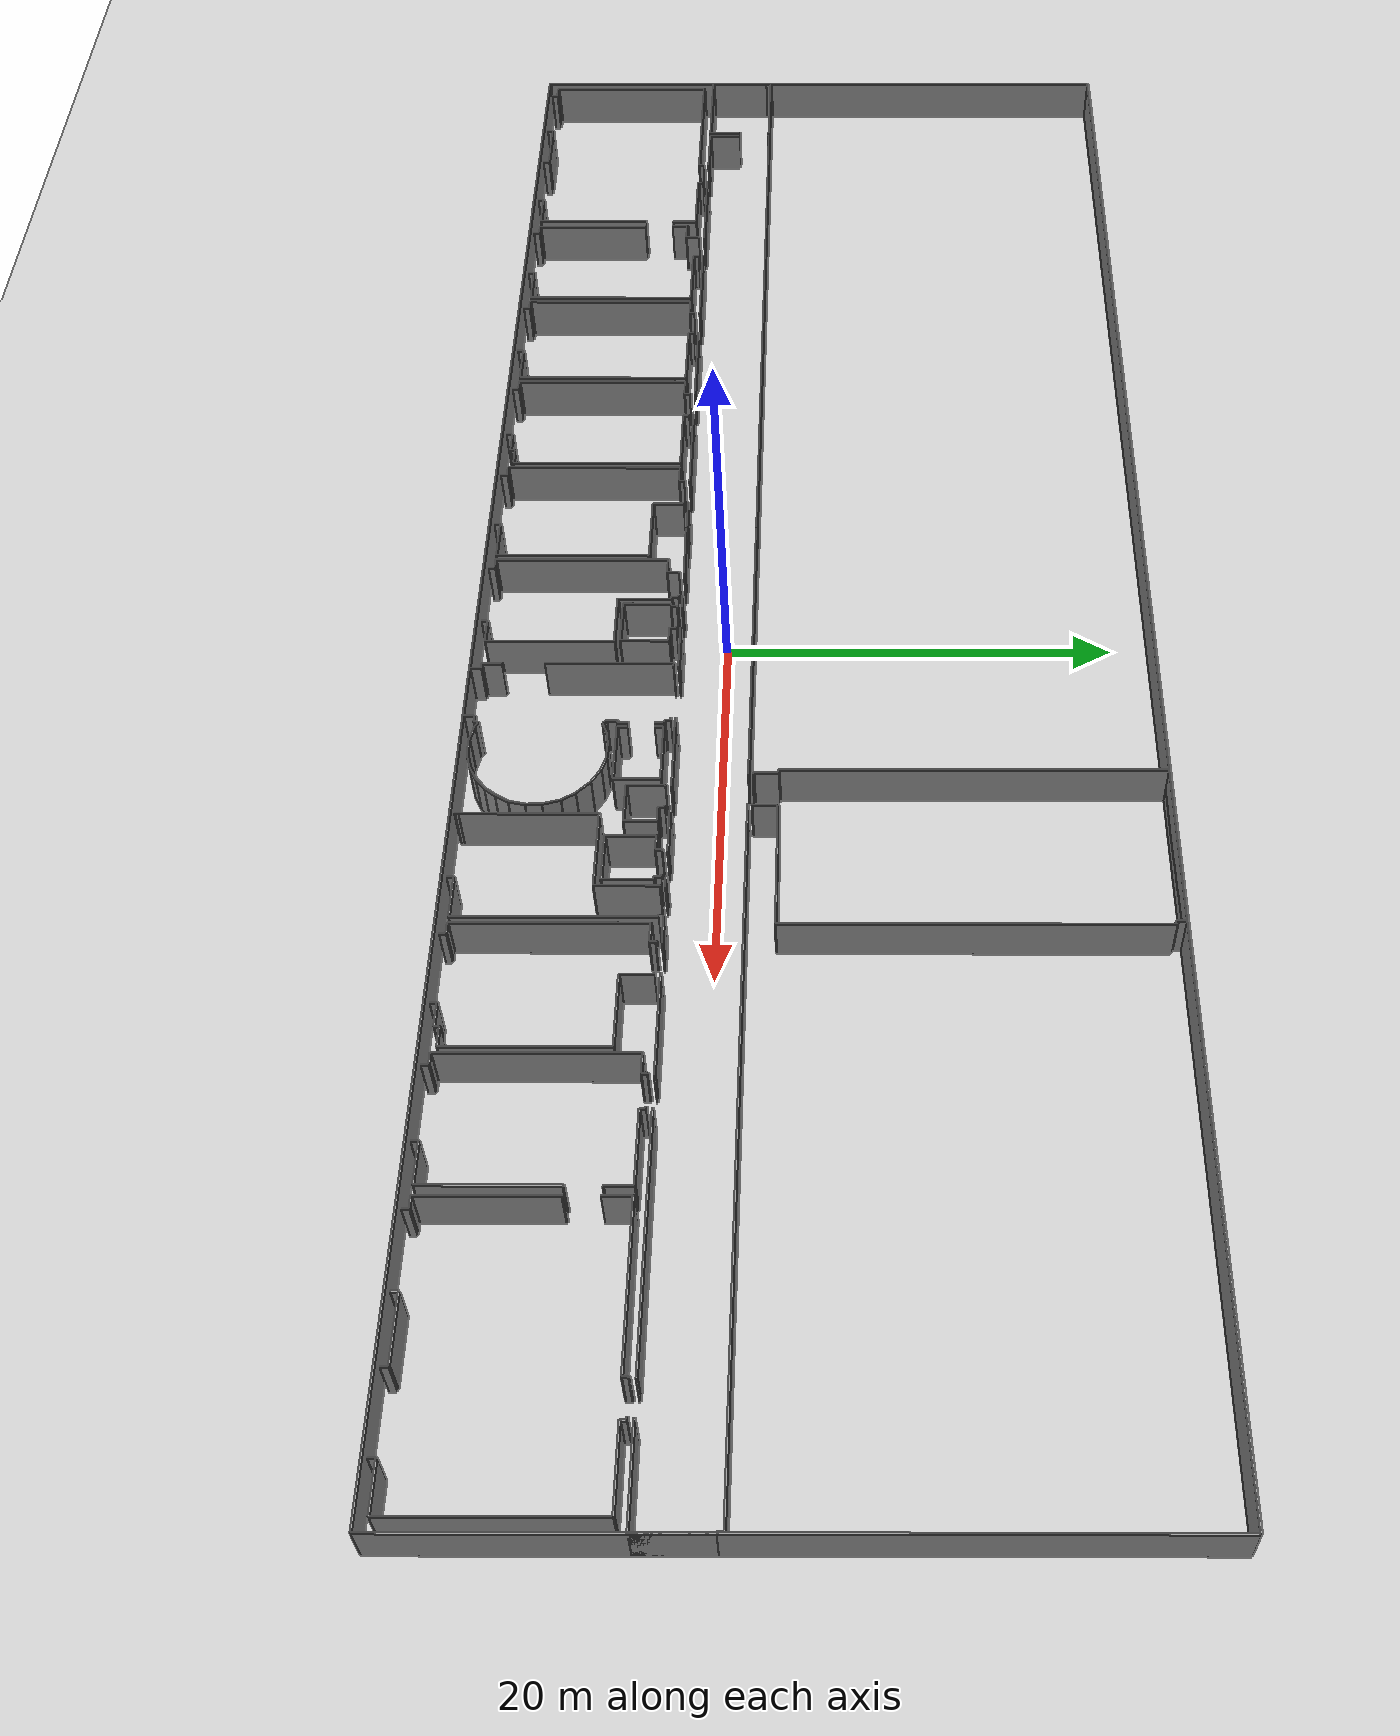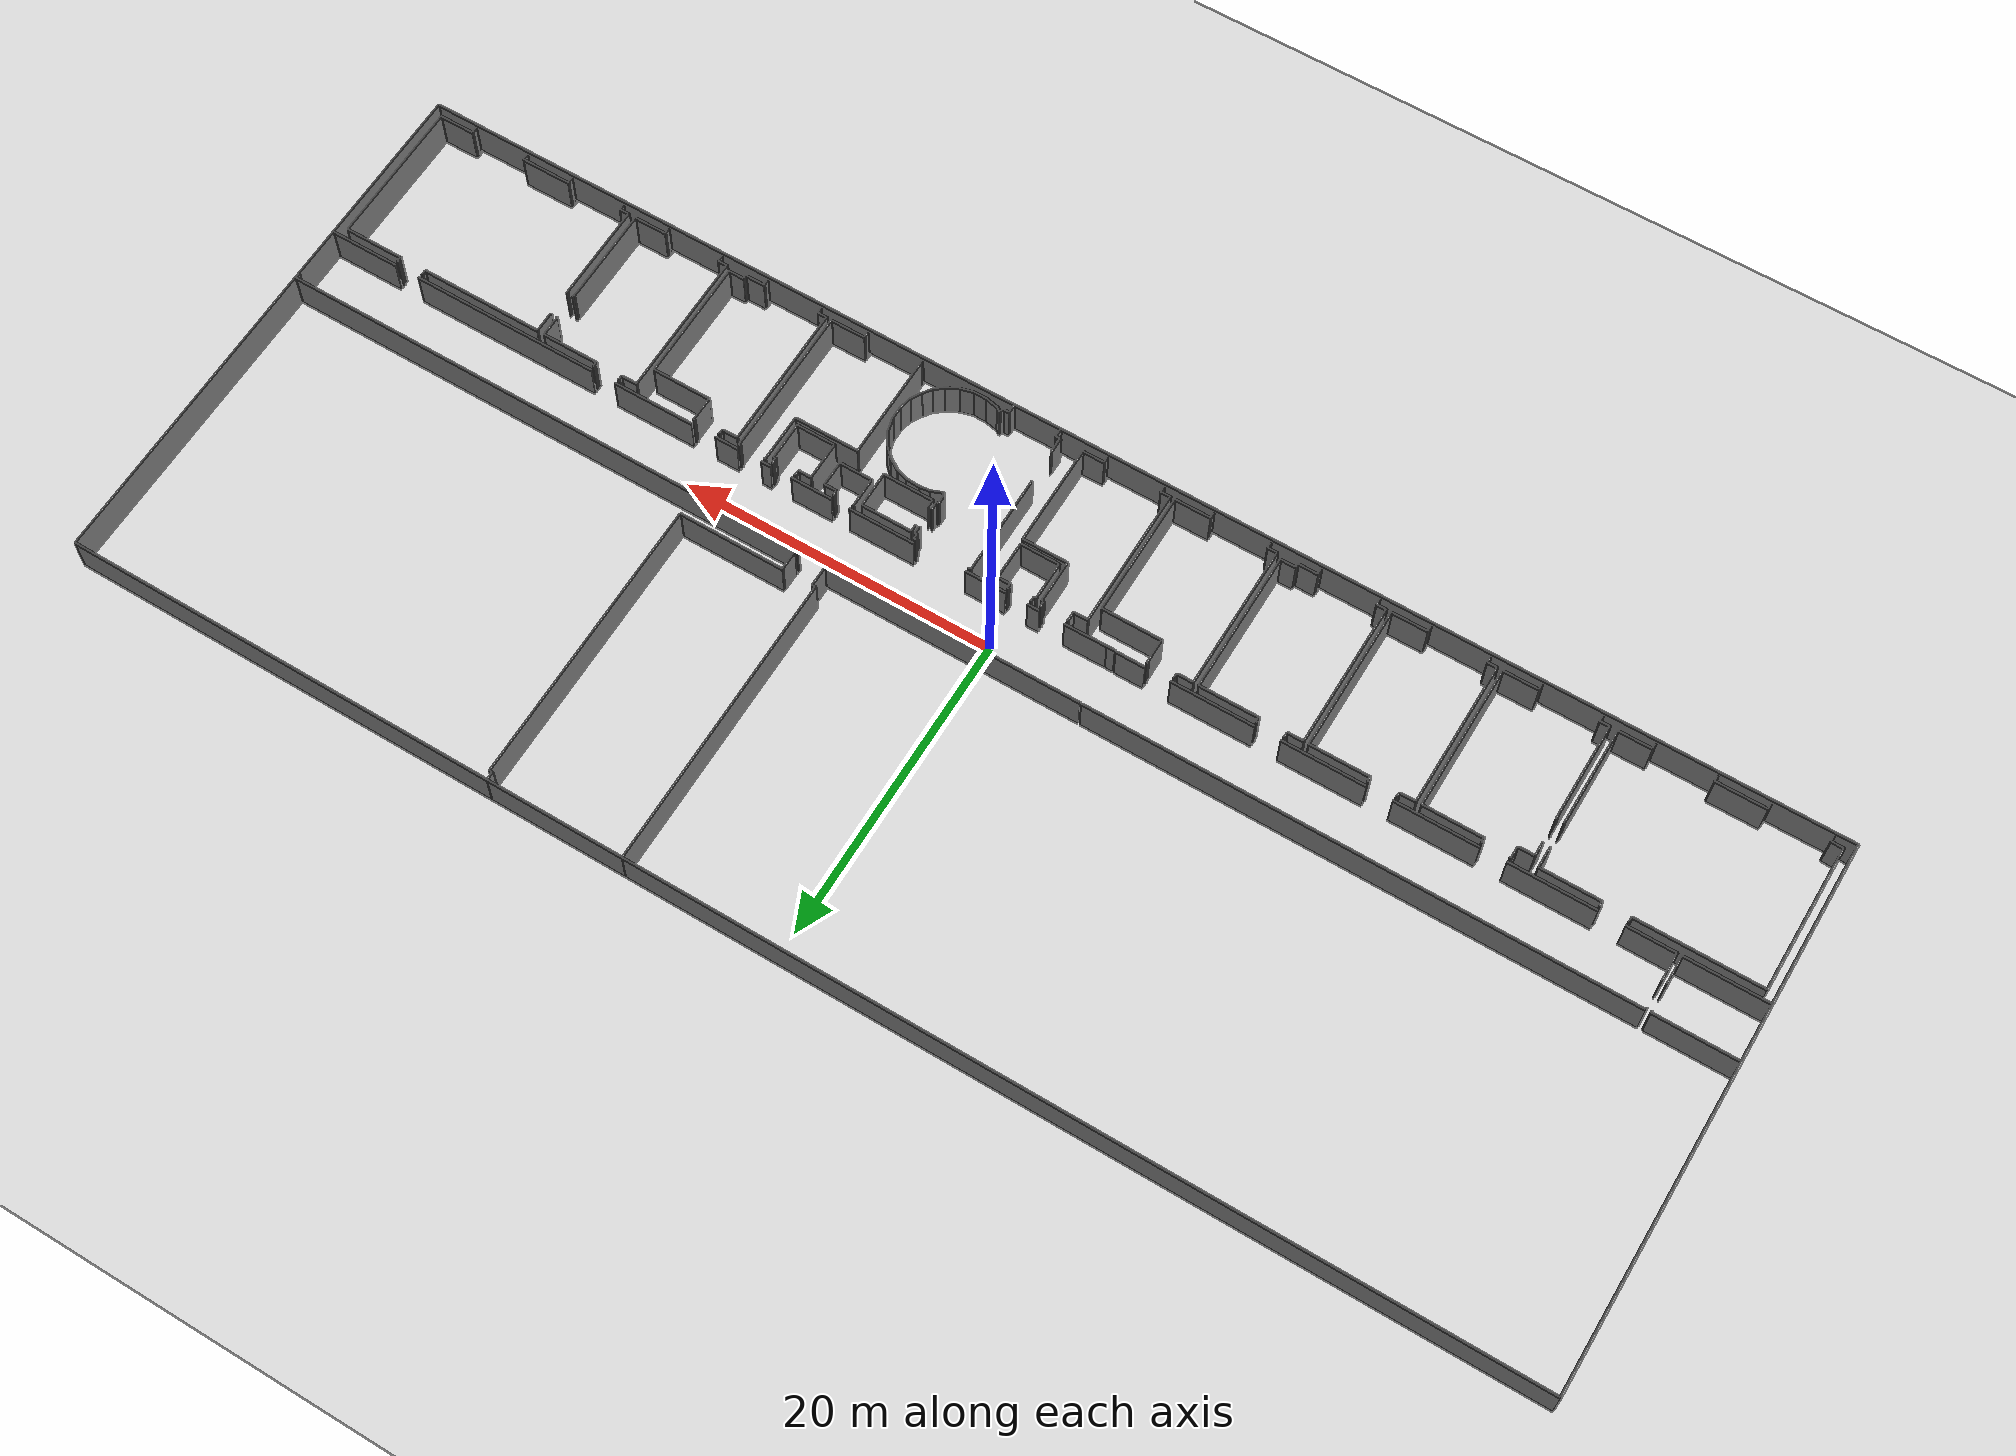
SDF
<sdf version="1.6">
  <world name="default">
    <light name="sun" type="directional">
      <cast_shadows>1</cast_shadows>
      <pose frame="">0 0 10 0 -0 0</pose>
      <diffuse>0.8 0.8 0.8 1</diffuse>
      <specular>0.1 0.1 0.1 1</specular>
      <attenuation>
        <range>1000</range>
        <constant>0.9</constant>
        <linear>0.01</linear>
        <quadratic>0.001</quadratic>
      </attenuation>
      <direction>-0.5 0.5 -1</direction>
    </light>
    <model name="ground_plane">
      <static>1</static>
      <link name="link">
        <collision name="collision">
          <geometry>
            <plane>
              <normal>0 0 1</normal>
              <size>100 100</size>
            </plane>
          </geometry>
          <surface>
            <friction>
              <ode>
                <mu>100</mu>
                <mu2>50</mu2>
              </ode>
              <torsional>
                <ode />
              </torsional>
            </friction>
            <contact>
              <ode />
            </contact>
            <bounce />
          </surface>
          <max_contacts>10</max_contacts>
        </collision>
        <visual name="visual">
          <cast_shadows>0</cast_shadows>
          <geometry>
            <plane>
              <normal>0 0 1</normal>
              <size>100 100</size>
            </plane>
          </geometry>
          <material>
            <script>
              <uri>file://media/materials/scripts/gazebo.material</uri>
              <name>Gazebo/Grey</name>
            </script>
          </material>
        </visual>
        <self_collide>0</self_collide>
        <kinematic>0</kinematic>
        <gravity>1</gravity>
      </link>
    </model>
    <gravity>0 0 -9.8</gravity>
    <magnetic_field>6e-06 2.3e-05 -4.2e-05</magnetic_field>
    <atmosphere type="adiabatic" />
    <physics default="0" name="default_physics" type="ode">
      <max_step_size>0.001</max_step_size>
      <real_time_factor>1</real_time_factor>
      <real_time_update_rate>1000</real_time_update_rate>
    </physics>
    <scene>
      <ambient>0.4 0.4 0.4 1</ambient>
      <background>0.7 0.7 0.7 1</background>
      <shadows>1</shadows>
    </scene>
    <spherical_coordinates>
      <surface_model>EARTH_WGS84</surface_model>
      <latitude_deg>0</latitude_deg>
      <longitude_deg>0</longitude_deg>
      <elevation>0</elevation>
      <heading_deg>0</heading_deg>
    </spherical_coordinates>
  <model name="50045369">
		<static>1</static>
		<link name="Wall_0">
			<collision name="Wall_0_Collision">
				<geometry>
					<box>
						<size>9.40878904388 0.1 2.5</size>
					</box>
				</geometry>
				<pose frame="">4.70439452194 0 1.25 0 0 0</pose>
			</collision>
			<visual name="Wall_0_Visual">
				<pose frame="">4.70439452194 0 1.25 0 0 0</pose>
				<geometry>
					<box>
						<size>9.40878904388 0.1 2.5</size>
					</box>
				</geometry>
				<material>
					<script>
						<uri>file://media/materials/scripts/gazebo.material</uri>
						<name>Gazebo/Grey</name>
					</script>
					<ambient>1 1 1 1</ambient>
				</material>
			</visual>
			<pose frame="">0.571955133297 -34.2055860951 0 0 0 1.57079632679</pose>
		</link>
		<link name="Wall_1">
			<collision name="Wall_1_Collision">
				<geometry>
					<box>
						<size>7.82269390868 0.1 2.5</size>
					</box>
				</geometry>
				<pose frame="">3.91134695434 0 1.25 0 0 0</pose>
			</collision>
			<visual name="Wall_1_Visual">
				<pose frame="">3.91134695434 0 1.25 0 0 0</pose>
				<geometry>
					<box>
						<size>7.82269390868 0.1 2.5</size>
					</box>
				</geometry>
				<material>
					<script>
						<uri>file://media/materials/scripts/gazebo.material</uri>
						<name>Gazebo/Grey</name>
					</script>
					<ambient>1 1 1 1</ambient>
				</material>
			</visual>
			<pose frame="">0.571955133297 -24.7967970513 0 0 0 0.0</pose>
		</link>
		<link name="Wall_2">
			<collision name="Wall_2_Collision">
				<geometry>
					<box>
						<size>0.289409297448 0.1 2.5</size>
					</box>
				</geometry>
				<pose frame="">0.144704648724 0 1.25 0 0 0</pose>
			</collision>
			<visual name="Wall_2_Visual">
				<pose frame="">0.144704648724 0 1.25 0 0 0</pose>
				<geometry>
					<box>
						<size>0.289409297448 0.1 2.5</size>
					</box>
				</geometry>
				<material>
					<script>
						<uri>file://media/materials/scripts/gazebo.material</uri>
						<name>Gazebo/Grey</name>
					</script>
					<ambient>1 1 1 1</ambient>
				</material>
			</visual>
			<pose frame="">8.39464904198 -24.7967970513 0 0 0 1.57079632679</pose>
		</link>
		<link name="Wall_3">
			<collision name="Wall_3_Collision">
				<geometry>
					<box>
						<size>0.0658383908996 0.1 2.5</size>
					</box>
				</geometry>
				<pose frame="">0.0329191954498 0 1.25 0 0 0</pose>
			</collision>
			<visual name="Wall_3_Visual">
				<pose frame="">0.0329191954498 0 1.25 0 0 0</pose>
				<geometry>
					<box>
						<size>0.0658383908996 0.1 2.5</size>
					</box>
				</geometry>
				<material>
					<script>
						<uri>file://media/materials/scripts/gazebo.material</uri>
						<name>Gazebo/Grey</name>
					</script>
					<ambient>1 1 1 1</ambient>
				</material>
			</visual>
			<pose frame="">8.39464904198 -24.5073877538 0 0 0 0.0</pose>
		</link>
		<link name="Wall_4">
			<collision name="Wall_4_Collision">
				<geometry>
					<box>
						<size>0.107781767341 0.1 2.5</size>
					</box>
				</geometry>
				<pose frame="">0.0538908836707 0 1.25 0 0 0</pose>
			</collision>
			<visual name="Wall_4_Visual">
				<pose frame="">0.0538908836707 0 1.25 0 0 0</pose>
				<geometry>
					<box>
						<size>0.107781767341 0.1 2.5</size>
					</box>
				</geometry>
				<material>
					<script>
						<uri>file://media/materials/scripts/gazebo.material</uri>
						<name>Gazebo/Grey</name>
					</script>
					<ambient>1 1 1 1</ambient>
				</material>
			</visual>
			<pose frame="">10.0209081377 -24.5073877538 0 0 0 0.0</pose>
		</link>
		<link name="Wall_5">
			<collision name="Wall_5_Collision">
				<geometry>
					<box>
						<size>0.286740173493 0.1 2.5</size>
					</box>
				</geometry>
				<pose frame="">0.143370086747 0 1.25 0 0 0</pose>
			</collision>
			<visual name="Wall_5_Visual">
				<pose frame="">0.143370086747 0 1.25 0 0 0</pose>
				<geometry>
					<box>
						<size>0.286740173493 0.1 2.5</size>
					</box>
				</geometry>
				<material>
					<script>
						<uri>file://media/materials/scripts/gazebo.material</uri>
						<name>Gazebo/Grey</name>
					</script>
					<ambient>1 1 1 1</ambient>
				</material>
			</visual>
			<pose frame="">10.128689905 -24.5073877538 0 0 0 -1.57079632679</pose>
		</link>
		<link name="Wall_6">
			<collision name="Wall_6_Collision">
				<geometry>
					<box>
						<size>3.74439960599 0.1 2.5</size>
					</box>
				</geometry>
				<pose frame="">1.87219980299 0 1.25 0 0 0</pose>
			</collision>
			<visual name="Wall_6_Visual">
				<pose frame="">1.87219980299 0 1.25 0 0 0</pose>
				<geometry>
					<box>
						<size>3.74439960599 0.1 2.5</size>
					</box>
				</geometry>
				<material>
					<script>
						<uri>file://media/materials/scripts/gazebo.material</uri>
						<name>Gazebo/Grey</name>
					</script>
					<ambient>1 1 1 1</ambient>
				</material>
			</visual>
			<pose frame="">10.128689905 -24.7941279273 0 0 0 0.0</pose>
		</link>
		<link name="Wall_7">
			<collision name="Wall_7_Collision">
				<geometry>
					<box>
						<size>1.38375011916 0.1 2.5</size>
					</box>
				</geometry>
				<pose frame="">0.691875059579 0 1.25 0 0 0</pose>
			</collision>
			<visual name="Wall_7_Visual">
				<pose frame="">0.691875059579 0 1.25 0 0 0</pose>
				<geometry>
					<box>
						<size>1.38375011916 0.1 2.5</size>
					</box>
				</geometry>
				<material>
					<script>
						<uri>file://media/materials/scripts/gazebo.material</uri>
						<name>Gazebo/Grey</name>
					</script>
					<ambient>1 1 1 1</ambient>
				</material>
			</visual>
			<pose frame="">13.873089511 -24.7941279273 0 0 0 -1.57079632679</pose>
		</link>
		<link name="Wall_8">
			<collision name="Wall_8_Collision">
				<geometry>
					<box>
						<size>6.41937021385 0.1 2.5</size>
					</box>
				</geometry>
				<pose frame="">3.20968510692 0 1.25 0 0 0</pose>
			</collision>
			<visual name="Wall_8_Visual">
				<pose frame="">3.20968510692 0 1.25 0 0 0</pose>
				<geometry>
					<box>
						<size>6.41937021385 0.1 2.5</size>
					</box>
				</geometry>
				<material>
					<script>
						<uri>file://media/materials/scripts/gazebo.material</uri>
						<name>Gazebo/Grey</name>
					</script>
					<ambient>1 1 1 1</ambient>
				</material>
			</visual>
			<pose frame="">13.873089511 -27.7717263512 0 0 0 -1.57079632679</pose>
		</link>
		<link name="Wall_9">
			<collision name="Wall_9_Collision">
				<geometry>
					<box>
						<size>2.07352800991 0.1 2.5</size>
					</box>
				</geometry>
				<pose frame="">1.03676400496 0 1.25 0 0 0</pose>
			</collision>
			<visual name="Wall_9_Visual">
				<pose frame="">1.03676400496 0 1.25 0 0 0</pose>
				<geometry>
					<box>
						<size>2.07352800991 0.1 2.5</size>
					</box>
				</geometry>
				<material>
					<script>
						<uri>file://media/materials/scripts/gazebo.material</uri>
						<name>Gazebo/Grey</name>
					</script>
					<ambient>1 1 1 1</ambient>
				</material>
			</visual>
			<pose frame="">13.873089511 -34.1910965651 0 0 0 3.14159265359</pose>
		</link>
		<link name="Wall_10">
			<collision name="Wall_10_Collision">
				<geometry>
					<box>
						<size>0.348765530171 0.1 2.5</size>
					</box>
				</geometry>
				<pose frame="">0.174382765085 0 1.25 0 0 0</pose>
			</collision>
			<visual name="Wall_10_Visual">
				<pose frame="">0.174382765085 0 1.25 0 0 0</pose>
				<geometry>
					<box>
						<size>0.348765530171 0.1 2.5</size>
					</box>
				</geometry>
				<material>
					<script>
						<uri>file://media/materials/scripts/gazebo.material</uri>
						<name>Gazebo/Grey</name>
					</script>
					<ambient>1 1 1 1</ambient>
				</material>
			</visual>
			<pose frame="">11.7995615011 -34.1910965651 0 0 0 -1.57079632679</pose>
		</link>
		<link name="Wall_11">
			<collision name="Wall_11_Collision">
				<geometry>
					<box>
						<size>0.347875822186 0.1 2.5</size>
					</box>
				</geometry>
				<pose frame="">0.173937911093 0 1.25 0 0 0</pose>
			</collision>
			<visual name="Wall_11_Visual">
				<pose frame="">0.173937911093 0 1.25 0 0 0</pose>
				<geometry>
					<box>
						<size>0.347875822186 0.1 2.5</size>
					</box>
				</geometry>
				<material>
					<script>
						<uri>file://media/materials/scripts/gazebo.material</uri>
						<name>Gazebo/Grey</name>
					</script>
					<ambient>1 1 1 1</ambient>
				</material>
			</visual>
			<pose frame="">8.11324711639 -34.5398620953 0 0 0 1.57079632679</pose>
		</link>
		<link name="Wall_12">
			<collision name="Wall_12_Collision">
				<geometry>
					<box>
						<size>3.14804105367 0.1 2.5</size>
					</box>
				</geometry>
				<pose frame="">1.57402052683 0 1.25 0 0 0</pose>
			</collision>
			<visual name="Wall_12_Visual">
				<pose frame="">1.57402052683 0 1.25 0 0 0</pose>
				<geometry>
					<box>
						<size>3.14804105367 0.1 2.5</size>
					</box>
				</geometry>
				<material>
					<script>
						<uri>file://media/materials/scripts/gazebo.material</uri>
						<name>Gazebo/Grey</name>
					</script>
					<ambient>1 1 1 1</ambient>
				</material>
			</visual>
			<pose frame="">8.11324711639 -34.1919862731 0 0 0 3.14159265359</pose>
		</link>
		<link name="Wall_13">
			<collision name="Wall_13_Collision">
				<geometry>
					<box>
						<size>0.344062787964 0.1 2.5</size>
					</box>
				</geometry>
				<pose frame="">0.172031393982 0 1.25 0 0 0</pose>
			</collision>
			<visual name="Wall_13_Visual">
				<pose frame="">0.172031393982 0 1.25 0 0 0</pose>
				<geometry>
					<box>
						<size>0.344062787964 0.1 2.5</size>
					</box>
				</geometry>
				<material>
					<script>
						<uri>file://media/materials/scripts/gazebo.material</uri>
						<name>Gazebo/Grey</name>
					</script>
					<ambient>1 1 1 1</ambient>
				</material>
			</visual>
			<pose frame="">4.96520606272 -34.1919862731 0 0 0 -1.57079632679</pose>
		</link>
		<link name="Wall_14">
			<collision name="Wall_14_Collision">
				<geometry>
					<box>
						<size>0.311016491373 0.1 2.5</size>
					</box>
				</geometry>
				<pose frame="">0.155508245687 0 1.25 0 0 0</pose>
			</collision>
			<visual name="Wall_14_Visual">
				<pose frame="">0.155508245687 0 1.25 0 0 0</pose>
				<geometry>
					<box>
						<size>0.311016491373 0.1 2.5</size>
					</box>
				</geometry>
				<material>
					<script>
						<uri>file://media/materials/scripts/gazebo.material</uri>
						<name>Gazebo/Grey</name>
					</script>
					<ambient>1 1 1 1</ambient>
				</material>
			</visual>
			<pose frame="">1.31142957008 -34.536049061 0 0 0 1.57079632679</pose>
		</link>
		<link name="Wall_15">
			<collision name="Wall_15_Collision">
				<geometry>
					<box>
						<size>0.739730091336 0.1 2.5</size>
					</box>
				</geometry>
				<pose frame="">0.369865045668 0 1.25 0 0 0</pose>
			</collision>
			<visual name="Wall_15_Visual">
				<pose frame="">0.369865045668 0 1.25 0 0 0</pose>
				<geometry>
					<box>
						<size>0.739730091336 0.1 2.5</size>
					</box>
				</geometry>
				<material>
					<script>
						<uri>file://media/materials/scripts/gazebo.material</uri>
						<name>Gazebo/Grey</name>
					</script>
					<ambient>1 1 1 1</ambient>
				</material>
			</visual>
			<pose frame="">1.31142957008 -34.2250325697 0 0 0 3.1153010165</pose>
		</link>
		<link name="Wall_16">
			<collision name="Wall_16_Collision">
				<geometry>
					<box>
						<size>6.36026818341 0.1 2.5</size>
					</box>
				</geometry>
				<pose frame="">3.1801340917 0 1.25 0 0 0</pose>
			</collision>
			<visual name="Wall_16_Visual">
				<pose frame="">3.1801340917 0 1.25 0 0 0</pose>
				<geometry>
					<box>
						<size>6.36026818341 0.1 2.5</size>
					</box>
				</geometry>
				<material>
					<script>
						<uri>file://media/materials/scripts/gazebo.material</uri>
						<name>Gazebo/Grey</name>
					</script>
					<ambient>1 1 1 1</ambient>
				</material>
			</visual>
			<pose frame="">14.3629373074 -34.204569286 0 0 0 1.57079632679</pose>
		</link>
		<link name="Wall_17">
			<collision name="Wall_17_Collision">
				<geometry>
					<box>
						<size>0.0283435543834 0.1 2.5</size>
					</box>
				</geometry>
				<pose frame="">0.0141717771917 0 1.25 0 0 0</pose>
			</collision>
			<visual name="Wall_17_Visual">
				<pose frame="">0.0141717771917 0 1.25 0 0 0</pose>
				<geometry>
					<box>
						<size>0.0283435543834 0.1 2.5</size>
					</box>
				</geometry>
				<material>
					<script>
						<uri>file://media/materials/scripts/gazebo.material</uri>
						<name>Gazebo/Grey</name>
					</script>
					<ambient>1 1 1 1</ambient>
				</material>
			</visual>
			<pose frame="">14.3629373074 -27.8443011026 0 0 0 3.14159265359</pose>
		</link>
		<link name="Wall_18">
			<collision name="Wall_18_Collision">
				<geometry>
					<box>
						<size>0.0683804137142 0.1 2.5</size>
					</box>
				</geometry>
				<pose frame="">0.0341902068571 0 1.25 0 0 0</pose>
			</collision>
			<visual name="Wall_18_Visual">
				<pose frame="">0.0341902068571 0 1.25 0 0 0</pose>
				<geometry>
					<box>
						<size>0.0683804137142 0.1 2.5</size>
					</box>
				</geometry>
				<material>
					<script>
						<uri>file://media/materials/scripts/gazebo.material</uri>
						<name>Gazebo/Grey</name>
					</script>
					<ambient>1 1 1 1</ambient>
				</material>
			</visual>
			<pose frame="">14.334593753 -27.8443011026 0 0 0 1.57079632679</pose>
		</link>
		<link name="Wall_19">
			<collision name="Wall_19_Collision">
				<geometry>
					<box>
						<size>0.901909694639 0.1 2.5</size>
					</box>
				</geometry>
				<pose frame="">0.45095484732 0 1.25 0 0 0</pose>
			</collision>
			<visual name="Wall_19_Visual">
				<pose frame="">0.45095484732 0 1.25 0 0 0</pose>
				<geometry>
					<box>
						<size>0.901909694639 0.1 2.5</size>
					</box>
				</geometry>
				<material>
					<script>
						<uri>file://media/materials/scripts/gazebo.material</uri>
						<name>Gazebo/Grey</name>
					</script>
					<ambient>1 1 1 1</ambient>
				</material>
			</visual>
			<pose frame="">14.334593753 -26.1941469925 0 0 0 1.57079632679</pose>
		</link>
		<link name="Wall_20">
			<collision name="Wall_20_Collision">
				<geometry>
					<box>
						<size>1.0197324521 0.1 2.5</size>
					</box>
				</geometry>
				<pose frame="">0.509866226049 0 1.25 0 0 0</pose>
			</collision>
			<visual name="Wall_20_Visual">
				<pose frame="">0.509866226049 0 1.25 0 0 0</pose>
				<geometry>
					<box>
						<size>1.0197324521 0.1 2.5</size>
					</box>
				</geometry>
				<material>
					<script>
						<uri>file://media/materials/scripts/gazebo.material</uri>
						<name>Gazebo/Grey</name>
					</script>
					<ambient>1 1 1 1</ambient>
				</material>
			</visual>
			<pose frame="">14.334593753 -25.2922372978 0 0 0 0.0</pose>
		</link>
		<link name="Wall_21">
			<collision name="Wall_21_Collision">
				<geometry>
					<box>
						<size>0.78052810524 0.1 2.5</size>
					</box>
				</geometry>
				<pose frame="">0.39026405262 0 1.25 0 0 0</pose>
			</collision>
			<visual name="Wall_21_Visual">
				<pose frame="">0.39026405262 0 1.25 0 0 0</pose>
				<geometry>
					<box>
						<size>0.78052810524 0.1 2.5</size>
					</box>
				</geometry>
				<material>
					<script>
						<uri>file://media/materials/scripts/gazebo.material</uri>
						<name>Gazebo/Grey</name>
					</script>
					<ambient>1 1 1 1</ambient>
				</material>
			</visual>
			<pose frame="">15.3543262051 -25.2922372978 0 0 0 1.57079632679</pose>
		</link>
		<link name="Wall_22">
			<collision name="Wall_22_Collision">
				<geometry>
					<box>
						<size>0.0939277430015 0.1 2.5</size>
					</box>
				</geometry>
				<pose frame="">0.0469638715007 0 1.25 0 0 0</pose>
			</collision>
			<visual name="Wall_22_Visual">
				<pose frame="">0.0469638715007 0 1.25 0 0 0</pose>
				<geometry>
					<box>
						<size>0.0939277430015 0.1 2.5</size>
					</box>
				</geometry>
				<material>
					<script>
						<uri>file://media/materials/scripts/gazebo.material</uri>
						<name>Gazebo/Grey</name>
					</script>
					<ambient>1 1 1 1</ambient>
				</material>
			</visual>
			<pose frame="">15.3543262051 -24.5117091926 0 0 0 0.0</pose>
		</link>
		<link name="Wall_23">
			<collision name="Wall_23_Collision">
				<geometry>
					<box>
						<size>0.104477137682 0.1 2.5</size>
					</box>
				</geometry>
				<pose frame="">0.0522385688412 0 1.25 0 0 0</pose>
			</collision>
			<visual name="Wall_23_Visual">
				<pose frame="">0.0522385688412 0 1.25 0 0 0</pose>
				<geometry>
					<box>
						<size>0.104477137682 0.1 2.5</size>
					</box>
				</geometry>
				<material>
					<script>
						<uri>file://media/materials/scripts/gazebo.material</uri>
						<name>Gazebo/Grey</name>
					</script>
					<ambient>1 1 1 1</ambient>
				</material>
			</visual>
			<pose frame="">17.0051158209 -24.5117091926 0 0 0 0.0</pose>
		</link>
		<link name="Wall_24">
			<collision name="Wall_24_Collision">
				<geometry>
					<box>
						<size>0.292459724826 0.1 2.5</size>
					</box>
				</geometry>
				<pose frame="">0.146229862413 0 1.25 0 0 0</pose>
			</collision>
			<visual name="Wall_24_Visual">
				<pose frame="">0.146229862413 0 1.25 0 0 0</pose>
				<geometry>
					<box>
						<size>0.292459724826 0.1 2.5</size>
					</box>
				</geometry>
				<material>
					<script>
						<uri>file://media/materials/scripts/gazebo.material</uri>
						<name>Gazebo/Grey</name>
					</script>
					<ambient>1 1 1 1</ambient>
				</material>
			</visual>
			<pose frame="">17.1095929586 -24.5117091926 0 0 0 -1.57079632679</pose>
		</link>
		<link name="Wall_25">
			<collision name="Wall_25_Collision">
				<geometry>
					<box>
						<size>3.73105398621 0.1 2.5</size>
					</box>
				</geometry>
				<pose frame="">1.8655269931 0 1.25 0 0 0</pose>
			</collision>
			<visual name="Wall_25_Visual">
				<pose frame="">1.8655269931 0 1.25 0 0 0</pose>
				<geometry>
					<box>
						<size>3.73105398621 0.1 2.5</size>
					</box>
				</geometry>
				<material>
					<script>
						<uri>file://media/materials/scripts/gazebo.material</uri>
						<name>Gazebo/Grey</name>
					</script>
					<ambient>1 1 1 1</ambient>
				</material>
			</visual>
			<pose frame="">17.1095929586 -24.8041689174 0 0 0 0.0</pose>
		</link>
		<link name="Wall_26">
			<collision name="Wall_26_Collision">
				<geometry>
					<box>
						<size>9.38540243399 0.1 2.5</size>
					</box>
				</geometry>
				<pose frame="">4.69270121699 0 1.25 0 0 0</pose>
			</collision>
			<visual name="Wall_26_Visual">
				<pose frame="">4.69270121699 0 1.25 0 0 0</pose>
				<geometry>
					<box>
						<size>9.38540243399 0.1 2.5</size>
					</box>
				</geometry>
				<material>
					<script>
						<uri>file://media/materials/scripts/gazebo.material</uri>
						<name>Gazebo/Grey</name>
					</script>
					<ambient>1 1 1 1</ambient>
				</material>
			</visual>
			<pose frame="">20.8406469448 -24.8041689174 0 0 0 -1.57079632679</pose>
		</link>
		<link name="Wall_27">
			<collision name="Wall_27_Collision">
				<geometry>
					<box>
						<size>2.21448317499 0.1 2.5</size>
					</box>
				</geometry>
				<pose frame="">1.10724158749 0 1.25 0 0 0</pose>
			</collision>
			<visual name="Wall_27_Visual">
				<pose frame="">1.10724158749 0 1.25 0 0 0</pose>
				<geometry>
					<box>
						<size>2.21448317499 0.1 2.5</size>
					</box>
				</geometry>
				<material>
					<script>
						<uri>file://media/materials/scripts/gazebo.material</uri>
						<name>Gazebo/Grey</name>
					</script>
					<ambient>1 1 1 1</ambient>
				</material>
			</visual>
			<pose frame="">20.8406469448 -34.1895713514 0 0 0 3.14159265359</pose>
		</link>
		<link name="Wall_28">
			<collision name="Wall_28_Collision">
				<geometry>
					<box>
						<size>0.351561755267 0.1 2.5</size>
					</box>
				</geometry>
				<pose frame="">0.175780877633 0 1.25 0 0 0</pose>
			</collision>
			<visual name="Wall_28_Visual">
				<pose frame="">0.175780877633 0 1.25 0 0 0</pose>
				<geometry>
					<box>
						<size>0.351561755267 0.1 2.5</size>
					</box>
				</geometry>
				<material>
					<script>
						<uri>file://media/materials/scripts/gazebo.material</uri>
						<name>Gazebo/Grey</name>
					</script>
					<ambient>1 1 1 1</ambient>
				</material>
			</visual>
			<pose frame="">18.6261637698 -34.1895713514 0 0 0 -1.57079632679</pose>
		</link>
		<link name="Wall_29">
			<collision name="Wall_29_Collision">
				<geometry>
					<box>
						<size>0.340631057164 0.1 2.5</size>
					</box>
				</geometry>
				<pose frame="">0.170315528582 0 1.25 0 0 0</pose>
			</collision>
			<visual name="Wall_29_Visual">
				<pose frame="">0.170315528582 0 1.25 0 0 0</pose>
				<geometry>
					<box>
						<size>0.340631057164 0.1 2.5</size>
					</box>
				</geometry>
				<material>
					<script>
						<uri>file://media/materials/scripts/gazebo.material</uri>
						<name>Gazebo/Grey</name>
					</script>
					<ambient>1 1 1 1</ambient>
				</material>
			</visual>
			<pose frame="">14.9556099266 -34.5411331067 0 0 0 1.57079632679</pose>
		</link>
		<link name="Wall_30">
			<collision name="Wall_30_Collision">
				<geometry>
					<box>
						<size>0.592686574849 0.1 2.5</size>
					</box>
				</geometry>
				<pose frame="">0.296343287424 0 1.25 0 0 0</pose>
			</collision>
			<visual name="Wall_30_Visual">
				<pose frame="">0.296343287424 0 1.25 0 0 0</pose>
				<geometry>
					<box>
						<size>0.592686574849 0.1 2.5</size>
					</box>
				</geometry>
				<material>
					<script>
						<uri>file://media/materials/scripts/gazebo.material</uri>
						<name>Gazebo/Grey</name>
					</script>
					<ambient>1 1 1 1</ambient>
				</material>
			</visual>
			<pose frame="">14.9556099266 -34.2005020495 0 0 0 -3.13473022647</pose>
		</link>
		<link name="Wall_31">
			<collision name="Wall_31_Collision">
				<geometry>
					<box>
						<size>9.40357789711 0.1 2.5</size>
					</box>
				</geometry>
				<pose frame="">4.70178894856 0 1.25 0 0 0</pose>
			</collision>
			<visual name="Wall_31_Visual">
				<pose frame="">4.70178894856 0 1.25 0 0 0</pose>
				<geometry>
					<box>
						<size>9.40357789711 0.1 2.5</size>
					</box>
				</geometry>
				<material>
					<script>
						<uri>file://media/materials/scripts/gazebo.material</uri>
						<name>Gazebo/Grey</name>
					</script>
					<ambient>1 1 1 1</ambient>
				</material>
			</visual>
			<pose frame="">21.1886498681 -34.1983413301 0 0 0 1.57079632679</pose>
		</link>
		<link name="Wall_32">
			<collision name="Wall_32_Collision">
				<geometry>
					<box>
						<size>0.99558323536 0.1 2.5</size>
					</box>
				</geometry>
				<pose frame="">0.49779161768 0 1.25 0 0 0</pose>
			</collision>
			<visual name="Wall_32_Visual">
				<pose frame="">0.49779161768 0 1.25 0 0 0</pose>
				<geometry>
					<box>
						<size>0.99558323536 0.1 2.5</size>
					</box>
				</geometry>
				<material>
					<script>
						<uri>file://media/materials/scripts/gazebo.material</uri>
						<name>Gazebo/Grey</name>
					</script>
					<ambient>1 1 1 1</ambient>
				</material>
			</visual>
			<pose frame="">21.1886498681 -24.794763433 0 0 0 0.0</pose>
		</link>
		<link name="Wall_33">
			<collision name="Wall_33_Collision">
				<geometry>
					<box>
						<size>0.283435543834 0.1 2.5</size>
					</box>
				</geometry>
				<pose frame="">0.141717771917 0 1.25 0 0 0</pose>
			</collision>
			<visual name="Wall_33_Visual">
				<pose frame="">0.141717771917 0 1.25 0 0 0</pose>
				<geometry>
					<box>
						<size>0.283435543834 0.1 2.5</size>
					</box>
				</geometry>
				<material>
					<script>
						<uri>file://media/materials/scripts/gazebo.material</uri>
						<name>Gazebo/Grey</name>
					</script>
					<ambient>1 1 1 1</ambient>
				</material>
			</visual>
			<pose frame="">22.1842331035 -24.794763433 0 0 0 1.57079632679</pose>
		</link>
		<link name="Wall_34">
			<collision name="Wall_34_Collision">
				<geometry>
					<box>
						<size>0.0798195163802 0.1 2.5</size>
					</box>
				</geometry>
				<pose frame="">0.0399097581901 0 1.25 0 0 0</pose>
			</collision>
			<visual name="Wall_34_Visual">
				<pose frame="">0.0399097581901 0 1.25 0 0 0</pose>
				<geometry>
					<box>
						<size>0.0798195163802 0.1 2.5</size>
					</box>
				</geometry>
				<material>
					<script>
						<uri>file://media/materials/scripts/gazebo.material</uri>
						<name>Gazebo/Grey</name>
					</script>
					<ambient>1 1 1 1</ambient>
				</material>
			</visual>
			<pose frame="">22.1842331035 -24.5113278892 0 0 0 0.0</pose>
		</link>
		<link name="Wall_35">
			<collision name="Wall_35_Collision">
				<geometry>
					<box>
						<size>0.115407835785 0.1 2.5</size>
					</box>
				</geometry>
				<pose frame="">0.0577039178927 0 1.25 0 0 0</pose>
			</collision>
			<visual name="Wall_35_Visual">
				<pose frame="">0.0577039178927 0 1.25 0 0 0</pose>
				<geometry>
					<box>
						<size>0.115407835785 0.1 2.5</size>
					</box>
				</geometry>
				<material>
					<script>
						<uri>file://media/materials/scripts/gazebo.material</uri>
						<name>Gazebo/Grey</name>
					</script>
					<ambient>1 1 1 1</ambient>
				</material>
			</visual>
			<pose frame="">23.8354040228 -24.5113278892 0 0 0 0.0</pose>
		</link>
		<link name="Wall_36">
			<collision name="Wall_36_Collision">
				<geometry>
					<box>
						<size>0.287375679197 0.1 2.5</size>
					</box>
				</geometry>
				<pose frame="">0.143687839598 0 1.25 0 0 0</pose>
			</collision>
			<visual name="Wall_36_Visual">
				<pose frame="">0.143687839598 0 1.25 0 0 0</pose>
				<geometry>
					<box>
						<size>0.287375679197 0.1 2.5</size>
					</box>
				</geometry>
				<material>
					<script>
						<uri>file://media/materials/scripts/gazebo.material</uri>
						<name>Gazebo/Grey</name>
					</script>
					<ambient>1 1 1 1</ambient>
				</material>
			</visual>
			<pose frame="">23.9508118585 -24.5113278892 0 0 0 -1.57079632679</pose>
		</link>
		<link name="Wall_37">
			<collision name="Wall_37_Collision">
				<geometry>
					<box>
						<size>3.73448571701 0.1 2.5</size>
					</box>
				</geometry>
				<pose frame="">1.8672428585 0 1.25 0 0 0</pose>
			</collision>
			<visual name="Wall_37_Visual">
				<pose frame="">1.8672428585 0 1.25 0 0 0</pose>
				<geometry>
					<box>
						<size>3.73448571701 0.1 2.5</size>
					</box>
				</geometry>
				<material>
					<script>
						<uri>file://media/materials/scripts/gazebo.material</uri>
						<name>Gazebo/Grey</name>
					</script>
					<ambient>1 1 1 1</ambient>
				</material>
			</visual>
			<pose frame="">23.9508118585 -24.7987035684 0 0 0 0.0</pose>
		</link>
		<link name="Wall_38">
			<collision name="Wall_38_Collision">
				<geometry>
					<box>
						<size>9.40179848114 0.1 2.5</size>
					</box>
				</geometry>
				<pose frame="">4.70089924057 0 1.25 0 0 0</pose>
			</collision>
			<visual name="Wall_38_Visual">
				<pose frame="">4.70089924057 0 1.25 0 0 0</pose>
				<geometry>
					<box>
						<size>9.40179848114 0.1 2.5</size>
					</box>
				</geometry>
				<material>
					<script>
						<uri>file://media/materials/scripts/gazebo.material</uri>
						<name>Gazebo/Grey</name>
					</script>
					<ambient>1 1 1 1</ambient>
				</material>
			</visual>
			<pose frame="">27.6852975755 -24.7987035684 0 0 0 -1.57079632679</pose>
		</link>
		<link name="Wall_39">
			<collision name="Wall_39_Collision">
				<geometry>
					<box>
						<size>2.25096120238 0.1 2.5</size>
					</box>
				</geometry>
				<pose frame="">1.12548060119 0 1.25 0 0 0</pose>
			</collision>
			<visual name="Wall_39_Visual">
				<pose frame="">1.12548060119 0 1.25 0 0 0</pose>
				<geometry>
					<box>
						<size>2.25096120238 0.1 2.5</size>
					</box>
				</geometry>
				<material>
					<script>
						<uri>file://media/materials/scripts/gazebo.material</uri>
						<name>Gazebo/Grey</name>
					</script>
					<ambient>1 1 1 1</ambient>
				</material>
			</visual>
			<pose frame="">27.6852975755 -34.2005020495 0 0 0 3.14159265359</pose>
		</link>
		<link name="Wall_40">
			<collision name="Wall_40_Collision">
				<geometry>
					<box>
						<size>0.335165708112 0.1 2.5</size>
					</box>
				</geometry>
				<pose frame="">0.167582854056 0 1.25 0 0 0</pose>
			</collision>
			<visual name="Wall_40_Visual">
				<pose frame="">0.167582854056 0 1.25 0 0 0</pose>
				<geometry>
					<box>
						<size>0.335165708112 0.1 2.5</size>
					</box>
				</geometry>
				<material>
					<script>
						<uri>file://media/materials/scripts/gazebo.material</uri>
						<name>Gazebo/Grey</name>
					</script>
					<ambient>1 1 1 1</ambient>
				</material>
			</visual>
			<pose frame="">25.4343363732 -34.2005020495 0 0 0 -1.57079632679</pose>
		</link>
		<link name="Wall_41">
			<collision name="Wall_41_Collision">
				<geometry>
					<box>
						<size>0.341012360586 0.1 2.5</size>
					</box>
				</geometry>
				<pose frame="">0.170506180293 0 1.25 0 0 0</pose>
			</collision>
			<visual name="Wall_41_Visual">
				<pose frame="">0.170506180293 0 1.25 0 0 0</pose>
				<geometry>
					<box>
						<size>0.341012360586 0.1 2.5</size>
					</box>
				</geometry>
				<material>
					<script>
						<uri>file://media/materials/scripts/gazebo.material</uri>
						<name>Gazebo/Grey</name>
					</script>
					<ambient>1 1 1 1</ambient>
				</material>
			</visual>
			<pose frame="">21.7772552509 -34.5356677576 0 0 0 1.57079632679</pose>
		</link>
		<link name="Wall_42">
			<collision name="Wall_42_Collision">
				<geometry>
					<box>
						<size>0.588616923546 0.1 2.5</size>
					</box>
				</geometry>
				<pose frame="">0.294308461773 0 1.25 0 0 0</pose>
			</collision>
			<visual name="Wall_42_Visual">
				<pose frame="">0.294308461773 0 1.25 0 0 0</pose>
				<geometry>
					<box>
						<size>0.588616923546 0.1 2.5</size>
					</box>
				</geometry>
				<material>
					<script>
						<uri>file://media/materials/scripts/gazebo.material</uri>
						<name>Gazebo/Grey</name>
					</script>
					<ambient>1 1 1 1</ambient>
				</material>
			</visual>
			<pose frame="">21.7772552509 -34.194655397 0 0 0 -3.13533058904</pose>
		</link>
		<link name="Wall_43">
			<collision name="Wall_43_Collision">
				<geometry>
					<box>
						<size>9.40688252677 0.1 2.5</size>
					</box>
				</geometry>
				<pose frame="">4.70344126339 0 1.25 0 0 0</pose>
			</collision>
			<visual name="Wall_43_Visual">
				<pose frame="">4.70344126339 0 1.25 0 0 0</pose>
				<geometry>
					<box>
						<size>9.40688252677 0.1 2.5</size>
					</box>
				</geometry>
				<material>
					<script>
						<uri>file://media/materials/scripts/gazebo.material</uri>
						<name>Gazebo/Grey</name>
					</script>
					<ambient>1 1 1 1</ambient>
				</material>
			</visual>
			<pose frame="">28.0123288107 -34.2055860951 0 0 0 1.57079632679</pose>
		</link>
		<link name="Wall_44">
			<collision name="Wall_44_Collision">
				<geometry>
					<box>
						<size>1.00473451749 0.1 2.5</size>
					</box>
				</geometry>
				<pose frame="">0.502367258746 0 1.25 0 0 0</pose>
			</collision>
			<visual name="Wall_44_Visual">
				<pose frame="">0.502367258746 0 1.25 0 0 0</pose>
				<geometry>
					<box>
						<size>1.00473451749 0.1 2.5</size>
					</box>
				</geometry>
				<material>
					<script>
						<uri>file://media/materials/scripts/gazebo.material</uri>
						<name>Gazebo/Grey</name>
					</script>
					<ambient>1 1 1 1</ambient>
				</material>
			</visual>
			<pose frame="">28.0123288107 -24.7987035684 0 0 0 0.0</pose>
		</link>
		<link name="Wall_45">
			<collision name="Wall_45_Collision">
				<geometry>
					<box>
						<size>0.307711861714 0.1 2.5</size>
					</box>
				</geometry>
				<pose frame="">0.153855930857 0 1.25 0 0 0</pose>
			</collision>
			<visual name="Wall_45_Visual">
				<pose frame="">0.153855930857 0 1.25 0 0 0</pose>
				<geometry>
					<box>
						<size>0.307711861714 0.1 2.5</size>
					</box>
				</geometry>
				<material>
					<script>
						<uri>file://media/materials/scripts/gazebo.material</uri>
						<name>Gazebo/Grey</name>
					</script>
					<ambient>1 1 1 1</ambient>
				</material>
			</visual>
			<pose frame="">29.0170633281 -24.7987035684 0 0 0 1.57079632679</pose>
		</link>
		<link name="Wall_46">
			<collision name="Wall_46_Collision">
				<geometry>
					<box>
						<size>0.0824886403355 0.1 2.5</size>
					</box>
				</geometry>
				<pose frame="">0.0412443201678 0 1.25 0 0 0</pose>
			</collision>
			<visual name="Wall_46_Visual">
				<pose frame="">0.0412443201678 0 1.25 0 0 0</pose>
				<geometry>
					<box>
						<size>0.0824886403355 0.1 2.5</size>
					</box>
				</geometry>
				<material>
					<script>
						<uri>file://media/materials/scripts/gazebo.material</uri>
						<name>Gazebo/Grey</name>
					</script>
					<ambient>1 1 1 1</ambient>
				</material>
			</visual>
			<pose frame="">29.0170633281 -24.4909917067 0 0 0 0.0</pose>
		</link>
		<link name="Wall_47">
			<collision name="Wall_47_Collision">
				<geometry>
					<box>
						<size>0.101680912586 0.1 2.5</size>
					</box>
				</geometry>
				<pose frame="">0.0508404562931 0 1.25 0 0 0</pose>
			</collision>
			<visual name="Wall_47_Visual">
				<pose frame="">0.0508404562931 0 1.25 0 0 0</pose>
				<geometry>
					<box>
						<size>0.101680912586 0.1 2.5</size>
					</box>
				</geometry>
				<material>
					<script>
						<uri>file://media/materials/scripts/gazebo.material</uri>
						<name>Gazebo/Grey</name>
					</script>
					<ambient>1 1 1 1</ambient>
				</material>
			</visual>
			<pose frame="">30.6575577516 -24.4909917067 0 0 0 0.0</pose>
		</link>
		<link name="Wall_48">
			<collision name="Wall_48_Collision">
				<geometry>
					<box>
						<size>0.295383051063 0.1 2.5</size>
					</box>
				</geometry>
				<pose frame="">0.147691525531 0 1.25 0 0 0</pose>
			</collision>
			<visual name="Wall_48_Visual">
				<pose frame="">0.147691525531 0 1.25 0 0 0</pose>
				<geometry>
					<box>
						<size>0.295383051063 0.1 2.5</size>
					</box>
				</geometry>
				<material>
					<script>
						<uri>file://media/materials/scripts/gazebo.material</uri>
						<name>Gazebo/Grey</name>
					</script>
					<ambient>1 1 1 1</ambient>
				</material>
			</visual>
			<pose frame="">30.7592386642 -24.4909917067 0 0 0 -1.57079632679</pose>
		</link>
		<link name="Wall_49">
			<collision name="Wall_49_Collision">
				<geometry>
					<box>
						<size>3.72279241206 0.1 2.5</size>
					</box>
				</geometry>
				<pose frame="">1.86139620603 0 1.25 0 0 0</pose>
			</collision>
			<visual name="Wall_49_Visual">
				<pose frame="">1.86139620603 0 1.25 0 0 0</pose>
				<geometry>
					<box>
						<size>3.72279241206 0.1 2.5</size>
					</box>
				</geometry>
				<material>
					<script>
						<uri>file://media/materials/scripts/gazebo.material</uri>
						<name>Gazebo/Grey</name>
					</script>
					<ambient>1 1 1 1</ambient>
				</material>
			</visual>
			<pose frame="">30.7592386642 -24.7863747577 0 0 0 0.0</pose>
		</link>
		<link name="Wall_50">
			<collision name="Wall_50_Collision">
				<geometry>
					<box>
						<size>9.14225795177 0.1 2.5</size>
					</box>
				</geometry>
				<pose frame="">4.57112897588 0 1.25 0 0 0</pose>
			</collision>
			<visual name="Wall_50_Visual">
				<pose frame="">4.57112897588 0 1.25 0 0 0</pose>
				<geometry>
					<box>
						<size>9.14225795177 0.1 2.5</size>
					</box>
				</geometry>
				<material>
					<script>
						<uri>file://media/materials/scripts/gazebo.material</uri>
						<name>Gazebo/Grey</name>
					</script>
					<ambient>1 1 1 1</ambient>
				</material>
			</visual>
			<pose frame="">34.4820310762 -24.7863747577 0 0 0 -1.57079632679</pose>
		</link>
		<link name="Wall_51">
			<collision name="Wall_51_Collision">
				<geometry>
					<box>
						<size>0.972323726605 0.1 2.5</size>
					</box>
				</geometry>
				<pose frame="">0.486161863303 0 1.25 0 0 0</pose>
			</collision>
			<visual name="Wall_51_Visual">
				<pose frame="">0.486161863303 0 1.25 0 0 0</pose>
				<geometry>
					<box>
						<size>0.972323726605 0.1 2.5</size>
					</box>
				</geometry>
				<material>
					<script>
						<uri>file://media/materials/scripts/gazebo.material</uri>
						<name>Gazebo/Grey</name>
					</script>
					<ambient>1 1 1 1</ambient>
				</material>
			</visual>
			<pose frame="">34.4820310762 -33.9286327095 0 0 0 3.14159265359</pose>
		</link>
		<link name="Wall_52">
			<collision name="Wall_52_Collision">
				<geometry>
					<box>
						<size>0.254202281465 0.1 2.5</size>
					</box>
				</geometry>
				<pose frame="">0.127101140733 0 1.25 0 0 0</pose>
			</collision>
			<visual name="Wall_52_Visual">
				<pose frame="">0.127101140733 0 1.25 0 0 0</pose>
				<geometry>
					<box>
						<size>0.254202281465 0.1 2.5</size>
					</box>
				</geometry>
				<material>
					<script>
						<uri>file://media/materials/scripts/gazebo.material</uri>
						<name>Gazebo/Grey</name>
					</script>
					<ambient>1 1 1 1</ambient>
				</material>
			</visual>
			<pose frame="">33.5097073496 -33.9286327095 0 0 0 -1.57079632679</pose>
		</link>
		<link name="Wall_53">
			<collision name="Wall_53_Collision">
				<geometry>
					<box>
						<size>1.25067522481 0.1 2.5</size>
					</box>
				</geometry>
				<pose frame="">0.625337612405 0 1.25 0 0 0</pose>
			</collision>
			<visual name="Wall_53_Visual">
				<pose frame="">0.625337612405 0 1.25 0 0 0</pose>
				<geometry>
					<box>
						<size>1.25067522481 0.1 2.5</size>
					</box>
				</geometry>
				<material>
					<script>
						<uri>file://media/materials/scripts/gazebo.material</uri>
						<name>Gazebo/Grey</name>
					</script>
					<ambient>1 1 1 1</ambient>
				</material>
			</visual>
			<pose frame="">33.5097073496 -34.1828349909 0 0 0 3.14159265359</pose>
		</link>
		<link name="Wall_54">
			<collision name="Wall_54_Collision">
				<geometry>
					<box>
						<size>0.361475644244 0.1 2.5</size>
					</box>
				</geometry>
				<pose frame="">0.180737822122 0 1.25 0 0 0</pose>
			</collision>
			<visual name="Wall_54_Visual">
				<pose frame="">0.180737822122 0 1.25 0 0 0</pose>
				<geometry>
					<box>
						<size>0.361475644244 0.1 2.5</size>
					</box>
				</geometry>
				<material>
					<script>
						<uri>file://media/materials/scripts/gazebo.material</uri>
						<name>Gazebo/Grey</name>
					</script>
					<ambient>1 1 1 1</ambient>
				</material>
			</visual>
			<pose frame="">32.2590321248 -34.1828349909 0 0 0 -1.57079632679</pose>
		</link>
		<link name="Wall_55">
			<collision name="Wall_55_Collision">
				<geometry>
					<box>
						<size>0.349019732452 0.1 2.5</size>
					</box>
				</geometry>
				<pose frame="">0.174509866226 0 1.25 0 0 0</pose>
			</collision>
			<visual name="Wall_55_Visual">
				<pose frame="">0.174509866226 0 1.25 0 0 0</pose>
				<geometry>
					<box>
						<size>0.349019732452 0.1 2.5</size>
					</box>
				</geometry>
				<material>
					<script>
						<uri>file://media/materials/scripts/gazebo.material</uri>
						<name>Gazebo/Grey</name>
					</script>
					<ambient>1 1 1 1</ambient>
				</material>
			</visual>
			<pose frame="">28.6109751835 -34.5443106352 0 0 0 1.57079632679</pose>
		</link>
		<link name="Wall_56">
			<collision name="Wall_56_Collision">
				<geometry>
					<box>
						<size>0.598734891846 0.1 2.5</size>
					</box>
				</geometry>
				<pose frame="">0.299367445923 0 1.25 0 0 0</pose>
			</collision>
			<visual name="Wall_56_Visual">
				<pose frame="">0.299367445923 0 1.25 0 0 0</pose>
				<geometry>
					<box>
						<size>0.598734891846 0.1 2.5</size>
					</box>
				</geometry>
				<material>
					<script>
						<uri>file://media/materials/scripts/gazebo.material</uri>
						<name>Gazebo/Grey</name>
					</script>
					<ambient>1 1 1 1</ambient>
				</material>
			</visual>
			<pose frame="">28.6109751835 -34.1952909027 0 0 0 -3.12439689646</pose>
		</link>
		<link name="Wall_57">
			<collision name="Wall_57_Collision">
				<geometry>
					<box>
						<size>0.0258015315687 0.1 2.5</size>
					</box>
				</geometry>
				<pose frame="">0.0129007657844 0 1.25 0 0 0</pose>
			</collision>
			<visual name="Wall_57_Visual">
				<pose frame="">0.0129007657844 0 1.25 0 0 0</pose>
				<geometry>
					<box>
						<size>0.0258015315687 0.1 2.5</size>
					</box>
				</geometry>
				<material>
					<script>
						<uri>file://media/materials/scripts/gazebo.material</uri>
						<name>Gazebo/Grey</name>
					</script>
					<ambient>1 1 1 1</ambient>
				</material>
			</visual>
			<pose frame="">34.8578691494 -34.1983413301 0 0 0 3.14159265359</pose>
		</link>
		<link name="Wall_58">
			<collision name="Wall_58_Collision">
				<geometry>
					<box>
						<size>9.41082266213 0.1 2.5</size>
					</box>
				</geometry>
				<pose frame="">4.70541133107 0 1.25 0 0 0</pose>
			</collision>
			<visual name="Wall_58_Visual">
				<pose frame="">4.70541133107 0 1.25 0 0 0</pose>
				<geometry>
					<box>
						<size>9.41082266213 0.1 2.5</size>
					</box>
				</geometry>
				<material>
					<script>
						<uri>file://media/materials/scripts/gazebo.material</uri>
						<name>Gazebo/Grey</name>
					</script>
					<ambient>1 1 1 1</ambient>
				</material>
			</visual>
			<pose frame="">34.8320676178 -34.1983413301 0 0 0 1.57079632679</pose>
		</link>
		<link name="Wall_59">
			<collision name="Wall_59_Collision">
				<geometry>
					<box>
						<size>1.01414000191 0.1 2.5</size>
					</box>
				</geometry>
				<pose frame="">0.507070000953 0 1.25 0 0 0</pose>
			</collision>
			<visual name="Wall_59_Visual">
				<pose frame="">0.507070000953 0 1.25 0 0 0</pose>
				<geometry>
					<box>
						<size>1.01414000191 0.1 2.5</size>
					</box>
				</geometry>
				<material>
					<script>
						<uri>file://media/materials/scripts/gazebo.material</uri>
						<name>Gazebo/Grey</name>
					</script>
					<ambient>1 1 1 1</ambient>
				</material>
			</visual>
			<pose frame="">34.8320676178 -24.787518668 0 0 0 0.0</pose>
		</link>
		<link name="Wall_60">
			<collision name="Wall_60_Collision">
				<geometry>
					<box>
						<size>0.285723364367 0.1 2.5</size>
					</box>
				</geometry>
				<pose frame="">0.142861682184 0 1.25 0 0 0</pose>
			</collision>
			<visual name="Wall_60_Visual">
				<pose frame="">0.142861682184 0 1.25 0 0 0</pose>
				<geometry>
					<box>
						<size>0.285723364367 0.1 2.5</size>
					</box>
				</geometry>
				<material>
					<script>
						<uri>file://media/materials/scripts/gazebo.material</uri>
						<name>Gazebo/Grey</name>
					</script>
					<ambient>1 1 1 1</ambient>
				</material>
			</visual>
			<pose frame="">35.8462076197 -24.787518668 0 0 0 1.57079632679</pose>
		</link>
		<link name="Wall_61">
			<collision name="Wall_61_Collision">
				<geometry>
					<box>
						<size>0.0733373582028 0.1 2.5</size>
					</box>
				</geometry>
				<pose frame="">0.0366686791014 0 1.25 0 0 0</pose>
			</collision>
			<visual name="Wall_61_Visual">
				<pose frame="">0.0366686791014 0 1.25 0 0 0</pose>
				<geometry>
					<box>
						<size>0.0733373582028 0.1 2.5</size>
					</box>
				</geometry>
				<material>
					<script>
						<uri>file://media/materials/scripts/gazebo.material</uri>
						<name>Gazebo/Grey</name>
					</script>
					<ambient>1 1 1 1</ambient>
				</material>
			</visual>
			<pose frame="">35.8462076197 -24.5017953036 0 0 0 0.0</pose>
		</link>
		<link name="Wall_62">
			<collision name="Wall_62_Collision">
				<geometry>
					<box>
						<size>0.0996472943345 0.1 2.5</size>
					</box>
				</geometry>
				<pose frame="">0.0498236471672 0 1.25 0 0 0</pose>
			</collision>
			<visual name="Wall_62_Visual">
				<pose frame="">0.0498236471672 0 1.25 0 0 0</pose>
				<geometry>
					<box>
						<size>0.0996472943345 0.1 2.5</size>
					</box>
				</geometry>
				<material>
					<script>
						<uri>file://media/materials/scripts/gazebo.material</uri>
						<name>Gazebo/Grey</name>
					</script>
					<ambient>1 1 1 1</ambient>
				</material>
			</visual>
			<pose frame="">37.4736106257 -24.5017953036 0 0 0 0.0</pose>
		</link>
		<link name="Wall_63">
			<collision name="Wall_63_Collision">
				<geometry>
					<box>
						<size>1.62549648883 0.1 2.5</size>
					</box>
				</geometry>
				<pose frame="">0.812748244415 0 1.25 0 0 0</pose>
			</collision>
			<visual name="Wall_63_Visual">
				<pose frame="">0.812748244415 0 1.25 0 0 0</pose>
				<geometry>
					<box>
						<size>1.62549648883 0.1 2.5</size>
					</box>
				</geometry>
				<material>
					<script>
						<uri>file://media/materials/scripts/gazebo.material</uri>
						<name>Gazebo/Grey</name>
					</script>
					<ambient>1 1 1 1</ambient>
				</material>
			</visual>
			<pose frame="">37.57325792 -24.5017953036 0 0 0 -1.57079632679</pose>
		</link>
		<link name="Wall_64">
			<collision name="Wall_64_Collision">
				<geometry>
					<box>
						<size>3.77414127292 0.1 2.5</size>
					</box>
				</geometry>
				<pose frame="">1.88707063646 0 1.25 0 0 0</pose>
			</collision>
			<visual name="Wall_64_Visual">
				<pose frame="">1.88707063646 0 1.25 0 0 0</pose>
				<geometry>
					<box>
						<size>3.77414127292 0.1 2.5</size>
					</box>
				</geometry>
				<material>
					<script>
						<uri>file://media/materials/scripts/gazebo.material</uri>
						<name>Gazebo/Grey</name>
					</script>
					<ambient>1 1 1 1</ambient>
				</material>
			</visual>
			<pose frame="">37.57325792 -26.1272917924 0 0 0 0.0</pose>
		</link>
		<link name="Wall_65">
			<collision name="Wall_65_Collision">
				<geometry>
					<box>
						<size>8.07104953767 0.1 2.5</size>
					</box>
				</geometry>
				<pose frame="">4.03552476883 0 1.25 0 0 0</pose>
			</collision>
			<visual name="Wall_65_Visual">
				<pose frame="">4.03552476883 0 1.25 0 0 0</pose>
				<geometry>
					<box>
						<size>8.07104953767 0.1 2.5</size>
					</box>
				</geometry>
				<material>
					<script>
						<uri>file://media/materials/scripts/gazebo.material</uri>
						<name>Gazebo/Grey</name>
					</script>
					<ambient>1 1 1 1</ambient>
				</material>
			</visual>
			<pose frame="">41.3473991929 -26.1272917924 0 0 0 -1.57079632679</pose>
		</link>
		<link name="Wall_66">
			<collision name="Wall_66_Collision">
				<geometry>
					<box>
						<size>2.27015347463 0.1 2.5</size>
					</box>
				</geometry>
				<pose frame="">1.13507673731 0 1.25 0 0 0</pose>
			</collision>
			<visual name="Wall_66_Visual">
				<pose frame="">1.13507673731 0 1.25 0 0 0</pose>
				<geometry>
					<box>
						<size>2.27015347463 0.1 2.5</size>
					</box>
				</geometry>
				<material>
					<script>
						<uri>file://media/materials/scripts/gazebo.material</uri>
						<name>Gazebo/Grey</name>
					</script>
					<ambient>1 1 1 1</ambient>
				</material>
			</visual>
			<pose frame="">41.3473991929 -34.1983413301 0 0 0 3.14159265359</pose>
		</link>
		<link name="Wall_67">
			<collision name="Wall_67_Collision">
				<geometry>
					<box>
						<size>0.347494518763 0.1 2.5</size>
					</box>
				</geometry>
				<pose frame="">0.173747259382 0 1.25 0 0 0</pose>
			</collision>
			<visual name="Wall_67_Visual">
				<pose frame="">0.173747259382 0 1.25 0 0 0</pose>
				<geometry>
					<box>
						<size>0.347494518763 0.1 2.5</size>
					</box>
				</geometry>
				<material>
					<script>
						<uri>file://media/materials/scripts/gazebo.material</uri>
						<name>Gazebo/Grey</name>
					</script>
					<ambient>1 1 1 1</ambient>
				</material>
			</visual>
			<pose frame="">39.0772457183 -34.1983413301 0 0 0 -1.57079632679</pose>
		</link>
		<link name="Wall_68">
			<collision name="Wall_68_Collision">
				<geometry>
					<box>
						<size>0.358171014585 0.1 2.5</size>
					</box>
				</geometry>
				<pose frame="">0.179085507292 0 1.25 0 0 0</pose>
			</collision>
			<visual name="Wall_68_Visual">
				<pose frame="">0.179085507292 0 1.25 0 0 0</pose>
				<geometry>
					<box>
						<size>0.358171014585 0.1 2.5</size>
					</box>
				</geometry>
				<material>
					<script>
						<uri>file://media/materials/scripts/gazebo.material</uri>
						<name>Gazebo/Grey</name>
					</script>
					<ambient>1 1 1 1</ambient>
				</material>
			</visual>
			<pose frame="">35.4416446888 -34.5458358489 0 0 0 1.57079632679</pose>
		</link>
		<link name="Wall_69">
			<collision name="Wall_69_Collision">
				<geometry>
					<box>
						<size>0.583873160839 0.1 2.5</size>
					</box>
				</geometry>
				<pose frame="">0.291936580419 0 1.25 0 0 0</pose>
			</collision>
			<visual name="Wall_69_Visual">
				<pose frame="">0.291936580419 0 1.25 0 0 0</pose>
				<geometry>
					<box>
						<size>0.583873160839 0.1 2.5</size>
					</box>
				</geometry>
				<material>
					<script>
						<uri>file://media/materials/scripts/gazebo.material</uri>
						<name>Gazebo/Grey</name>
					</script>
					<ambient>1 1 1 1</ambient>
				</material>
			</visual>
			<pose frame="">35.4416446888 -34.1876648343 0 0 0 -3.12330599203</pose>
		</link>
		<link name="Wall_70">
			<collision name="Wall_70_Collision">
				<geometry>
					<box>
						<size>9.10806774491 0.1 2.5</size>
					</box>
				</geometry>
				<pose frame="">4.55403387245 0 1.25 0 0 0</pose>
			</collision>
			<visual name="Wall_70_Visual">
				<pose frame="">4.55403387245 0 1.25 0 0 0</pose>
				<geometry>
					<box>
						<size>9.10806774491 0.1 2.5</size>
					</box>
				</geometry>
				<material>
					<script>
						<uri>file://media/materials/scripts/gazebo.material</uri>
						<name>Gazebo/Grey</name>
					</script>
					<ambient>1 1 1 1</ambient>
				</material>
			</visual>
			<pose frame="">41.6490101999 -34.2128308602 0 0 0 1.57079632679</pose>
		</link>
		<link name="Wall_71">
			<collision name="Wall_71_Collision">
				<geometry>
					<box>
						<size>0.90381621175 0.1 2.5</size>
					</box>
				</geometry>
				<pose frame="">0.451908105875 0 1.25 0 0 0</pose>
			</collision>
			<visual name="Wall_71_Visual">
				<pose frame="">0.451908105875 0 1.25 0 0 0</pose>
				<geometry>
					<box>
						<size>0.90381621175 0.1 2.5</size>
					</box>
				</geometry>
				<material>
					<script>
						<uri>file://media/materials/scripts/gazebo.material</uri>
						<name>Gazebo/Grey</name>
					</script>
					<ambient>1 1 1 1</ambient>
				</material>
			</visual>
			<pose frame="">41.6490101999 -25.1047631152 0 0 0 0.0</pose>
		</link>
		<link name="Wall_72">
			<collision name="Wall_72_Collision">
				<geometry>
					<box>
						<size>0.634488894538 0.1 2.5</size>
					</box>
				</geometry>
				<pose frame="">0.317244447269 0 1.25 0 0 0</pose>
			</collision>
			<visual name="Wall_72_Visual">
				<pose frame="">0.317244447269 0 1.25 0 0 0</pose>
				<geometry>
					<box>
						<size>0.634488894538 0.1 2.5</size>
					</box>
				</geometry>
				<material>
					<script>
						<uri>file://media/materials/scripts/gazebo.material</uri>
						<name>Gazebo/Grey</name>
					</script>
					<ambient>1 1 1 1</ambient>
				</material>
			</visual>
			<pose frame="">42.5528264116 -25.1047631152 0 0 0 1.57079632679</pose>
		</link>
		<link name="Wall_73">
			<collision name="Wall_73_Collision">
				<geometry>
					<box>
						<size>0.068507514855 0.1 2.5</size>
					</box>
				</geometry>
				<pose frame="">0.0342537574275 0 1.25 0 0 0</pose>
			</collision>
			<visual name="Wall_73_Visual">
				<pose frame="">0.0342537574275 0 1.25 0 0 0</pose>
				<geometry>
					<box>
						<size>0.068507514855 0.1 2.5</size>
					</box>
				</geometry>
				<material>
					<script>
						<uri>file://media/materials/scripts/gazebo.material</uri>
						<name>Gazebo/Grey</name>
					</script>
					<ambient>1 1 1 1</ambient>
				</material>
			</visual>
			<pose frame="">42.5528264116 -24.4702742207 0 0 0 0.0</pose>
		</link>
		<link name="Wall_74">
			<collision name="Wall_74_Collision">
				<geometry>
					<box>
						<size>0.109815385593 0.1 2.5</size>
					</box>
				</geometry>
				<pose frame="">0.0549076927965 0 1.25 0 0 0</pose>
			</collision>
			<visual name="Wall_74_Visual">
				<pose frame="">0.0549076927965 0 1.25 0 0 0</pose>
				<geometry>
					<box>
						<size>0.109815385593 0.1 2.5</size>
					</box>
				</geometry>
				<material>
					<script>
						<uri>file://media/materials/scripts/gazebo.material</uri>
						<name>Gazebo/Grey</name>
					</script>
					<ambient>1 1 1 1</ambient>
				</material>
			</visual>
			<pose frame="">44.1630707636 -24.4702742207 0 0 0 0.0</pose>
		</link>
		<link name="Wall_75">
			<collision name="Wall_75_Collision">
				<geometry>
					<box>
						<size>0.330590067046 0.1 2.5</size>
					</box>
				</geometry>
				<pose frame="">0.165295033523 0 1.25 0 0 0</pose>
			</collision>
			<visual name="Wall_75_Visual">
				<pose frame="">0.165295033523 0 1.25 0 0 0</pose>
				<geometry>
					<box>
						<size>0.330590067046 0.1 2.5</size>
					</box>
				</geometry>
				<material>
					<script>
						<uri>file://media/materials/scripts/gazebo.material</uri>
						<name>Gazebo/Grey</name>
					</script>
					<ambient>1 1 1 1</ambient>
				</material>
			</visual>
			<pose frame="">44.2728861492 -24.4702742207 0 0 0 -1.57079632679</pose>
		</link>
		<link name="Wall_76">
			<collision name="Wall_76_Collision">
				<geometry>
					<box>
						<size>0.133710400051 0.1 2.5</size>
					</box>
				</geometry>
				<pose frame="">0.0668552000254 0 1.25 0 0 0</pose>
			</collision>
			<visual name="Wall_76_Visual">
				<pose frame="">0.0668552000254 0 1.25 0 0 0</pose>
				<geometry>
					<box>
						<size>0.133710400051 0.1 2.5</size>
					</box>
				</geometry>
				<material>
					<script>
						<uri>file://media/materials/scripts/gazebo.material</uri>
						<name>Gazebo/Grey</name>
					</script>
					<ambient>1 1 1 1</ambient>
				</material>
			</visual>
			<pose frame="">44.2728861492 -24.8008642878 0 0 0 0.0</pose>
		</link>
		<link name="Wall_77">
			<collision name="Wall_77_Collision">
				<geometry>
					<box>
						<size>2.79393727559 0.1 2.5</size>
					</box>
				</geometry>
				<pose frame="">1.39696863779 0 1.25 0 0 0</pose>
			</collision>
			<visual name="Wall_77_Visual">
				<pose frame="">1.39696863779 0 1.25 0 0 0</pose>
				<geometry>
					<box>
						<size>2.79393727559 0.1 2.5</size>
					</box>
				</geometry>
				<material>
					<script>
						<uri>file://media/materials/scripts/gazebo.material</uri>
						<name>Gazebo/Grey</name>
					</script>
					<ambient>1 1 1 1</ambient>
				</material>
			</visual>
			<pose frame="">44.4065965492 -24.8008642878 0 0 0 -1.57079632679</pose>
		</link>
		<link name="Wall_78">
			<collision name="Wall_78_Collision">
				<geometry>
					<box>
						<size>2.88557719806 0.1 2.5</size>
					</box>
				</geometry>
				<pose frame="">1.44278859903 0 1.25 0 0 0</pose>
			</collision>
			<visual name="Wall_78_Visual">
				<pose frame="">1.44278859903 0 1.25 0 0 0</pose>
				<geometry>
					<box>
						<size>2.88557719806 0.1 2.5</size>
					</box>
				</geometry>
				<material>
					<script>
						<uri>file://media/materials/scripts/gazebo.material</uri>
						<name>Gazebo/Grey</name>
					</script>
					<ambient>1 1 1 1</ambient>
				</material>
			</visual>
			<pose frame="">44.4065965492 -27.5948015633 0 0 0 0.0</pose>
		</link>
		<link name="Wall_79">
			<collision name="Wall_79_Collision">
				<geometry>
					<box>
						<size>6.59807441772 0.1 2.5</size>
					</box>
				</geometry>
				<pose frame="">3.29903720886 0 1.25 0 0 0</pose>
			</collision>
			<visual name="Wall_79_Visual">
				<pose frame="">3.29903720886 0 1.25 0 0 0</pose>
				<geometry>
					<box>
						<size>6.59807441772 0.1 2.5</size>
					</box>
				</geometry>
				<material>
					<script>
						<uri>file://media/materials/scripts/gazebo.material</uri>
						<name>Gazebo/Grey</name>
					</script>
					<ambient>1 1 1 1</ambient>
				</material>
			</visual>
			<pose frame="">47.2921737473 -27.5948015633 0 0 0 -1.57079632679</pose>
		</link>
		<link name="Wall_80">
			<collision name="Wall_80_Collision">
				<geometry>
					<box>
						<size>1.37548854501 0.1 2.5</size>
					</box>
				</geometry>
				<pose frame="">0.687744272505 0 1.25 0 0 0</pose>
			</collision>
			<visual name="Wall_80_Visual">
				<pose frame="">0.687744272505 0 1.25 0 0 0</pose>
				<geometry>
					<box>
						<size>1.37548854501 0.1 2.5</size>
					</box>
				</geometry>
				<material>
					<script>
						<uri>file://media/materials/scripts/gazebo.material</uri>
						<name>Gazebo/Grey</name>
					</script>
					<ambient>1 1 1 1</ambient>
				</material>
			</visual>
			<pose frame="">47.2921737473 -34.1928759811 0 0 0 3.14159265359</pose>
		</link>
		<link name="Wall_81">
			<collision name="Wall_81_Collision">
				<geometry>
					<box>
						<size>0.334403101268 0.1 2.5</size>
					</box>
				</geometry>
				<pose frame="">0.167201550634 0 1.25 0 0 0</pose>
			</collision>
			<visual name="Wall_81_Visual">
				<pose frame="">0.167201550634 0 1.25 0 0 0</pose>
				<geometry>
					<box>
						<size>0.334403101268 0.1 2.5</size>
					</box>
				</geometry>
				<material>
					<script>
						<uri>file://media/materials/scripts/gazebo.material</uri>
						<name>Gazebo/Grey</name>
					</script>
					<ambient>1 1 1 1</ambient>
				</material>
			</visual>
			<pose frame="">45.9166852022 -34.1928759811 0 0 0 -1.57079632679</pose>
		</link>
		<link name="Wall_82">
			<collision name="Wall_82_Collision">
				<geometry>
					<box>
						<size>0.339232944616 0.1 2.5</size>
					</box>
				</geometry>
				<pose frame="">0.169616472308 0 1.25 0 0 0</pose>
			</collision>
			<visual name="Wall_82_Visual">
				<pose frame="">0.169616472308 0 1.25 0 0 0</pose>
				<geometry>
					<box>
						<size>0.339232944616 0.1 2.5</size>
					</box>
				</geometry>
				<material>
					<script>
						<uri>file://media/materials/scripts/gazebo.material</uri>
						<name>Gazebo/Grey</name>
					</script>
					<ambient>1 1 1 1</ambient>
				</material>
			</visual>
			<pose frame="">42.2565536526 -34.5272790823 0 0 0 1.57079632679</pose>
		</link>
		<link name="Wall_83">
			<collision name="Wall_83_Collision">
				<geometry>
					<box>
						<size>0.608048788658 0.1 2.5</size>
					</box>
				</geometry>
				<pose frame="">0.304024394329 0 1.25 0 0 0</pose>
			</collision>
			<visual name="Wall_83_Visual">
				<pose frame="">0.304024394329 0 1.25 0 0 0</pose>
				<geometry>
					<box>
						<size>0.608048788658 0.1 2.5</size>
					</box>
				</geometry>
				<material>
					<script>
						<uri>file://media/materials/scripts/gazebo.material</uri>
						<name>Gazebo/Grey</name>
					</script>
					<ambient>1 1 1 1</ambient>
				</material>
			</visual>
			<pose frame="">42.2565536526 -34.1880461377 0 0 0 -3.10082028269</pose>
		</link>
		<link name="Wall_84">
			<collision name="Wall_84_Collision">
				<geometry>
					<box>
						<size>2.47643862604 0.1 2.5</size>
					</box>
				</geometry>
				<pose frame="">1.23821931302 0 1.25 0 0 0</pose>
			</collision>
			<visual name="Wall_84_Visual">
				<pose frame="">1.23821931302 0 1.25 0 0 0</pose>
				<geometry>
					<box>
						<size>2.47643862604 0.1 2.5</size>
					</box>
				</geometry>
				<material>
					<script>
						<uri>file://media/materials/scripts/gazebo.material</uri>
						<name>Gazebo/Grey</name>
					</script>
					<ambient>1 1 1 1</ambient>
				</material>
			</visual>
			<pose frame="">44.7483715166 -27.2800991389 0 0 0 1.57079632679</pose>
		</link>
		<link name="Wall_85">
			<collision name="Wall_85_Collision">
				<geometry>
					<box>
						<size>0.140955165073 0.1 2.5</size>
					</box>
				</geometry>
				<pose frame="">0.0704775825363 0 1.25 0 0 0</pose>
			</collision>
			<visual name="Wall_85_Visual">
				<pose frame="">0.0704775825363 0 1.25 0 0 0</pose>
				<geometry>
					<box>
						<size>0.140955165073 0.1 2.5</size>
					</box>
				</geometry>
				<material>
					<script>
						<uri>file://media/materials/scripts/gazebo.material</uri>
						<name>Gazebo/Grey</name>
					</script>
					<ambient>1 1 1 1</ambient>
				</material>
			</visual>
			<pose frame="">44.7483715166 -24.8036605129 0 0 0 0.0</pose>
		</link>
		<link name="Wall_86">
			<collision name="Wall_86_Collision">
				<geometry>
					<box>
						<size>0.334403101268 0.1 2.5</size>
					</box>
				</geometry>
				<pose frame="">0.167201550634 0 1.25 0 0 0</pose>
			</collision>
			<visual name="Wall_86_Visual">
				<pose frame="">0.167201550634 0 1.25 0 0 0</pose>
				<geometry>
					<box>
						<size>0.334403101268 0.1 2.5</size>
					</box>
				</geometry>
				<material>
					<script>
						<uri>file://media/materials/scripts/gazebo.material</uri>
						<name>Gazebo/Grey</name>
					</script>
					<ambient>1 1 1 1</ambient>
				</material>
			</visual>
			<pose frame="">44.8893266817 -24.8036605129 0 0 0 1.57079632679</pose>
		</link>
		<link name="Wall_87">
			<collision name="Wall_87_Collision">
				<geometry>
					<box>
						<size>0.0860474722761 0.1 2.5</size>
					</box>
				</geometry>
				<pose frame="">0.043023736138 0 1.25 0 0 0</pose>
			</collision>
			<visual name="Wall_87_Visual">
				<pose frame="">0.043023736138 0 1.25 0 0 0</pose>
				<geometry>
					<box>
						<size>0.0860474722761 0.1 2.5</size>
					</box>
				</geometry>
				<material>
					<script>
						<uri>file://media/materials/scripts/gazebo.material</uri>
						<name>Gazebo/Grey</name>
					</script>
					<ambient>1 1 1 1</ambient>
				</material>
			</visual>
			<pose frame="">44.8893266817 -24.4692574116 0 0 0 0.0</pose>
		</link>
		<link name="Wall_88">
			<collision name="Wall_88_Collision">
				<geometry>
					<box>
						<size>0.0871913825427 0.1 2.5</size>
					</box>
				</geometry>
				<pose frame="">0.0435956912713 0 1.25 0 0 0</pose>
			</collision>
			<visual name="Wall_88_Visual">
				<pose frame="">0.0435956912713 0 1.25 0 0 0</pose>
				<geometry>
					<box>
						<size>0.0871913825427 0.1 2.5</size>
					</box>
				</geometry>
				<material>
					<script>
						<uri>file://media/materials/scripts/gazebo.material</uri>
						<name>Gazebo/Grey</name>
					</script>
					<ambient>1 1 1 1</ambient>
				</material>
			</visual>
			<pose frame="">46.3112071431 -24.4692574116 0 0 0 0.0</pose>
		</link>
		<link name="Wall_89">
			<collision name="Wall_89_Collision">
				<geometry>
					<box>
						<size>0.335928314957 0.1 2.5</size>
					</box>
				</geometry>
				<pose frame="">0.167964157478 0 1.25 0 0 0</pose>
			</collision>
			<visual name="Wall_89_Visual">
				<pose frame="">0.167964157478 0 1.25 0 0 0</pose>
				<geometry>
					<box>
						<size>0.335928314957 0.1 2.5</size>
					</box>
				</geometry>
				<material>
					<script>
						<uri>file://media/materials/scripts/gazebo.material</uri>
						<name>Gazebo/Grey</name>
					</script>
					<ambient>1 1 1 1</ambient>
				</material>
			</visual>
			<pose frame="">46.3983985256 -24.4692574116 0 0 0 -1.57079632679</pose>
		</link>
		<link name="Wall_90">
			<collision name="Wall_90_Collision">
				<geometry>
					<box>
						<size>0.830987258111 0.1 2.5</size>
					</box>
				</geometry>
				<pose frame="">0.415493629055 0 1.25 0 0 0</pose>
			</collision>
			<visual name="Wall_90_Visual">
				<pose frame="">0.415493629055 0 1.25 0 0 0</pose>
				<geometry>
					<box>
						<size>0.830987258111 0.1 2.5</size>
					</box>
				</geometry>
				<material>
					<script>
						<uri>file://media/materials/scripts/gazebo.material</uri>
						<name>Gazebo/Grey</name>
					</script>
					<ambient>1 1 1 1</ambient>
				</material>
			</visual>
			<pose frame="">46.3983985256 -24.8051857265 0 0 0 0.0</pose>
		</link>
		<link name="Wall_91">
			<collision name="Wall_91_Collision">
				<geometry>
					<box>
						<size>2.48622541387 0.1 2.5</size>
					</box>
				</geometry>
				<pose frame="">1.24311270694 0 1.25 0 0 0</pose>
			</collision>
			<visual name="Wall_91_Visual">
				<pose frame="">1.24311270694 0 1.25 0 0 0</pose>
				<geometry>
					<box>
						<size>2.48622541387 0.1 2.5</size>
					</box>
				</geometry>
				<material>
					<script>
						<uri>file://media/materials/scripts/gazebo.material</uri>
						<name>Gazebo/Grey</name>
					</script>
					<ambient>1 1 1 1</ambient>
				</material>
			</visual>
			<pose frame="">47.2293857837 -24.8051857265 0 0 0 -1.57079632679</pose>
		</link>
		<link name="Wall_92">
			<collision name="Wall_92_Collision">
				<geometry>
					<box>
						<size>2.48104005509 0.1 2.5</size>
					</box>
				</geometry>
				<pose frame="">1.24052002754 0 1.25 0 0 0</pose>
			</collision>
			<visual name="Wall_92_Visual">
				<pose frame="">1.24052002754 0 1.25 0 0 0</pose>
				<geometry>
					<box>
						<size>2.48104005509 0.1 2.5</size>
					</box>
				</geometry>
				<material>
					<script>
						<uri>file://media/materials/scripts/gazebo.material</uri>
						<name>Gazebo/Grey</name>
					</script>
					<ambient>1 1 1 1</ambient>
				</material>
			</visual>
			<pose frame="">47.2293857837 -27.2914111404 0 0 0 3.13703325895</pose>
		</link>
		<link name="Wall_93">
			<collision name="Wall_93_Collision">
				<geometry>
					<box>
						<size>1.02697721712 0.1 2.5</size>
					</box>
				</geometry>
				<pose frame="">0.51348860856 0 1.25 0 0 0</pose>
			</collision>
			<visual name="Wall_93_Visual">
				<pose frame="">0.51348860856 0 1.25 0 0 0</pose>
				<geometry>
					<box>
						<size>1.02697721712 0.1 2.5</size>
					</box>
				</geometry>
				<material>
					<script>
						<uri>file://media/materials/scripts/gazebo.material</uri>
						<name>Gazebo/Grey</name>
					</script>
					<ambient>1 1 1 1</ambient>
				</material>
			</visual>
			<pose frame="">48.7859934543 -34.2212195354 0 0 0 1.57079632679</pose>
		</link>
		<link name="Wall_94">
			<collision name="Wall_94_Collision">
				<geometry>
					<box>
						<size>0.0406723650345 0.1 2.5</size>
					</box>
				</geometry>
				<pose frame="">0.0203361825172 0 1.25 0 0 0</pose>
			</collision>
			<visual name="Wall_94_Visual">
				<pose frame="">0.0203361825172 0 1.25 0 0 0</pose>
				<geometry>
					<box>
						<size>0.0406723650345 0.1 2.5</size>
					</box>
				</geometry>
				<material>
					<script>
						<uri>file://media/materials/scripts/gazebo.material</uri>
						<name>Gazebo/Grey</name>
					</script>
					<ambient>1 1 1 1</ambient>
				</material>
			</visual>
			<pose frame="">48.7859934543 -33.1942423183 0 0 0 3.14159265359</pose>
		</link>
		<link name="Wall_95">
			<collision name="Wall_95_Collision">
				<geometry>
					<box>
						<size>6.56973086333 0.1 2.5</size>
					</box>
				</geometry>
				<pose frame="">3.28486543167 0 1.25 0 0 0</pose>
			</collision>
			<visual name="Wall_95_Visual">
				<pose frame="">3.28486543167 0 1.25 0 0 0</pose>
				<geometry>
					<box>
						<size>6.56973086333 0.1 2.5</size>
					</box>
				</geometry>
				<material>
					<script>
						<uri>file://media/materials/scripts/gazebo.material</uri>
						<name>Gazebo/Grey</name>
					</script>
					<ambient>1 1 1 1</ambient>
				</material>
			</visual>
			<pose frame="">48.7453210893 -31.0332687236 0 0 0 1.57079632679</pose>
		</link>
		<link name="Wall_96">
			<collision name="Wall_96_Collision">
				<geometry>
					<box>
						<size>0.196371262432 0.1 2.5</size>
					</box>
				</geometry>
				<pose frame="">0.098185631216 0 1.25 0 0 0</pose>
			</collision>
			<visual name="Wall_96_Visual">
				<pose frame="">0.098185631216 0 1.25 0 0 0</pose>
				<geometry>
					<box>
						<size>0.196371262432 0.1 2.5</size>
					</box>
				</geometry>
				<material>
					<script>
						<uri>file://media/materials/scripts/gazebo.material</uri>
						<name>Gazebo/Grey</name>
					</script>
					<ambient>1 1 1 1</ambient>
				</material>
			</visual>
			<pose frame="">48.7453210893 -24.4635378603 0 0 0 0.0</pose>
		</link>
		<link name="Wall_97">
			<collision name="Wall_97_Collision">
				<geometry>
					<box>
						<size>0.170696832004 0.1 2.5</size>
					</box>
				</geometry>
				<pose frame="">0.085348416002 0 1.25 0 0 0</pose>
			</collision>
			<visual name="Wall_97_Visual">
				<pose frame="">0.085348416002 0 1.25 0 0 0</pose>
				<geometry>
					<box>
						<size>0.170696832004 0.1 2.5</size>
					</box>
				</geometry>
				<material>
					<script>
						<uri>file://media/materials/scripts/gazebo.material</uri>
						<name>Gazebo/Grey</name>
					</script>
					<ambient>1 1 1 1</ambient>
				</material>
			</visual>
			<pose frame="">52.2526770678 -24.4635378603 0 0 0 0.0</pose>
		</link>
		<link name="Wall_98">
			<collision name="Wall_98_Collision">
				<geometry>
					<box>
						<size>0.31915096438 0.1 2.5</size>
					</box>
				</geometry>
				<pose frame="">0.15957548219 0 1.25 0 0 0</pose>
			</collision>
			<visual name="Wall_98_Visual">
				<pose frame="">0.15957548219 0 1.25 0 0 0</pose>
				<geometry>
					<box>
						<size>0.31915096438 0.1 2.5</size>
					</box>
				</geometry>
				<material>
					<script>
						<uri>file://media/materials/scripts/gazebo.material</uri>
						<name>Gazebo/Grey</name>
					</script>
					<ambient>1 1 1 1</ambient>
				</material>
			</visual>
			<pose frame="">52.4233738998 -24.4635378603 0 0 0 -1.57079632679</pose>
		</link>
		<link name="Wall_99">
			<collision name="Wall_99_Collision">
				<geometry>
					<box>
						<size>0.151631660894 0.1 2.5</size>
					</box>
				</geometry>
				<pose frame="">0.0758158304471 0 1.25 0 0 0</pose>
			</collision>
			<visual name="Wall_99_Visual">
				<pose frame="">0.0758158304471 0 1.25 0 0 0</pose>
				<geometry>
					<box>
						<size>0.151631660894 0.1 2.5</size>
					</box>
				</geometry>
				<material>
					<script>
						<uri>file://media/materials/scripts/gazebo.material</uri>
						<name>Gazebo/Grey</name>
					</script>
					<ambient>1 1 1 1</ambient>
				</material>
			</visual>
			<pose frame="">52.4233738998 -24.7826888246 0 0 0 0.0</pose>
		</link>
		<link name="Wall_100">
			<collision name="Wall_100_Collision">
				<geometry>
					<box>
						<size>0.492898223762 0.1 2.5</size>
					</box>
				</geometry>
				<pose frame="">0.246449111881 0 1.25 0 0 0</pose>
			</collision>
			<visual name="Wall_100_Visual">
				<pose frame="">0.246449111881 0 1.25 0 0 0</pose>
				<geometry>
					<box>
						<size>0.492898223762 0.1 2.5</size>
					</box>
				</geometry>
				<material>
					<script>
						<uri>file://media/materials/scripts/gazebo.material</uri>
						<name>Gazebo/Grey</name>
					</script>
					<ambient>1 1 1 1</ambient>
				</material>
			</visual>
			<pose frame="">52.5750055607 -24.7826888246 0 0 0 -1.57079632679</pose>
		</link>
		<link name="Wall_101">
			<collision name="Wall_101_Collision">
				<geometry>
					<box>
						<size>0.522004384989 0.1 2.5</size>
					</box>
				</geometry>
				<pose frame="">0.261002192495 0 1.25 0 0 0</pose>
			</collision>
			<visual name="Wall_101_Visual">
				<pose frame="">0.261002192495 0 1.25 0 0 0</pose>
				<geometry>
					<box>
						<size>0.522004384989 0.1 2.5</size>
					</box>
				</geometry>
				<material>
					<script>
						<uri>file://media/materials/scripts/gazebo.material</uri>
						<name>Gazebo/Grey</name>
					</script>
					<ambient>1 1 1 1</ambient>
				</material>
			</visual>
			<pose frame="">52.5750055607 -26.5570207493 0 0 0 -1.57079632679</pose>
		</link>
		<link name="Wall_102">
			<collision name="Wall_102_Collision">
				<geometry>
					<box>
						<size>0.132947793206 0.1 2.5</size>
					</box>
				</geometry>
				<pose frame="">0.0664738966032 0 1.25 0 0 0</pose>
			</collision>
			<visual name="Wall_102_Visual">
				<pose frame="">0.0664738966032 0 1.25 0 0 0</pose>
				<geometry>
					<box>
						<size>0.132947793206 0.1 2.5</size>
					</box>
				</geometry>
				<material>
					<script>
						<uri>file://media/materials/scripts/gazebo.material</uri>
						<name>Gazebo/Grey</name>
					</script>
					<ambient>1 1 1 1</ambient>
				</material>
			</visual>
			<pose frame="">52.5750055607 -27.0790251343 0 0 0 3.14159265359</pose>
		</link>
		<link name="Wall_103">
			<collision name="Wall_103_Collision">
				<geometry>
					<box>
						<size>0.560007626068 0.1 2.5</size>
					</box>
				</geometry>
				<pose frame="">0.280003813034 0 1.25 0 0 0</pose>
			</collision>
			<visual name="Wall_103_Visual">
				<pose frame="">0.280003813034 0 1.25 0 0 0</pose>
				<geometry>
					<box>
						<size>0.560007626068 0.1 2.5</size>
					</box>
				</geometry>
				<material>
					<script>
						<uri>file://media/materials/scripts/gazebo.material</uri>
						<name>Gazebo/Grey</name>
					</script>
					<ambient>1 1 1 1</ambient>
				</material>
			</visual>
			<pose frame="">52.4420577675 -27.0790251343 0 0 0 -1.57079632679</pose>
		</link>
		<link name="Wall_104">
			<collision name="Wall_104_Collision">
				<geometry>
					<box>
						<size>0.242139815788 0.1 2.5</size>
					</box>
				</geometry>
				<pose frame="">0.121069907894 0 1.25 0 0 0</pose>
			</collision>
			<visual name="Wall_104_Visual">
				<pose frame="">0.121069907894 0 1.25 0 0 0</pose>
				<geometry>
					<box>
						<size>0.242139815788 0.1 2.5</size>
					</box>
				</geometry>
				<material>
					<script>
						<uri>file://media/materials/scripts/gazebo.material</uri>
						<name>Gazebo/Grey</name>
					</script>
					<ambient>1 1 1 1</ambient>
				</material>
			</visual>
			<pose frame="">52.4420577675 -27.6390327603 0 0 0 -0.858583187791</pose>
		</link>
		<link name="Wall_105">
			<collision name="Wall_105_Collision">
				<geometry>
					<box>
						<size>0.736896253486 0.1 2.5</size>
					</box>
				</geometry>
				<pose frame="">0.368448126743 0 1.25 0 0 0</pose>
			</collision>
			<visual name="Wall_105_Visual">
				<pose frame="">0.368448126743 0 1.25 0 0 0</pose>
				<geometry>
					<box>
						<size>0.736896253486 0.1 2.5</size>
					</box>
				</geometry>
				<material>
					<script>
						<uri>file://media/materials/scripts/gazebo.material</uri>
						<name>Gazebo/Grey</name>
					</script>
					<ambient>1 1 1 1</ambient>
				</material>
			</visual>
			<pose frame="">52.6002986877 -27.8223126053 0 0 0 0.386976290998</pose>
		</link>
		<link name="Wall_106">
			<collision name="Wall_106_Collision">
				<geometry>
					<box>
						<size>0.682793621528 0.1 2.5</size>
					</box>
				</geometry>
				<pose frame="">0.341396810764 0 1.25 0 0 0</pose>
			</collision>
			<visual name="Wall_106_Visual">
				<pose frame="">0.341396810764 0 1.25 0 0 0</pose>
				<geometry>
					<box>
						<size>0.682793621528 0.1 2.5</size>
					</box>
				</geometry>
				<material>
					<script>
						<uri>file://media/materials/scripts/gazebo.material</uri>
						<name>Gazebo/Grey</name>
					</script>
					<ambient>1 1 1 1</ambient>
				</material>
			</visual>
			<pose frame="">53.2827047123 -27.5442153093 0 0 0 0.139317162471</pose>
		</link>
		<link name="Wall_107">
			<collision name="Wall_107_Collision">
				<geometry>
					<box>
						<size>0.899633806594 0.1 2.5</size>
					</box>
				</geometry>
				<pose frame="">0.449816903297 0 1.25 0 0 0</pose>
			</collision>
			<visual name="Wall_107_Visual">
				<pose frame="">0.449816903297 0 1.25 0 0 0</pose>
				<geometry>
					<box>
						<size>0.899633806594 0.1 2.5</size>
					</box>
				</geometry>
				<material>
					<script>
						<uri>file://media/materials/scripts/gazebo.material</uri>
						<name>Gazebo/Grey</name>
					</script>
					<ambient>1 1 1 1</ambient>
				</material>
			</visual>
			<pose frame="">53.958882781 -27.4493978583 0 0 0 -0.0653182466582</pose>
		</link>
		<link name="Wall_108">
			<collision name="Wall_108_Collision">
				<geometry>
					<box>
						<size>0.708735620556 0.1 2.5</size>
					</box>
				</geometry>
				<pose frame="">0.354367810278 0 1.25 0 0 0</pose>
			</collision>
			<visual name="Wall_108_Visual">
				<pose frame="">0.354367810278 0 1.25 0 0 0</pose>
				<geometry>
					<box>
						<size>0.708735620556 0.1 2.5</size>
					</box>
				</geometry>
				<material>
					<script>
						<uri>file://media/materials/scripts/gazebo.material</uri>
						<name>Gazebo/Grey</name>
					</script>
					<ambient>1 1 1 1</ambient>
				</material>
			</visual>
			<pose frame="">54.856598138 -27.5081185854 0 0 0 -0.315455622517</pose>
		</link>
		<link name="Wall_109">
			<collision name="Wall_109_Collision">
				<geometry>
					<box>
						<size>0.864625452946 0.1 2.5</size>
					</box>
				</geometry>
				<pose frame="">0.432312726473 0 1.25 0 0 0</pose>
			</collision>
			<visual name="Wall_109_Visual">
				<pose frame="">0.432312726473 0 1.25 0 0 0</pose>
				<geometry>
					<box>
						<size>0.864625452946 0.1 2.5</size>
					</box>
				</geometry>
				<material>
					<script>
						<uri>file://media/materials/scripts/gazebo.material</uri>
						<name>Gazebo/Grey</name>
					</script>
					<ambient>1 1 1 1</ambient>
				</material>
			</visual>
			<pose frame="">55.530361285 -27.7280035588 0 0 0 -0.55264691194</pose>
		</link>
		<link name="Wall_110">
			<collision name="Wall_110_Collision">
				<geometry>
					<box>
						<size>0.949028412 0.1 2.5</size>
					</box>
				</geometry>
				<pose frame="">0.474514206 0 1.25 0 0 0</pose>
			</collision>
			<visual name="Wall_110_Visual">
				<pose frame="">0.474514206 0 1.25 0 0 0</pose>
				<geometry>
					<box>
						<size>0.949028412 0.1 2.5</size>
					</box>
				</geometry>
				<material>
					<script>
						<uri>file://media/materials/scripts/gazebo.material</uri>
						<name>Gazebo/Grey</name>
					</script>
					<ambient>1 1 1 1</ambient>
				</material>
			</visual>
			<pose frame="">56.2662768898 -28.1818817324 0 0 0 -0.802445195372</pose>
		</link>
		<link name="Wall_111">
			<collision name="Wall_111_Collision">
				<geometry>
					<box>
						<size>0.782620833508 0.1 2.5</size>
					</box>
				</geometry>
				<pose frame="">0.391310416754 0 1.25 0 0 0</pose>
			</collision>
			<visual name="Wall_111_Visual">
				<pose frame="">0.391310416754 0 1.25 0 0 0</pose>
				<geometry>
					<box>
						<size>0.782620833508 0.1 2.5</size>
					</box>
				</geometry>
				<material>
					<script>
						<uri>file://media/materials/scripts/gazebo.material</uri>
						<name>Gazebo/Grey</name>
					</script>
					<ambient>1 1 1 1</ambient>
				</material>
			</visual>
			<pose frame="">56.9258047091 -28.864287757 0 0 0 -1.04508328709</pose>
		</link>
		<link name="Wall_112">
			<collision name="Wall_112_Collision">
				<geometry>
					<box>
						<size>0.924266578962 0.1 2.5</size>
					</box>
				</geometry>
				<pose frame="">0.462133289481 0 1.25 0 0 0</pose>
			</collision>
			<visual name="Wall_112_Visual">
				<pose frame="">0.462133289481 0 1.25 0 0 0</pose>
				<geometry>
					<box>
						<size>0.924266578962 0.1 2.5</size>
					</box>
				</geometry>
				<material>
					<script>
						<uri>file://media/materials/scripts/gazebo.material</uri>
						<name>Gazebo/Grey</name>
					</script>
					<ambient>1 1 1 1</ambient>
				</material>
			</visual>
			<pose frame="">57.318547234 -29.5412284325 0 0 0 -1.31484448749</pose>
		</link>
		<link name="Wall_113">
			<collision name="Wall_113_Collision">
				<geometry>
					<box>
						<size>0.802306256249 0.1 2.5</size>
					</box>
				</geometry>
				<pose frame="">0.401153128125 0 1.25 0 0 0</pose>
			</collision>
			<visual name="Wall_113_Visual">
				<pose frame="">0.401153128125 0 1.25 0 0 0</pose>
				<geometry>
					<box>
						<size>0.802306256249 0.1 2.5</size>
					</box>
				</geometry>
				<material>
					<script>
						<uri>file://media/materials/scripts/gazebo.material</uri>
						<name>Gazebo/Grey</name>
					</script>
					<ambient>1 1 1 1</ambient>
				</material>
			</visual>
			<pose frame="">57.5525404341 -30.4353849576 0 0 0 -1.56034043408</pose>
		</link>
		<link name="Wall_114">
			<collision name="Wall_114_Collision">
				<geometry>
					<box>
						<size>0.835919388811 0.1 2.5</size>
					</box>
				</geometry>
				<pose frame="">0.417959694405 0 1.25 0 0 0</pose>
			</collision>
			<visual name="Wall_114_Visual">
				<pose frame="">0.417959694405 0 1.25 0 0 0</pose>
				<geometry>
					<box>
						<size>0.835919388811 0.1 2.5</size>
					</box>
				</geometry>
				<material>
					<script>
						<uri>file://media/materials/scripts/gazebo.material</uri>
						<name>Gazebo/Grey</name>
					</script>
					<ambient>1 1 1 1</ambient>
				</material>
			</visual>
			<pose frame="">57.5609291093 -31.2376473579 0 0 0 -1.77209823326</pose>
		</link>
		<link name="Wall_115">
			<collision name="Wall_115_Collision">
				<geometry>
					<box>
						<size>0.751674255033 0.1 2.5</size>
					</box>
				</geometry>
				<pose frame="">0.375837127516 0 1.25 0 0 0</pose>
			</collision>
			<visual name="Wall_115_Visual">
				<pose frame="">0.375837127516 0 1.25 0 0 0</pose>
				<geometry>
					<box>
						<size>0.751674255033 0.1 2.5</size>
					</box>
				</geometry>
				<material>
					<script>
						<uri>file://media/materials/scripts/gazebo.material</uri>
						<name>Gazebo/Grey</name>
					</script>
					<ambient>1 1 1 1</ambient>
				</material>
			</visual>
			<pose frame="">57.3937911093 -32.0566871088 0 0 0 -2.06938733352</pose>
		</link>
		<link name="Wall_116">
			<collision name="Wall_116_Collision">
				<geometry>
					<box>
						<size>0.675281698217 0.1 2.5</size>
					</box>
				</geometry>
				<pose frame="">0.337640849108 0 1.25 0 0 0</pose>
			</collision>
			<visual name="Wall_116_Visual">
				<pose frame="">0.337640849108 0 1.25 0 0 0</pose>
				<geometry>
					<box>
						<size>0.675281698217 0.1 2.5</size>
					</box>
				</geometry>
				<material>
					<script>
						<uri>file://media/materials/scripts/gazebo.material</uri>
						<name>Gazebo/Grey</name>
					</script>
					<ambient>1 1 1 1</ambient>
				</material>
			</visual>
			<pose frame="">57.0343490833 -32.7168504337 0 0 0 -2.20684387689</pose>
		</link>
		<link name="Wall_117">
			<collision name="Wall_117_Collision">
				<geometry>
					<box>
						<size>0.705267646342 0.1 2.5</size>
					</box>
				</geometry>
				<pose frame="">0.352633823171 0 1.25 0 0 0</pose>
			</collision>
			<visual name="Wall_117_Visual">
				<pose frame="">0.352633823171 0 1.25 0 0 0</pose>
				<geometry>
					<box>
						<size>0.705267646342 0.1 2.5</size>
					</box>
				</geometry>
				<material>
					<script>
						<uri>file://media/materials/scripts/gazebo.material</uri>
						<name>Gazebo/Grey</name>
					</script>
					<ambient>1 1 1 1</ambient>
				</material>
			</visual>
			<pose frame="">56.6332178831 -33.2600807092 0 0 0 -2.43157852513</pose>
		</link>
		<link name="Wall_118">
			<collision name="Wall_118_Collision">
				<geometry>
					<box>
						<size>0.831691478733 0.1 2.5</size>
					</box>
				</geometry>
				<pose frame="">0.415845739366 0 1.25 0 0 0</pose>
			</collision>
			<visual name="Wall_118_Visual">
				<pose frame="">0.415845739366 0 1.25 0 0 0</pose>
				<geometry>
					<box>
						<size>0.831691478733 0.1 2.5</size>
					</box>
				</geometry>
				<material>
					<script>
						<uri>file://media/materials/scripts/gazebo.material</uri>
						<name>Gazebo/Grey</name>
					</script>
					<ambient>1 1 1 1</ambient>
				</material>
			</visual>
			<pose frame="">56.0983762829 -33.7198055353 0 0 0 -2.6497834776</pose>
		</link>
		<link name="Wall_119">
			<collision name="Wall_119_Collision">
				<geometry>
					<box>
						<size>0.859774283113 0.1 2.5</size>
					</box>
				</geometry>
				<pose frame="">0.429887141557 0 1.25 0 0 0</pose>
			</collision>
			<visual name="Wall_119_Visual">
				<pose frame="">0.429887141557 0 1.25 0 0 0</pose>
				<geometry>
					<box>
						<size>0.859774283113 0.1 2.5</size>
					</box>
				</geometry>
				<material>
					<script>
						<uri>file://media/materials/scripts/gazebo.material</uri>
						<name>Gazebo/Grey</name>
					</script>
					<ambient>1 1 1 1</ambient>
				</material>
			</visual>
			<pose frame="">55.3652569032 -34.1125480601 0 0 0 -2.87639081993</pose>
		</link>
		<link name="Wall_120">
			<collision name="Wall_120_Collision">
				<geometry>
					<box>
						<size>0.818676690542 0.1 2.5</size>
					</box>
				</geometry>
				<pose frame="">0.409338345271 0 1.25 0 0 0</pose>
			</collision>
			<visual name="Wall_120_Visual">
				<pose frame="">0.409338345271 0 1.25 0 0 0</pose>
				<geometry>
					<box>
						<size>0.818676690542 0.1 2.5</size>
					</box>
				</geometry>
				<material>
					<script>
						<uri>file://media/materials/scripts/gazebo.material</uri>
						<name>Gazebo/Grey</name>
					</script>
					<ambient>1 1 1 1</ambient>
				</material>
			</visual>
			<pose frame="">54.5355406565 -34.3378983826 0 0 0 3.13491677078</pose>
		</link>
		<link name="Wall_121">
			<collision name="Wall_121_Collision">
				<geometry>
					<box>
						<size>0.837468442148 0.1 2.5</size>
					</box>
				</geometry>
				<pose frame="">0.418734221074 0 1.25 0 0 0</pose>
			</collision>
			<visual name="Wall_121_Visual">
				<pose frame="">0.418734221074 0 1.25 0 0 0</pose>
				<geometry>
					<box>
						<size>0.837468442148 0.1 2.5</size>
					</box>
				</geometry>
				<material>
					<script>
						<uri>file://media/materials/scripts/gazebo.material</uri>
						<name>Gazebo/Grey</name>
					</script>
					<ambient>1 1 1 1</ambient>
				</material>
			</visual>
			<pose frame="">53.716882209 -34.3324330336 0 0 0 2.92996932254</pose>
		</link>
		<link name="Wall_122">
			<collision name="Wall_122_Collision">
				<geometry>
					<box>
						<size>0.33842890685 0.1 2.5</size>
					</box>
				</geometry>
				<pose frame="">0.169214453425 0 1.25 0 0 0</pose>
			</collision>
			<visual name="Wall_122_Visual">
				<pose frame="">0.169214453425 0 1.25 0 0 0</pose>
				<geometry>
					<box>
						<size>0.33842890685 0.1 2.5</size>
					</box>
				</geometry>
				<material>
					<script>
						<uri>file://media/materials/scripts/gazebo.material</uri>
						<name>Gazebo/Grey</name>
					</script>
					<ambient>1 1 1 1</ambient>
				</material>
			</visual>
			<pose frame="">52.8980966604 -34.1565250548 0 0 0 2.57598680455</pose>
		</link>
		<link name="Wall_123">
			<collision name="Wall_123_Collision">
				<geometry>
					<box>
						<size>0.262959482177 0.1 2.5</size>
					</box>
				</geometry>
				<pose frame="">0.131479741089 0 1.25 0 0 0</pose>
			</collision>
			<visual name="Wall_123_Visual">
				<pose frame="">0.131479741089 0 1.25 0 0 0</pose>
				<geometry>
					<box>
						<size>0.262959482177 0.1 2.5</size>
					</box>
				</geometry>
				<material>
					<script>
						<uri>file://media/materials/scripts/gazebo.material</uri>
						<name>Gazebo/Grey</name>
					</script>
					<ambient>1 1 1 1</ambient>
				</material>
			</visual>
			<pose frame="">52.6123732961 -33.975151727 0 0 0 -2.02514891599</pose>
		</link>
		<link name="Wall_124">
			<collision name="Wall_124_Collision">
				<geometry>
					<box>
						<size>0.360585936259 0.1 2.5</size>
					</box>
				</geometry>
				<pose frame="">0.180292968129 0 1.25 0 0 0</pose>
			</collision>
			<visual name="Wall_124_Visual">
				<pose frame="">0.180292968129 0 1.25 0 0 0</pose>
				<geometry>
					<box>
						<size>0.360585936259 0.1 2.5</size>
					</box>
				</geometry>
				<material>
					<script>
						<uri>file://media/materials/scripts/gazebo.material</uri>
						<name>Gazebo/Grey</name>
					</script>
					<ambient>1 1 1 1</ambient>
				</material>
			</visual>
			<pose frame="">52.4969654603 -34.2114327476 0 0 0 3.14159265359</pose>
		</link>
		<link name="Wall_125">
			<collision name="Wall_125_Collision">
				<geometry>
					<box>
						<size>0.586444663341 0.1 2.5</size>
					</box>
				</geometry>
				<pose frame="">0.29322233167 0 1.25 0 0 0</pose>
			</collision>
			<visual name="Wall_125_Visual">
				<pose frame="">0.29322233167 0 1.25 0 0 0</pose>
				<geometry>
					<box>
						<size>0.586444663341 0.1 2.5</size>
					</box>
				</geometry>
				<material>
					<script>
						<uri>file://media/materials/scripts/gazebo.material</uri>
						<name>Gazebo/Grey</name>
					</script>
					<ambient>1 1 1 1</ambient>
				</material>
			</visual>
			<pose frame="">52.136379524 -34.2114327476 0 0 0 -1.57079632679</pose>
		</link>
		<link name="Wall_126">
			<collision name="Wall_126_Collision">
				<geometry>
					<box>
						<size>0.585427854215 0.1 2.5</size>
					</box>
				</geometry>
				<pose frame="">0.292713927107 0 1.25 0 0 0</pose>
			</collision>
			<visual name="Wall_126_Visual">
				<pose frame="">0.292713927107 0 1.25 0 0 0</pose>
				<geometry>
					<box>
						<size>0.585427854215 0.1 2.5</size>
					</box>
				</geometry>
				<material>
					<script>
						<uri>file://media/materials/scripts/gazebo.material</uri>
						<name>Gazebo/Grey</name>
					</script>
					<ambient>1 1 1 1</ambient>
				</material>
			</visual>
			<pose frame="">49.0850624384 -34.7978774109 0 0 0 1.57079632679</pose>
		</link>
		<link name="Wall_127">
			<collision name="Wall_127_Collision">
				<geometry>
					<box>
						<size>0.299197543111 0.1 2.5</size>
					</box>
				</geometry>
				<pose frame="">0.149598771555 0 1.25 0 0 0</pose>
			</collision>
			<visual name="Wall_127_Visual">
				<pose frame="">0.149598771555 0 1.25 0 0 0</pose>
				<geometry>
					<box>
						<size>0.299197543111 0.1 2.5</size>
					</box>
				</geometry>
				<material>
					<script>
						<uri>file://media/materials/scripts/gazebo.material</uri>
						<name>Gazebo/Grey</name>
					</script>
					<ambient>1 1 1 1</ambient>
				</material>
			</visual>
			<pose frame="">49.0850624384 -34.2124495567 0 0 0 -3.1122767878</pose>
		</link>
		<link name="Wall_128">
			<collision name="Wall_128_Collision">
				<geometry>
					<box>
						<size>0.506879349242 0.1 2.5</size>
					</box>
				</geometry>
				<pose frame="">0.253439674621 0 1.25 0 0 0</pose>
			</collision>
			<visual name="Wall_128_Visual">
				<pose frame="">0.253439674621 0 1.25 0 0 0</pose>
				<geometry>
					<box>
						<size>0.506879349242 0.1 2.5</size>
					</box>
				</geometry>
				<material>
					<script>
						<uri>file://media/materials/scripts/gazebo.material</uri>
						<name>Gazebo/Grey</name>
					</script>
					<ambient>1 1 1 1</ambient>
				</material>
			</visual>
			<pose frame="">52.8386133266 -27.0945314734 0 0 0 1.57079632679</pose>
		</link>
		<link name="Wall_129">
			<collision name="Wall_129_Collision">
				<geometry>
					<box>
						<size>0.0291061612278 0.1 2.5</size>
					</box>
				</geometry>
				<pose frame="">0.0145530806139 0 1.25 0 0 0</pose>
			</collision>
			<visual name="Wall_129_Visual">
				<pose frame="">0.0145530806139 0 1.25 0 0 0</pose>
				<geometry>
					<box>
						<size>0.0291061612278 0.1 2.5</size>
					</box>
				</geometry>
				<material>
					<script>
						<uri>file://media/materials/scripts/gazebo.material</uri>
						<name>Gazebo/Grey</name>
					</script>
					<ambient>1 1 1 1</ambient>
				</material>
			</visual>
			<pose frame="">52.8386133266 -26.5876521242 0 0 0 3.14159265359</pose>
		</link>
		<link name="Wall_130">
			<collision name="Wall_130_Collision">
				<geometry>
					<box>
						<size>0.467096692193 0.1 2.5</size>
					</box>
				</geometry>
				<pose frame="">0.233548346096 0 1.25 0 0 0</pose>
			</collision>
			<visual name="Wall_130_Visual">
				<pose frame="">0.233548346096 0 1.25 0 0 0</pose>
				<geometry>
					<box>
						<size>0.467096692193 0.1 2.5</size>
					</box>
				</geometry>
				<material>
					<script>
						<uri>file://media/materials/scripts/gazebo.material</uri>
						<name>Gazebo/Grey</name>
					</script>
					<ambient>1 1 1 1</ambient>
				</material>
			</visual>
			<pose frame="">52.8095071653 -25.2492771123 0 0 0 1.57079632679</pose>
		</link>
		<link name="Wall_131">
			<collision name="Wall_131_Collision">
				<geometry>
					<box>
						<size>3.23180070541 0.1 2.5</size>
					</box>
				</geometry>
				<pose frame="">1.61590035271 0 1.25 0 0 0</pose>
			</collision>
			<visual name="Wall_131_Visual">
				<pose frame="">1.61590035271 0 1.25 0 0 0</pose>
				<geometry>
					<box>
						<size>3.23180070541 0.1 2.5</size>
					</box>
				</geometry>
				<material>
					<script>
						<uri>file://media/materials/scripts/gazebo.material</uri>
						<name>Gazebo/Grey</name>
					</script>
					<ambient>1 1 1 1</ambient>
				</material>
			</visual>
			<pose frame="">52.8095071653 -24.7821804201 0 0 0 0.0</pose>
		</link>
		<link name="Wall_132">
			<collision name="Wall_132_Collision">
				<geometry>
					<box>
						<size>2.32353595374 0.1 2.5</size>
					</box>
				</geometry>
				<pose frame="">1.16176797687 0 1.25 0 0 0</pose>
			</collision>
			<visual name="Wall_132_Visual">
				<pose frame="">1.16176797687 0 1.25 0 0 0</pose>
				<geometry>
					<box>
						<size>2.32353595374 0.1 2.5</size>
					</box>
				</geometry>
				<material>
					<script>
						<uri>file://media/materials/scripts/gazebo.material</uri>
						<name>Gazebo/Grey</name>
					</script>
					<ambient>1 1 1 1</ambient>
				</material>
			</visual>
			<pose frame="">56.0413078707 -24.7821804201 0 0 0 -1.57079632679</pose>
		</link>
		<link name="Wall_133">
			<collision name="Wall_133_Collision">
				<geometry>
					<box>
						<size>3.20271407487 0.1 2.5</size>
					</box>
				</geometry>
				<pose frame="">1.60135703743 0 1.25 0 0 0</pose>
			</collision>
			<visual name="Wall_133_Visual">
				<pose frame="">1.60135703743 0 1.25 0 0 0</pose>
				<geometry>
					<box>
						<size>3.20271407487 0.1 2.5</size>
					</box>
				</geometry>
				<material>
					<script>
						<uri>file://media/materials/scripts/gazebo.material</uri>
						<name>Gazebo/Grey</name>
					</script>
					<ambient>1 1 1 1</ambient>
				</material>
			</visual>
			<pose frame="">56.0413078707 -27.1057163738 0 0 0 3.13810032713</pose>
		</link>
		<link name="Wall_134">
			<collision name="Wall_134_Collision">
				<geometry>
					<box>
						<size>1.93943630644 0.1 2.5</size>
					</box>
				</geometry>
				<pose frame="">0.96971815322 0 1.25 0 0 0</pose>
			</collision>
			<visual name="Wall_134_Visual">
				<pose frame="">0.96971815322 0 1.25 0 0 0</pose>
				<geometry>
					<box>
						<size>1.93943630644 0.1 2.5</size>
					</box>
				</geometry>
				<material>
					<script>
						<uri>file://media/materials/scripts/gazebo.material</uri>
						<name>Gazebo/Grey</name>
					</script>
					<ambient>1 1 1 1</ambient>
				</material>
			</visual>
			<pose frame="">56.4287121477 -26.433097137 0 0 0 1.57079632679</pose>
		</link>
		<link name="Wall_135">
			<collision name="Wall_135_Collision">
				<geometry>
					<box>
						<size>0.0632963680849 0.1 2.5</size>
					</box>
				</geometry>
				<pose frame="">0.0316481840424 0 1.25 0 0 0</pose>
			</collision>
			<visual name="Wall_135_Visual">
				<pose frame="">0.0316481840424 0 1.25 0 0 0</pose>
				<geometry>
					<box>
						<size>0.0632963680849 0.1 2.5</size>
					</box>
				</geometry>
				<material>
					<script>
						<uri>file://media/materials/scripts/gazebo.material</uri>
						<name>Gazebo/Grey</name>
					</script>
					<ambient>1 1 1 1</ambient>
				</material>
			</visual>
			<pose frame="">56.4287121477 -24.4936608306 0 0 0 0.0</pose>
		</link>
		<link name="Wall_136">
			<collision name="Wall_136_Collision">
				<geometry>
					<box>
						<size>0.095580057831 0.1 2.5</size>
					</box>
				</geometry>
				<pose frame="">0.0477900289155 0 1.25 0 0 0</pose>
			</collision>
			<visual name="Wall_136_Visual">
				<pose frame="">0.0477900289155 0 1.25 0 0 0</pose>
				<geometry>
					<box>
						<size>0.095580057831 0.1 2.5</size>
					</box>
				</geometry>
				<material>
					<script>
						<uri>file://media/materials/scripts/gazebo.material</uri>
						<name>Gazebo/Grey</name>
					</script>
					<ambient>1 1 1 1</ambient>
				</material>
			</visual>
			<pose frame="">57.6417654348 -24.4936608306 0 0 0 0.0</pose>
		</link>
		<link name="Wall_137">
			<collision name="Wall_137_Collision">
				<geometry>
					<box>
						<size>0.315973435862 0.1 2.5</size>
					</box>
				</geometry>
				<pose frame="">0.157986717931 0 1.25 0 0 0</pose>
			</collision>
			<visual name="Wall_137_Visual">
				<pose frame="">0.157986717931 0 1.25 0 0 0</pose>
				<geometry>
					<box>
						<size>0.315973435862 0.1 2.5</size>
					</box>
				</geometry>
				<material>
					<script>
						<uri>file://media/materials/scripts/gazebo.material</uri>
						<name>Gazebo/Grey</name>
					</script>
					<ambient>1 1 1 1</ambient>
				</material>
			</visual>
			<pose frame="">57.7373454927 -24.4936608306 0 0 0 -1.57079632679</pose>
		</link>
		<link name="Wall_138">
			<collision name="Wall_138_Collision">
				<geometry>
					<box>
						<size>0.78751866798 0.1 2.5</size>
					</box>
				</geometry>
				<pose frame="">0.39375933399 0 1.25 0 0 0</pose>
			</collision>
			<visual name="Wall_138_Visual">
				<pose frame="">0.39375933399 0 1.25 0 0 0</pose>
				<geometry>
					<box>
						<size>0.78751866798 0.1 2.5</size>
					</box>
				</geometry>
				<material>
					<script>
						<uri>file://media/materials/scripts/gazebo.material</uri>
						<name>Gazebo/Grey</name>
					</script>
					<ambient>1 1 1 1</ambient>
				</material>
			</visual>
			<pose frame="">57.7373454927 -24.8096342665 0 0 0 0.0</pose>
		</link>
		<link name="Wall_139">
			<collision name="Wall_139_Collision">
				<geometry>
					<box>
						<size>1.6347748721 0.1 2.5</size>
					</box>
				</geometry>
				<pose frame="">0.817387436052 0 1.25 0 0 0</pose>
			</collision>
			<visual name="Wall_139_Visual">
				<pose frame="">0.817387436052 0 1.25 0 0 0</pose>
				<geometry>
					<box>
						<size>1.6347748721 0.1 2.5</size>
					</box>
				</geometry>
				<material>
					<script>
						<uri>file://media/materials/scripts/gazebo.material</uri>
						<name>Gazebo/Grey</name>
					</script>
					<ambient>1 1 1 1</ambient>
				</material>
			</visual>
			<pose frame="">58.5248641607 -24.8096342665 0 0 0 -1.57079632679</pose>
		</link>
		<link name="Wall_140">
			<collision name="Wall_140_Collision">
				<geometry>
					<box>
						<size>2.09618253567 0.1 2.5</size>
					</box>
				</geometry>
				<pose frame="">1.04809126783 0 1.25 0 0 0</pose>
			</collision>
			<visual name="Wall_140_Visual">
				<pose frame="">1.04809126783 0 1.25 0 0 0</pose>
				<geometry>
					<box>
						<size>2.09618253567 0.1 2.5</size>
					</box>
				</geometry>
				<material>
					<script>
						<uri>file://media/materials/scripts/gazebo.material</uri>
						<name>Gazebo/Grey</name>
					</script>
					<ambient>1 1 1 1</ambient>
				</material>
			</visual>
			<pose frame="">58.5248641607 -26.4444091386 0 0 0 3.13619615007</pose>
		</link>
		<link name="Wall_141">
			<collision name="Wall_141_Collision">
				<geometry>
					<box>
						<size>2.46410981539 0.1 2.5</size>
					</box>
				</geometry>
				<pose frame="">1.23205490769 0 1.25 0 0 0</pose>
			</collision>
			<visual name="Wall_141_Visual">
				<pose frame="">1.23205490769 0 1.25 0 0 0</pose>
				<geometry>
					<box>
						<size>2.46410981539 0.1 2.5</size>
					</box>
				</geometry>
				<material>
					<script>
						<uri>file://media/materials/scripts/gazebo.material</uri>
						<name>Gazebo/Grey</name>
					</script>
					<ambient>1 1 1 1</ambient>
				</material>
			</visual>
			<pose frame="">59.4122843253 -27.2661180134 0 0 0 1.57079632679</pose>
		</link>
		<link name="Wall_142">
			<collision name="Wall_142_Collision">
				<geometry>
					<box>
						<size>0.829462044422 0.1 2.5</size>
					</box>
				</geometry>
				<pose frame="">0.414731022211 0 1.25 0 0 0</pose>
			</collision>
			<visual name="Wall_142_Visual">
				<pose frame="">0.414731022211 0 1.25 0 0 0</pose>
				<geometry>
					<box>
						<size>0.829462044422 0.1 2.5</size>
					</box>
				</geometry>
				<material>
					<script>
						<uri>file://media/materials/scripts/gazebo.material</uri>
						<name>Gazebo/Grey</name>
					</script>
					<ambient>1 1 1 1</ambient>
				</material>
			</visual>
			<pose frame="">59.4122843253 -24.802008198 0 0 0 0.0</pose>
		</link>
		<link name="Wall_143">
			<collision name="Wall_143_Collision">
				<geometry>
					<box>
						<size>0.341520765149 0.1 2.5</size>
					</box>
				</geometry>
				<pose frame="">0.170760382574 0 1.25 0 0 0</pose>
			</collision>
			<visual name="Wall_143_Visual">
				<pose frame="">0.170760382574 0 1.25 0 0 0</pose>
				<geometry>
					<box>
						<size>0.341520765149 0.1 2.5</size>
					</box>
				</geometry>
				<material>
					<script>
						<uri>file://media/materials/scripts/gazebo.material</uri>
						<name>Gazebo/Grey</name>
					</script>
					<ambient>1 1 1 1</ambient>
				</material>
			</visual>
			<pose frame="">60.2417463697 -24.802008198 0 0 0 1.57079632679</pose>
		</link>
		<link name="Wall_144">
			<collision name="Wall_144_Collision">
				<geometry>
					<box>
						<size>0.0871913825427 0.1 2.5</size>
					</box>
				</geometry>
				<pose frame="">0.0435956912713 0 1.25 0 0 0</pose>
			</collision>
			<visual name="Wall_144_Visual">
				<pose frame="">0.0435956912713 0 1.25 0 0 0</pose>
				<geometry>
					<box>
						<size>0.0871913825427 0.1 2.5</size>
					</box>
				</geometry>
				<material>
					<script>
						<uri>file://media/materials/scripts/gazebo.material</uri>
						<name>Gazebo/Grey</name>
					</script>
					<ambient>1 1 1 1</ambient>
				</material>
			</visual>
			<pose frame="">60.2417463697 -24.4604874329 0 0 0 0.0</pose>
		</link>
		<link name="Wall_145">
			<collision name="Wall_145_Collision">
				<geometry>
					<box>
						<size>0.0878268882463 0.1 2.5</size>
					</box>
				</geometry>
				<pose frame="">0.0439134441232 0 1.25 0 0 0</pose>
			</collision>
			<visual name="Wall_145_Visual">
				<pose frame="">0.0439134441232 0 1.25 0 0 0</pose>
				<geometry>
					<box>
						<size>0.0878268882463 0.1 2.5</size>
					</box>
				</geometry>
				<material>
					<script>
						<uri>file://media/materials/scripts/gazebo.material</uri>
						<name>Gazebo/Grey</name>
					</script>
					<ambient>1 1 1 1</ambient>
				</material>
			</visual>
			<pose frame="">61.67354072 -24.4604874329 0 0 0 0.0</pose>
		</link>
		<link name="Wall_146">
			<collision name="Wall_146_Collision">
				<geometry>
					<box>
						<size>0.332623685298 0.1 2.5</size>
					</box>
				</geometry>
				<pose frame="">0.166311842649 0 1.25 0 0 0</pose>
			</collision>
			<visual name="Wall_146_Visual">
				<pose frame="">0.166311842649 0 1.25 0 0 0</pose>
				<geometry>
					<box>
						<size>0.332623685298 0.1 2.5</size>
					</box>
				</geometry>
				<material>
					<script>
						<uri>file://media/materials/scripts/gazebo.material</uri>
						<name>Gazebo/Grey</name>
					</script>
					<ambient>1 1 1 1</ambient>
				</material>
			</visual>
			<pose frame="">61.7613676083 -24.4604874329 0 0 0 -1.57079632679</pose>
		</link>
		<link name="Wall_147">
			<collision name="Wall_147_Collision">
				<geometry>
					<box>
						<size>0.142861682184 0.1 2.5</size>
					</box>
				</geometry>
				<pose frame="">0.0714308410918 0 1.25 0 0 0</pose>
			</collision>
			<visual name="Wall_147_Visual">
				<pose frame="">0.0714308410918 0 1.25 0 0 0</pose>
				<geometry>
					<box>
						<size>0.142861682184 0.1 2.5</size>
					</box>
				</geometry>
				<material>
					<script>
						<uri>file://media/materials/scripts/gazebo.material</uri>
						<name>Gazebo/Grey</name>
					</script>
					<ambient>1 1 1 1</ambient>
				</material>
			</visual>
			<pose frame="">61.7613676083 -24.7931111182 0 0 0 0.0</pose>
		</link>
		<link name="Wall_148">
			<collision name="Wall_148_Collision">
				<geometry>
					<box>
						<size>2.48012455912 0.1 2.5</size>
					</box>
				</geometry>
				<pose frame="">1.24006227956 0 1.25 0 0 0</pose>
			</collision>
			<visual name="Wall_148_Visual">
				<pose frame="">1.24006227956 0 1.25 0 0 0</pose>
				<geometry>
					<box>
						<size>2.48012455912 0.1 2.5</size>
					</box>
				</geometry>
				<material>
					<script>
						<uri>file://media/materials/scripts/gazebo.material</uri>
						<name>Gazebo/Grey</name>
					</script>
					<ambient>1 1 1 1</ambient>
				</material>
			</visual>
			<pose frame="">61.9042292905 -24.7931111182 0 0 0 -1.57079632679</pose>
		</link>
		<link name="Wall_149">
			<collision name="Wall_149_Collision">
				<geometry>
					<box>
						<size>2.49195513016 0.1 2.5</size>
					</box>
				</geometry>
				<pose frame="">1.24597756508 0 1.25 0 0 0</pose>
			</collision>
			<visual name="Wall_149_Visual">
				<pose frame="">1.24597756508 0 1.25 0 0 0</pose>
				<geometry>
					<box>
						<size>2.49195513016 0.1 2.5</size>
					</box>
				</geometry>
				<material>
					<script>
						<uri>file://media/materials/scripts/gazebo.material</uri>
						<name>Gazebo/Grey</name>
					</script>
					<ambient>1 1 1 1</ambient>
				</material>
			</visual>
			<pose frame="">61.9042292905 -27.2732356773 0 0 0 3.13873639287</pose>
		</link>
		<link name="Wall_150">
			<collision name="Wall_150_Collision">
				<geometry>
					<box>
						<size>6.76927965428 0.1 2.5</size>
					</box>
				</geometry>
				<pose frame="">3.38463982714 0 1.25 0 0 0</pose>
			</collision>
			<visual name="Wall_150_Visual">
				<pose frame="">3.38463982714 0 1.25 0 0 0</pose>
				<geometry>
					<box>
						<size>6.76927965428 0.1 2.5</size>
					</box>
				</geometry>
				<material>
					<script>
						<uri>file://media/materials/scripts/gazebo.material</uri>
						<name>Gazebo/Grey</name>
					</script>
					<ambient>1 1 1 1</ambient>
				</material>
			</visual>
			<pose frame="">58.112420959 -34.3799688602 0 0 0 1.57079632679</pose>
		</link>
		<link name="Wall_151">
			<collision name="Wall_151_Collision">
				<geometry>
					<box>
						<size>4.13256648978 0.1 2.5</size>
					</box>
				</geometry>
				<pose frame="">2.06628324489 0 1.25 0 0 0</pose>
			</collision>
			<visual name="Wall_151_Visual">
				<pose frame="">2.06628324489 0 1.25 0 0 0</pose>
				<geometry>
					<box>
						<size>4.13256648978 0.1 2.5</size>
					</box>
				</geometry>
				<material>
					<script>
						<uri>file://media/materials/scripts/gazebo.material</uri>
						<name>Gazebo/Grey</name>
					</script>
					<ambient>1 1 1 1</ambient>
				</material>
			</visual>
			<pose frame="">58.112420959 -27.6106892059 0 0 0 0.0</pose>
		</link>
		<link name="Wall_152">
			<collision name="Wall_152_Collision">
				<geometry>
					<box>
						<size>3.14588033428 0.1 2.5</size>
					</box>
				</geometry>
				<pose frame="">1.57294016714 0 1.25 0 0 0</pose>
			</collision>
			<visual name="Wall_152_Visual">
				<pose frame="">1.57294016714 0 1.25 0 0 0</pose>
				<geometry>
					<box>
						<size>3.14588033428 0.1 2.5</size>
					</box>
				</geometry>
				<material>
					<script>
						<uri>file://media/materials/scripts/gazebo.material</uri>
						<name>Gazebo/Grey</name>
					</script>
					<ambient>1 1 1 1</ambient>
				</material>
			</visual>
			<pose frame="">62.2449874488 -27.6106892059 0 0 0 1.57079632679</pose>
		</link>
		<link name="Wall_153">
			<collision name="Wall_153_Collision">
				<geometry>
					<box>
						<size>0.103714530838 0.1 2.5</size>
					</box>
				</geometry>
				<pose frame="">0.051857265419 0 1.25 0 0 0</pose>
			</collision>
			<visual name="Wall_153_Visual">
				<pose frame="">0.051857265419 0 1.25 0 0 0</pose>
				<geometry>
					<box>
						<size>0.103714530838 0.1 2.5</size>
					</box>
				</geometry>
				<material>
					<script>
						<uri>file://media/materials/scripts/gazebo.material</uri>
						<name>Gazebo/Grey</name>
					</script>
					<ambient>1 1 1 1</ambient>
				</material>
			</visual>
			<pose frame="">62.2449874488 -24.4648088717 0 0 0 0.0</pose>
		</link>
		<link name="Wall_154">
			<collision name="Wall_154_Collision">
				<geometry>
					<box>
						<size>0.112103206126 0.1 2.5</size>
					</box>
				</geometry>
				<pose frame="">0.0560516030631 0 1.25 0 0 0</pose>
			</collision>
			<visual name="Wall_154_Visual">
				<pose frame="">0.0560516030631 0 1.25 0 0 0</pose>
				<geometry>
					<box>
						<size>0.112103206126 0.1 2.5</size>
					</box>
				</geometry>
				<material>
					<script>
						<uri>file://media/materials/scripts/gazebo.material</uri>
						<name>Gazebo/Grey</name>
					</script>
					<ambient>1 1 1 1</ambient>
				</material>
			</visual>
			<pose frame="">63.8908201201 -24.4648088717 0 0 0 0.0</pose>
		</link>
		<link name="Wall_155">
			<collision name="Wall_155_Collision">
				<geometry>
					<box>
						<size>9.71853452385 0.1 2.5</size>
					</box>
				</geometry>
				<pose frame="">4.85926726192 0 1.25 0 0 0</pose>
			</collision>
			<visual name="Wall_155_Visual">
				<pose frame="">4.85926726192 0 1.25 0 0 0</pose>
				<geometry>
					<box>
						<size>9.71853452385 0.1 2.5</size>
					</box>
				</geometry>
				<material>
					<script>
						<uri>file://media/materials/scripts/gazebo.material</uri>
						<name>Gazebo/Grey</name>
					</script>
					<ambient>1 1 1 1</ambient>
				</material>
			</visual>
			<pose frame="">64.0029233262 -24.4648088717 0 0 0 -1.57079632679</pose>
		</link>
		<link name="Wall_156">
			<collision name="Wall_156_Collision">
				<geometry>
					<box>
						<size>2.22744749134 0.1 2.5</size>
					</box>
				</geometry>
				<pose frame="">1.11372374567 0 1.25 0 0 0</pose>
			</collision>
			<visual name="Wall_156_Visual">
				<pose frame="">1.11372374567 0 1.25 0 0 0</pose>
				<geometry>
					<box>
						<size>2.22744749134 0.1 2.5</size>
					</box>
				</geometry>
				<material>
					<script>
						<uri>file://media/materials/scripts/gazebo.material</uri>
						<name>Gazebo/Grey</name>
					</script>
					<ambient>1 1 1 1</ambient>
				</material>
			</visual>
			<pose frame="">64.0029233262 -34.1833433955 0 0 0 3.14159265359</pose>
		</link>
		<link name="Wall_157">
			<collision name="Wall_157_Collision">
				<geometry>
					<box>
						<size>0.353595373518 0.1 2.5</size>
					</box>
				</geometry>
				<pose frame="">0.176797686759 0 1.25 0 0 0</pose>
			</collision>
			<visual name="Wall_157_Visual">
				<pose frame="">0.176797686759 0 1.25 0 0 0</pose>
				<geometry>
					<box>
						<size>0.353595373518 0.1 2.5</size>
					</box>
				</geometry>
				<material>
					<script>
						<uri>file://media/materials/scripts/gazebo.material</uri>
						<name>Gazebo/Grey</name>
					</script>
					<ambient>1 1 1 1</ambient>
				</material>
			</visual>
			<pose frame="">61.7754758349 -34.1833433955 0 0 0 -1.57079632679</pose>
		</link>
		<link name="Wall_158">
			<collision name="Wall_158_Collision">
				<geometry>
					<box>
						<size>0.0165231482952 0.1 2.5</size>
					</box>
				</geometry>
				<pose frame="">0.00826157414762 0 1.25 0 0 0</pose>
			</collision>
			<visual name="Wall_158_Visual">
				<pose frame="">0.00826157414762 0 1.25 0 0 0</pose>
				<geometry>
					<box>
						<size>0.0165231482952 0.1 2.5</size>
					</box>
				</geometry>
				<material>
					<script>
						<uri>file://media/materials/scripts/gazebo.material</uri>
						<name>Gazebo/Grey</name>
					</script>
					<ambient>1 1 1 1</ambient>
				</material>
			</visual>
			<pose frame="">58.1257665788 -34.536938769 0 0 0 3.14159265359</pose>
		</link>
		<link name="Wall_159">
			<collision name="Wall_159_Collision">
				<geometry>
					<box>
						<size>0.157002066731 0.1 2.5</size>
					</box>
				</geometry>
				<pose frame="">0.0785010333654 0 1.25 0 0 0</pose>
			</collision>
			<visual name="Wall_159_Visual">
				<pose frame="">0.0785010333654 0 1.25 0 0 0</pose>
				<geometry>
					<box>
						<size>0.157002066731 0.1 2.5</size>
					</box>
				</geometry>
				<material>
					<script>
						<uri>file://media/materials/scripts/gazebo.material</uri>
						<name>Gazebo/Grey</name>
					</script>
					<ambient>1 1 1 1</ambient>
				</material>
			</visual>
			<pose frame="">58.1092434305 -34.536938769 0 0 0 1.55055617615</pose>
		</link>
		<link name="Wall_160">
			<collision name="Wall_160_Collision">
				<geometry>
					<box>
						<size>9.39175749102 0.1 2.5</size>
					</box>
				</geometry>
				<pose frame="">4.69587874551 0 1.25 0 0 0</pose>
			</collision>
			<visual name="Wall_160_Visual">
				<pose frame="">4.69587874551 0 1.25 0 0 0</pose>
				<geometry>
					<box>
						<size>9.39175749102 0.1 2.5</size>
					</box>
				</geometry>
				<material>
					<script>
						<uri>file://media/materials/scripts/gazebo.material</uri>
						<name>Gazebo/Grey</name>
					</script>
					<ambient>1 1 1 1</ambient>
				</material>
			</visual>
			<pose frame="">64.3406310572 -34.2002478472 0 0 0 1.57079632679</pose>
		</link>
		<link name="Wall_161">
			<collision name="Wall_161_Collision">
				<geometry>
					<box>
						<size>0.989863684027 0.1 2.5</size>
					</box>
				</geometry>
				<pose frame="">0.494931842013 0 1.25 0 0 0</pose>
			</collision>
			<visual name="Wall_161_Visual">
				<pose frame="">0.494931842013 0 1.25 0 0 0</pose>
				<geometry>
					<box>
						<size>0.989863684027 0.1 2.5</size>
					</box>
				</geometry>
				<material>
					<script>
						<uri>file://media/materials/scripts/gazebo.material</uri>
						<name>Gazebo/Grey</name>
					</script>
					<ambient>1 1 1 1</ambient>
				</material>
			</visual>
			<pose frame="">64.3406310572 -24.8084903562 0 0 0 0.0</pose>
		</link>
		<link name="Wall_162">
			<collision name="Wall_162_Collision">
				<geometry>
					<box>
						<size>0.305805344603 0.1 2.5</size>
					</box>
				</geometry>
				<pose frame="">0.152902672301 0 1.25 0 0 0</pose>
			</collision>
			<visual name="Wall_162_Visual">
				<pose frame="">0.152902672301 0 1.25 0 0 0</pose>
				<geometry>
					<box>
						<size>0.305805344603 0.1 2.5</size>
					</box>
				</geometry>
				<material>
					<script>
						<uri>file://media/materials/scripts/gazebo.material</uri>
						<name>Gazebo/Grey</name>
					</script>
					<ambient>1 1 1 1</ambient>
				</material>
			</visual>
			<pose frame="">65.3304947412 -24.8084903562 0 0 0 1.57079632679</pose>
		</link>
		<link name="Wall_163">
			<collision name="Wall_163_Collision">
				<geometry>
					<box>
						<size>0.0907502144832 0.1 2.5</size>
					</box>
				</geometry>
				<pose frame="">0.0453751072416 0 1.25 0 0 0</pose>
			</collision>
			<visual name="Wall_163_Visual">
				<pose frame="">0.0453751072416 0 1.25 0 0 0</pose>
				<geometry>
					<box>
						<size>0.0907502144832 0.1 2.5</size>
					</box>
				</geometry>
				<material>
					<script>
						<uri>file://media/materials/scripts/gazebo.material</uri>
						<name>Gazebo/Grey</name>
					</script>
					<ambient>1 1 1 1</ambient>
				</material>
			</visual>
			<pose frame="">65.3304947412 -24.5026850116 0 0 0 0.0</pose>
		</link>
		<link name="Wall_164">
			<collision name="Wall_164_Collision">
				<geometry>
					<box>
						<size>0.104477137682 0.1 2.5</size>
					</box>
				</geometry>
				<pose frame="">0.0522385688412 0 1.25 0 0 0</pose>
			</collision>
			<visual name="Wall_164_Visual">
				<pose frame="">0.0522385688412 0 1.25 0 0 0</pose>
				<geometry>
					<box>
						<size>0.104477137682 0.1 2.5</size>
					</box>
				</geometry>
				<material>
					<script>
						<uri>file://media/materials/scripts/gazebo.material</uri>
						<name>Gazebo/Grey</name>
					</script>
					<ambient>1 1 1 1</ambient>
				</material>
			</visual>
			<pose frame="">66.9815385593 -24.5026850116 0 0 0 0.0</pose>
		</link>
		<link name="Wall_165">
			<collision name="Wall_165_Collision">
				<geometry>
					<box>
						<size>1.61481999301 0.1 2.5</size>
					</box>
				</geometry>
				<pose frame="">0.807409996505 0 1.25 0 0 0</pose>
			</collision>
			<visual name="Wall_165_Visual">
				<pose frame="">0.807409996505 0 1.25 0 0 0</pose>
				<geometry>
					<box>
						<size>1.61481999301 0.1 2.5</size>
					</box>
				</geometry>
				<material>
					<script>
						<uri>file://media/materials/scripts/gazebo.material</uri>
						<name>Gazebo/Grey</name>
					</script>
					<ambient>1 1 1 1</ambient>
				</material>
			</visual>
			<pose frame="">67.086015697 -24.5026850116 0 0 0 -1.57079632679</pose>
		</link>
		<link name="Wall_166">
			<collision name="Wall_166_Collision">
				<geometry>
					<box>
						<size>3.73651933526 0.1 2.5</size>
					</box>
				</geometry>
				<pose frame="">1.86825966763 0 1.25 0 0 0</pose>
			</collision>
			<visual name="Wall_166_Visual">
				<pose frame="">1.86825966763 0 1.25 0 0 0</pose>
				<geometry>
					<box>
						<size>3.73651933526 0.1 2.5</size>
					</box>
				</geometry>
				<material>
					<script>
						<uri>file://media/materials/scripts/gazebo.material</uri>
						<name>Gazebo/Grey</name>
					</script>
					<ambient>1 1 1 1</ambient>
				</material>
			</visual>
			<pose frame="">67.086015697 -26.1175050046 0 0 0 0.0</pose>
		</link>
		<link name="Wall_167">
			<collision name="Wall_167_Collision">
				<geometry>
					<box>
						<size>7.81913507674 0.1 2.5</size>
					</box>
				</geometry>
				<pose frame="">3.90956753837 0 1.25 0 0 0</pose>
			</collision>
			<visual name="Wall_167_Visual">
				<pose frame="">3.90956753837 0 1.25 0 0 0</pose>
				<geometry>
					<box>
						<size>7.81913507674 0.1 2.5</size>
					</box>
				</geometry>
				<material>
					<script>
						<uri>file://media/materials/scripts/gazebo.material</uri>
						<name>Gazebo/Grey</name>
					</script>
					<ambient>1 1 1 1</ambient>
				</material>
			</visual>
			<pose frame="">70.8225350323 -26.1175050046 0 0 0 -1.57079632679</pose>
		</link>
		<link name="Wall_168">
			<collision name="Wall_168_Collision">
				<geometry>
					<box>
						<size>0.99558323536 0.1 2.5</size>
					</box>
				</geometry>
				<pose frame="">0.49779161768 0 1.25 0 0 0</pose>
			</collision>
			<visual name="Wall_168_Visual">
				<pose frame="">0.49779161768 0 1.25 0 0 0</pose>
				<geometry>
					<box>
						<size>0.99558323536 0.1 2.5</size>
					</box>
				</geometry>
				<material>
					<script>
						<uri>file://media/materials/scripts/gazebo.material</uri>
						<name>Gazebo/Grey</name>
					</script>
					<ambient>1 1 1 1</ambient>
				</material>
			</visual>
			<pose frame="">70.8225350323 -33.9366400813 0 0 0 3.14159265359</pose>
		</link>
		<link name="Wall_169">
			<collision name="Wall_169_Collision">
				<geometry>
					<box>
						<size>0.247084617584 0.1 2.5</size>
					</box>
				</geometry>
				<pose frame="">0.123542308792 0 1.25 0 0 0</pose>
			</collision>
			<visual name="Wall_169_Visual">
				<pose frame="">0.123542308792 0 1.25 0 0 0</pose>
				<geometry>
					<box>
						<size>0.247084617584 0.1 2.5</size>
					</box>
				</geometry>
				<material>
					<script>
						<uri>file://media/materials/scripts/gazebo.material</uri>
						<name>Gazebo/Grey</name>
					</script>
					<ambient>1 1 1 1</ambient>
				</material>
			</visual>
			<pose frame="">69.8269517969 -33.9366400813 0 0 0 -1.57079632679</pose>
		</link>
		<link name="Wall_170">
			<collision name="Wall_170_Collision">
				<geometry>
					<box>
						<size>1.23542308792 0.1 2.5</size>
					</box>
				</geometry>
				<pose frame="">0.617711543961 0 1.25 0 0 0</pose>
			</collision>
			<visual name="Wall_170_Visual">
				<pose frame="">0.617711543961 0 1.25 0 0 0</pose>
				<geometry>
					<box>
						<size>1.23542308792 0.1 2.5</size>
					</box>
				</geometry>
				<material>
					<script>
						<uri>file://media/materials/scripts/gazebo.material</uri>
						<name>Gazebo/Grey</name>
					</script>
					<ambient>1 1 1 1</ambient>
				</material>
			</visual>
			<pose frame="">69.8269517969 -34.1837246989 0 0 0 3.14159265359</pose>
		</link>
		<link name="Wall_171">
			<collision name="Wall_171_Collision">
				<geometry>
					<box>
						<size>0.34164786629 0.1 2.5</size>
					</box>
				</geometry>
				<pose frame="">0.170823933145 0 1.25 0 0 0</pose>
			</collision>
			<visual name="Wall_171_Visual">
				<pose frame="">0.170823933145 0 1.25 0 0 0</pose>
				<geometry>
					<box>
						<size>0.34164786629 0.1 2.5</size>
					</box>
				</geometry>
				<material>
					<script>
						<uri>file://media/materials/scripts/gazebo.material</uri>
						<name>Gazebo/Grey</name>
					</script>
					<ambient>1 1 1 1</ambient>
				</material>
			</visual>
			<pose frame="">68.591528709 -34.1837246989 0 0 0 -1.57079632679</pose>
		</link>
		<link name="Wall_172">
			<collision name="Wall_172_Collision">
				<geometry>
					<box>
						<size>0.322963998602 0.1 2.5</size>
					</box>
				</geometry>
				<pose frame="">0.161481999301 0 1.25 0 0 0</pose>
			</collision>
			<visual name="Wall_172_Visual">
				<pose frame="">0.161481999301 0 1.25 0 0 0</pose>
				<geometry>
					<box>
						<size>0.322963998602 0.1 2.5</size>
					</box>
				</geometry>
				<material>
					<script>
						<uri>file://media/materials/scripts/gazebo.material</uri>
						<name>Gazebo/Grey</name>
					</script>
					<ambient>1 1 1 1</ambient>
				</material>
			</visual>
			<pose frame="">64.9291093388 -34.5253725652 0 0 0 1.57079632679</pose>
		</link>
		<link name="Wall_173">
			<collision name="Wall_173_Collision">
				<geometry>
					<box>
						<size>0.588482248343 0.1 2.5</size>
					</box>
				</geometry>
				<pose frame="">0.294241124171 0 1.25 0 0 0</pose>
			</collision>
			<visual name="Wall_173_Visual">
				<pose frame="">0.294241124171 0 1.25 0 0 0</pose>
				<geometry>
					<box>
						<size>0.588482248343 0.1 2.5</size>
					</box>
				</geometry>
				<material>
					<script>
						<uri>file://media/materials/scripts/gazebo.material</uri>
						<name>Gazebo/Grey</name>
					</script>
					<ambient>1 1 1 1</ambient>
				</material>
			</visual>
			<pose frame="">64.9291093388 -34.2024085666 0 0 0 3.13792096383</pose>
		</link>
		<link name="Wall_174">
			<collision name="Wall_174_Collision">
				<geometry>
					<box>
						<size>9.39023227733 0.1 2.5</size>
					</box>
				</geometry>
				<pose frame="">4.69511613867 0 1.25 0 0 0</pose>
			</collision>
			<visual name="Wall_174_Visual">
				<pose frame="">4.69511613867 0 1.25 0 0 0</pose>
				<geometry>
					<box>
						<size>9.39023227733 0.1 2.5</size>
					</box>
				</geometry>
				<material>
					<script>
						<uri>file://media/materials/scripts/gazebo.material</uri>
						<name>Gazebo/Grey</name>
					</script>
					<ambient>1 1 1 1</ambient>
				</material>
			</visual>
			<pose frame="">71.1470242445 -34.1919862731 0 0 0 1.57079632679</pose>
		</link>
		<link name="Wall_175">
			<collision name="Wall_175_Collision">
				<geometry>
					<box>
						<size>1.00473451749 0.1 2.5</size>
					</box>
				</geometry>
				<pose frame="">0.502367258746 0 1.25 0 0 0</pose>
			</collision>
			<visual name="Wall_175_Visual">
				<pose frame="">0.502367258746 0 1.25 0 0 0</pose>
				<geometry>
					<box>
						<size>1.00473451749 0.1 2.5</size>
					</box>
				</geometry>
				<material>
					<script>
						<uri>file://media/materials/scripts/gazebo.material</uri>
						<name>Gazebo/Grey</name>
					</script>
					<ambient>1 1 1 1</ambient>
				</material>
			</visual>
			<pose frame="">71.1470242445 -24.8017539957 0 0 0 0.0</pose>
		</link>
		<link name="Wall_176">
			<collision name="Wall_176_Collision">
				<geometry>
					<box>
						<size>0.297035365892 0.1 2.5</size>
					</box>
				</geometry>
				<pose frame="">0.148517682946 0 1.25 0 0 0</pose>
			</collision>
			<visual name="Wall_176_Visual">
				<pose frame="">0.148517682946 0 1.25 0 0 0</pose>
				<geometry>
					<box>
						<size>0.297035365892 0.1 2.5</size>
					</box>
				</geometry>
				<material>
					<script>
						<uri>file://media/materials/scripts/gazebo.material</uri>
						<name>Gazebo/Grey</name>
					</script>
					<ambient>1 1 1 1</ambient>
				</material>
			</visual>
			<pose frame="">72.151758762 -24.8017539957 0 0 0 1.57079632679</pose>
		</link>
		<link name="Wall_177">
			<collision name="Wall_177_Collision">
				<geometry>
					<box>
						<size>0.0695243239808 0.1 2.5</size>
					</box>
				</geometry>
				<pose frame="">0.0347621619904 0 1.25 0 0 0</pose>
			</collision>
			<visual name="Wall_177_Visual">
				<pose frame="">0.0347621619904 0 1.25 0 0 0</pose>
				<geometry>
					<box>
						<size>0.0695243239808 0.1 2.5</size>
					</box>
				</geometry>
				<material>
					<script>
						<uri>file://media/materials/scripts/gazebo.material</uri>
						<name>Gazebo/Grey</name>
					</script>
					<ambient>1 1 1 1</ambient>
				</material>
			</visual>
			<pose frame="">72.151758762 -24.5047186298 0 0 0 0.0</pose>
		</link>
		<link name="Wall_178">
			<collision name="Wall_178_Collision">
				<geometry>
					<box>
						<size>0.100409901179 0.1 2.5</size>
					</box>
				</geometry>
				<pose frame="">0.0502049505894 0 1.25 0 0 0</pose>
			</collision>
			<visual name="Wall_178_Visual">
				<pose frame="">0.0502049505894 0 1.25 0 0 0</pose>
				<geometry>
					<box>
						<size>0.100409901179 0.1 2.5</size>
					</box>
				</geometry>
				<material>
					<script>
						<uri>file://media/materials/scripts/gazebo.material</uri>
						<name>Gazebo/Grey</name>
					</script>
					<ambient>1 1 1 1</ambient>
				</material>
			</visual>
			<pose frame="">73.7926344889 -24.5047186298 0 0 0 0.0</pose>
		</link>
		<link name="Wall_179">
			<collision name="Wall_179_Collision">
				<geometry>
					<box>
						<size>0.289409297448 0.1 2.5</size>
					</box>
				</geometry>
				<pose frame="">0.144704648724 0 1.25 0 0 0</pose>
			</collision>
			<visual name="Wall_179_Visual">
				<pose frame="">0.144704648724 0 1.25 0 0 0</pose>
				<geometry>
					<box>
						<size>0.289409297448 0.1 2.5</size>
					</box>
				</geometry>
				<material>
					<script>
						<uri>file://media/materials/scripts/gazebo.material</uri>
						<name>Gazebo/Grey</name>
					</script>
					<ambient>1 1 1 1</ambient>
				</material>
			</visual>
			<pose frame="">73.8930443901 -24.5047186298 0 0 0 -1.57079632679</pose>
		</link>
		<link name="Wall_180">
			<collision name="Wall_180_Collision">
				<geometry>
					<box>
						<size>3.60471545232 0.1 2.5</size>
					</box>
				</geometry>
				<pose frame="">1.80235772616 0 1.25 0 0 0</pose>
			</collision>
			<visual name="Wall_180_Visual">
				<pose frame="">1.80235772616 0 1.25 0 0 0</pose>
				<geometry>
					<box>
						<size>3.60471545232 0.1 2.5</size>
					</box>
				</geometry>
				<material>
					<script>
						<uri>file://media/materials/scripts/gazebo.material</uri>
						<name>Gazebo/Grey</name>
					</script>
					<ambient>1 1 1 1</ambient>
				</material>
			</visual>
			<pose frame="">73.8930443901 -24.7941279273 0 0 0 0.0</pose>
		</link>
		<link name="Wall_181">
			<collision name="Wall_181_Collision">
				<geometry>
					<box>
						<size>1.30316799593 0.1 2.5</size>
					</box>
				</geometry>
				<pose frame="">0.651583997966 0 1.25 0 0 0</pose>
			</collision>
			<visual name="Wall_181_Visual">
				<pose frame="">0.651583997966 0 1.25 0 0 0</pose>
				<geometry>
					<box>
						<size>1.30316799593 0.1 2.5</size>
					</box>
				</geometry>
				<material>
					<script>
						<uri>file://media/materials/scripts/gazebo.material</uri>
						<name>Gazebo/Grey</name>
					</script>
					<ambient>1 1 1 1</ambient>
				</material>
			</visual>
			<pose frame="">77.4977598424 -24.7941279273 0 0 0 -1.57079632679</pose>
		</link>
		<link name="Wall_182">
			<collision name="Wall_182_Collision">
				<geometry>
					<box>
						<size>0.0420704775826 0.1 2.5</size>
					</box>
				</geometry>
				<pose frame="">0.0210352387913 0 1.25 0 0 0</pose>
			</collision>
			<visual name="Wall_182_Visual">
				<pose frame="">0.0210352387913 0 1.25 0 0 0</pose>
				<geometry>
					<box>
						<size>0.0420704775826 0.1 2.5</size>
					</box>
				</geometry>
				<material>
					<script>
						<uri>file://media/materials/scripts/gazebo.material</uri>
						<name>Gazebo/Grey</name>
					</script>
					<ambient>1 1 1 1</ambient>
				</material>
			</visual>
			<pose frame="">77.4977598424 -26.0972959232 0 0 0 0.0</pose>
		</link>
		<link name="Wall_183">
			<collision name="Wall_183_Collision">
				<geometry>
					<box>
						<size>0.0582123224556 0.1 2.5</size>
					</box>
				</geometry>
				<pose frame="">0.0291061612278 0 1.25 0 0 0</pose>
			</collision>
			<visual name="Wall_183_Visual">
				<pose frame="">0.0291061612278 0 1.25 0 0 0</pose>
				<geometry>
					<box>
						<size>0.0582123224556 0.1 2.5</size>
					</box>
				</geometry>
				<material>
					<script>
						<uri>file://media/materials/scripts/gazebo.material</uri>
						<name>Gazebo/Grey</name>
					</script>
					<ambient>1 1 1 1</ambient>
				</material>
			</visual>
			<pose frame="">77.53983032 -26.0972959232 0 0 0 -1.57079632679</pose>
		</link>
		<link name="Wall_184">
			<collision name="Wall_184_Collision">
				<geometry>
					<box>
						<size>0.095580057831 0.1 2.5</size>
					</box>
				</geometry>
				<pose frame="">0.0477900289155 0 1.25 0 0 0</pose>
			</collision>
			<visual name="Wall_184_Visual">
				<pose frame="">0.0477900289155 0 1.25 0 0 0</pose>
				<geometry>
					<box>
						<size>0.095580057831 0.1 2.5</size>
					</box>
				</geometry>
				<material>
					<script>
						<uri>file://media/materials/scripts/gazebo.material</uri>
						<name>Gazebo/Grey</name>
					</script>
					<ambient>1 1 1 1</ambient>
				</material>
			</visual>
			<pose frame="">77.53983032 -27.7470687299 0 0 0 -1.57079632679</pose>
		</link>
		<link name="Wall_185">
			<collision name="Wall_185_Collision">
				<geometry>
					<box>
						<size>0.0441040958343 0.1 2.5</size>
					</box>
				</geometry>
				<pose frame="">0.0220520479171 0 1.25 0 0 0</pose>
			</collision>
			<visual name="Wall_185_Visual">
				<pose frame="">0.0220520479171 0 1.25 0 0 0</pose>
				<geometry>
					<box>
						<size>0.0441040958343 0.1 2.5</size>
					</box>
				</geometry>
				<material>
					<script>
						<uri>file://media/materials/scripts/gazebo.material</uri>
						<name>Gazebo/Grey</name>
					</script>
					<ambient>1 1 1 1</ambient>
				</material>
			</visual>
			<pose frame="">77.53983032 -27.8426487878 0 0 0 3.14159265359</pose>
		</link>
		<link name="Wall_186">
			<collision name="Wall_186_Collision">
				<geometry>
					<box>
						<size>6.34298242827 0.1 2.5</size>
					</box>
				</geometry>
				<pose frame="">3.17149121413 0 1.25 0 0 0</pose>
			</collision>
			<visual name="Wall_186_Visual">
				<pose frame="">3.17149121413 0 1.25 0 0 0</pose>
				<geometry>
					<box>
						<size>6.34298242827 0.1 2.5</size>
					</box>
				</geometry>
				<material>
					<script>
						<uri>file://media/materials/scripts/gazebo.material</uri>
						<name>Gazebo/Grey</name>
					</script>
					<ambient>1 1 1 1</ambient>
				</material>
			</visual>
			<pose frame="">77.4957262241 -27.8426487878 0 0 0 -1.57079632679</pose>
		</link>
		<link name="Wall_187">
			<collision name="Wall_187_Collision">
				<geometry>
					<box>
						<size>2.07060468368 0.1 2.5</size>
					</box>
				</geometry>
				<pose frame="">1.03530234184 0 1.25 0 0 0</pose>
			</collision>
			<visual name="Wall_187_Visual">
				<pose frame="">1.03530234184 0 1.25 0 0 0</pose>
				<geometry>
					<box>
						<size>2.07060468368 0.1 2.5</size>
					</box>
				</geometry>
				<material>
					<script>
						<uri>file://media/materials/scripts/gazebo.material</uri>
						<name>Gazebo/Grey</name>
					</script>
					<ambient>1 1 1 1</ambient>
				</material>
			</visual>
			<pose frame="">77.4957262241 -34.185631216 0 0 0 3.14159265359</pose>
		</link>
		<link name="Wall_188">
			<collision name="Wall_188_Collision">
				<geometry>
					<box>
						<size>0.360204632837 0.1 2.5</size>
					</box>
				</geometry>
				<pose frame="">0.180102316418 0 1.25 0 0 0</pose>
			</collision>
			<visual name="Wall_188_Visual">
				<pose frame="">0.180102316418 0 1.25 0 0 0</pose>
				<geometry>
					<box>
						<size>0.360204632837 0.1 2.5</size>
					</box>
				</geometry>
				<material>
					<script>
						<uri>file://media/materials/scripts/gazebo.material</uri>
						<name>Gazebo/Grey</name>
					</script>
					<ambient>1 1 1 1</ambient>
				</material>
			</visual>
			<pose frame="">75.4251215405 -34.185631216 0 0 0 -1.57079632679</pose>
		</link>
		<link name="Wall_189">
			<collision name="Wall_189_Collision">
				<geometry>
					<box>
						<size>0.355247688348 0.1 2.5</size>
					</box>
				</geometry>
				<pose frame="">0.177623844174 0 1.25 0 0 0</pose>
			</collision>
			<visual name="Wall_189_Visual">
				<pose frame="">0.177623844174 0 1.25 0 0 0</pose>
				<geometry>
					<box>
						<size>0.355247688348 0.1 2.5</size>
					</box>
				</geometry>
				<material>
					<script>
						<uri>file://media/materials/scripts/gazebo.material</uri>
						<name>Gazebo/Grey</name>
					</script>
					<ambient>1 1 1 1</ambient>
				</material>
			</visual>
			<pose frame="">71.7548218995 -34.5458358489 0 0 0 1.57079632679</pose>
		</link>
		<link name="Wall_190">
			<collision name="Wall_190_Collision">
				<geometry>
					<box>
						<size>0.607799263016 0.1 2.5</size>
					</box>
				</geometry>
				<pose frame="">0.303899631508 0 1.25 0 0 0</pose>
			</collision>
			<visual name="Wall_190_Visual">
				<pose frame="">0.303899631508 0 1.25 0 0 0</pose>
				<geometry>
					<box>
						<size>0.607799263016 0.1 2.5</size>
					</box>
				</geometry>
				<material>
					<script>
						<uri>file://media/materials/scripts/gazebo.material</uri>
						<name>Gazebo/Grey</name>
					</script>
					<ambient>1 1 1 1</ambient>
				</material>
			</visual>
			<pose frame="">71.7548218995 -34.1905881605 0 0 0 -3.13929236488</pose>
		</link>
		<link name="Wall_191">
			<collision name="Wall_191_Collision">
				<geometry>
					<box>
						<size>6.35594674462 0.1 2.5</size>
					</box>
				</geometry>
				<pose frame="">3.17797337231 0 1.25 0 0 0</pose>
			</collision>
			<visual name="Wall_191_Visual">
				<pose frame="">3.17797337231 0 1.25 0 0 0</pose>
				<geometry>
					<box>
						<size>6.35594674462 0.1 2.5</size>
					</box>
				</geometry>
				<material>
					<script>
						<uri>file://media/materials/scripts/gazebo.material</uri>
						<name>Gazebo/Grey</name>
					</script>
					<ambient>1 1 1 1</ambient>
				</material>
			</visual>
			<pose frame="">77.9877347399 -34.2099075339 0 0 0 1.57079632679</pose>
		</link>
		<link name="Wall_192">
			<collision name="Wall_192_Collision">
				<geometry>
					<box>
						<size>0.0163960471545 0.1 2.5</size>
					</box>
				</geometry>
				<pose frame="">0.00819802357726 0 1.25 0 0 0</pose>
			</collision>
			<visual name="Wall_192_Visual">
				<pose frame="">0.00819802357726 0 1.25 0 0 0</pose>
				<geometry>
					<box>
						<size>0.0163960471545 0.1 2.5</size>
					</box>
				</geometry>
				<material>
					<script>
						<uri>file://media/materials/scripts/gazebo.material</uri>
						<name>Gazebo/Grey</name>
					</script>
					<ambient>1 1 1 1</ambient>
				</material>
			</visual>
			<pose frame="">77.9877347399 -27.8539607893 0 0 0 3.14159265359</pose>
		</link>
		<link name="Wall_193">
			<collision name="Wall_193_Collision">
				<geometry>
					<box>
						<size>0.0817260334912 0.1 2.5</size>
					</box>
				</geometry>
				<pose frame="">0.0408630167456 0 1.25 0 0 0</pose>
			</collision>
			<visual name="Wall_193_Visual">
				<pose frame="">0.0408630167456 0 1.25 0 0 0</pose>
				<geometry>
					<box>
						<size>0.0817260334912 0.1 2.5</size>
					</box>
				</geometry>
				<material>
					<script>
						<uri>file://media/materials/scripts/gazebo.material</uri>
						<name>Gazebo/Grey</name>
					</script>
					<ambient>1 1 1 1</ambient>
				</material>
			</visual>
			<pose frame="">77.9713386928 -27.8539607893 0 0 0 1.57079632679</pose>
		</link>
		<link name="Wall_194">
			<collision name="Wall_194_Collision">
				<geometry>
					<box>
						<size>1.38743605224 0.1 2.5</size>
					</box>
				</geometry>
				<pose frame="">0.693718026119 0 1.25 0 0 0</pose>
			</collision>
			<visual name="Wall_194_Visual">
				<pose frame="">0.693718026119 0 1.25 0 0 0</pose>
				<geometry>
					<box>
						<size>1.38743605224 0.1 2.5</size>
					</box>
				</geometry>
				<material>
					<script>
						<uri>file://media/materials/scripts/gazebo.material</uri>
						<name>Gazebo/Grey</name>
					</script>
					<ambient>1 1 1 1</ambient>
				</material>
			</visual>
			<pose frame="">77.9713386928 -26.1970703187 0 0 0 1.57079632679</pose>
		</link>
		<link name="Wall_195">
			<collision name="Wall_195_Collision">
				<geometry>
					<box>
						<size>7.8402338661 0.1 2.5</size>
					</box>
				</geometry>
				<pose frame="">3.92011693305 0 1.25 0 0 0</pose>
			</collision>
			<visual name="Wall_195_Visual">
				<pose frame="">3.92011693305 0 1.25 0 0 0</pose>
				<geometry>
					<box>
						<size>7.8402338661 0.1 2.5</size>
					</box>
				</geometry>
				<material>
					<script>
						<uri>file://media/materials/scripts/gazebo.material</uri>
						<name>Gazebo/Grey</name>
					</script>
					<ambient>1 1 1 1</ambient>
				</material>
			</visual>
			<pose frame="">77.9713386928 -24.8096342665 0 0 0 0.0</pose>
		</link>
		<link name="Wall_196">
			<collision name="Wall_196_Collision">
				<geometry>
					<box>
						<size>0.305042737759 0.1 2.5</size>
					</box>
				</geometry>
				<pose frame="">0.152521368879 0 1.25 0 0 0</pose>
			</collision>
			<visual name="Wall_196_Visual">
				<pose frame="">0.152521368879 0 1.25 0 0 0</pose>
				<geometry>
					<box>
						<size>0.305042737759 0.1 2.5</size>
					</box>
				</geometry>
				<material>
					<script>
						<uri>file://media/materials/scripts/gazebo.material</uri>
						<name>Gazebo/Grey</name>
					</script>
					<ambient>1 1 1 1</ambient>
				</material>
			</visual>
			<pose frame="">85.8115725589 -24.8096342665 0 0 0 1.57079632679</pose>
		</link>
		<link name="Wall_197">
			<collision name="Wall_197_Collision">
				<geometry>
					<box>
						<size>0.0723205490769 0.1 2.5</size>
					</box>
				</geometry>
				<pose frame="">0.0361602745385 0 1.25 0 0 0</pose>
			</collision>
			<visual name="Wall_197_Visual">
				<pose frame="">0.0361602745385 0 1.25 0 0 0</pose>
				<geometry>
					<box>
						<size>0.0723205490769 0.1 2.5</size>
					</box>
				</geometry>
				<material>
					<script>
						<uri>file://media/materials/scripts/gazebo.material</uri>
						<name>Gazebo/Grey</name>
					</script>
					<ambient>1 1 1 1</ambient>
				</material>
			</visual>
			<pose frame="">85.8115725589 -24.5045915287 0 0 0 0.0</pose>
		</link>
		<link name="Wall_198">
			<collision name="Wall_198_Collision">
				<geometry>
					<box>
						<size>0.11629754377 0.1 2.5</size>
					</box>
				</geometry>
				<pose frame="">0.0581487718852 0 1.25 0 0 0</pose>
			</collision>
			<visual name="Wall_198_Visual">
				<pose frame="">0.0581487718852 0 1.25 0 0 0</pose>
				<geometry>
					<box>
						<size>0.11629754377 0.1 2.5</size>
					</box>
				</geometry>
				<material>
					<script>
						<uri>file://media/materials/scripts/gazebo.material</uri>
						<name>Gazebo/Grey</name>
					</script>
					<ambient>1 1 1 1</ambient>
				</material>
			</visual>
			<pose frame="">87.4411362842 -24.5045915287 0 0 0 0.0</pose>
		</link>
		<link name="Wall_199">
			<collision name="Wall_199_Collision">
				<geometry>
					<box>
						<size>0.292205522545 0.1 2.5</size>
					</box>
				</geometry>
				<pose frame="">0.146102761272 0 1.25 0 0 0</pose>
			</collision>
			<visual name="Wall_199_Visual">
				<pose frame="">0.146102761272 0 1.25 0 0 0</pose>
				<geometry>
					<box>
						<size>0.292205522545 0.1 2.5</size>
					</box>
				</geometry>
				<material>
					<script>
						<uri>file://media/materials/scripts/gazebo.material</uri>
						<name>Gazebo/Grey</name>
					</script>
					<ambient>1 1 1 1</ambient>
				</material>
			</visual>
			<pose frame="">87.557433828 -24.5045915287 0 0 0 -1.57079632679</pose>
		</link>
		<link name="Wall_200">
			<collision name="Wall_200_Collision">
				<geometry>
					<box>
						<size>3.76435448508 0.1 2.5</size>
					</box>
				</geometry>
				<pose frame="">1.88217724254 0 1.25 0 0 0</pose>
			</collision>
			<visual name="Wall_200_Visual">
				<pose frame="">1.88217724254 0 1.25 0 0 0</pose>
				<geometry>
					<box>
						<size>3.76435448508 0.1 2.5</size>
					</box>
				</geometry>
				<material>
					<script>
						<uri>file://media/materials/scripts/gazebo.material</uri>
						<name>Gazebo/Grey</name>
					</script>
					<ambient>1 1 1 1</ambient>
				</material>
			</visual>
			<pose frame="">87.557433828 -24.7967970513 0 0 0 0.0</pose>
		</link>
		<link name="Wall_201">
			<collision name="Wall_201_Collision">
				<geometry>
					<box>
						<size>9.39722284007 0.1 2.5</size>
					</box>
				</geometry>
				<pose frame="">4.69861142004 0 1.25 0 0 0</pose>
			</collision>
			<visual name="Wall_201_Visual">
				<pose frame="">4.69861142004 0 1.25 0 0 0</pose>
				<geometry>
					<box>
						<size>9.39722284007 0.1 2.5</size>
					</box>
				</geometry>
				<material>
					<script>
						<uri>file://media/materials/scripts/gazebo.material</uri>
						<name>Gazebo/Grey</name>
					</script>
					<ambient>1 1 1 1</ambient>
				</material>
			</visual>
			<pose frame="">91.3217883131 -24.7967970513 0 0 0 -1.57079632679</pose>
		</link>
		<link name="Wall_202">
			<collision name="Wall_202_Collision">
				<geometry>
					<box>
						<size>2.25604524801 0.1 2.5</size>
					</box>
				</geometry>
				<pose frame="">1.128022624 0 1.25 0 0 0</pose>
			</collision>
			<visual name="Wall_202_Visual">
				<pose frame="">1.128022624 0 1.25 0 0 0</pose>
				<geometry>
					<box>
						<size>2.25604524801 0.1 2.5</size>
					</box>
				</geometry>
				<material>
					<script>
						<uri>file://media/materials/scripts/gazebo.material</uri>
						<name>Gazebo/Grey</name>
					</script>
					<ambient>1 1 1 1</ambient>
				</material>
			</visual>
			<pose frame="">91.3217883131 -34.1940198913 0 0 0 3.14159265359</pose>
		</link>
		<link name="Wall_203">
			<collision name="Wall_203_Collision">
				<geometry>
					<box>
						<size>0.352705665533 0.1 2.5</size>
					</box>
				</geometry>
				<pose frame="">0.176352832767 0 1.25 0 0 0</pose>
			</collision>
			<visual name="Wall_203_Visual">
				<pose frame="">0.176352832767 0 1.25 0 0 0</pose>
				<geometry>
					<box>
						<size>0.352705665533 0.1 2.5</size>
					</box>
				</geometry>
				<material>
					<script>
						<uri>file://media/materials/scripts/gazebo.material</uri>
						<name>Gazebo/Grey</name>
					</script>
					<ambient>1 1 1 1</ambient>
				</material>
			</visual>
			<pose frame="">89.065743065 -34.1940198913 0 0 0 -1.57079632679</pose>
		</link>
		<link name="Wall_204">
			<collision name="Wall_204_Collision">
				<geometry>
					<box>
						<size>0.362746655651 0.1 2.5</size>
					</box>
				</geometry>
				<pose frame="">0.181373327826 0 1.25 0 0 0</pose>
			</collision>
			<visual name="Wall_204_Visual">
				<pose frame="">0.181373327826 0 1.25 0 0 0</pose>
				<geometry>
					<box>
						<size>0.362746655651 0.1 2.5</size>
					</box>
				</geometry>
				<material>
					<script>
						<uri>file://media/materials/scripts/gazebo.material</uri>
						<name>Gazebo/Grey</name>
					</script>
					<ambient>1 1 1 1</ambient>
				</material>
			</visual>
			<pose frame="">85.4061199199 -34.5467255569 0 0 0 1.57079632679</pose>
		</link>
		<link name="Wall_205">
			<collision name="Wall_205_Collision">
				<geometry>
					<box>
						<size>3.17511359664 0.1 2.5</size>
					</box>
				</geometry>
				<pose frame="">1.58755679832 0 1.25 0 0 0</pose>
			</collision>
			<visual name="Wall_205_Visual">
				<pose frame="">1.58755679832 0 1.25 0 0 0</pose>
				<geometry>
					<box>
						<size>3.17511359664 0.1 2.5</size>
					</box>
				</geometry>
				<material>
					<script>
						<uri>file://media/materials/scripts/gazebo.material</uri>
						<name>Gazebo/Grey</name>
					</script>
					<ambient>1 1 1 1</ambient>
				</material>
			</visual>
			<pose frame="">85.4061199199 -34.1839789012 0 0 0 3.14159265359</pose>
		</link>
		<link name="Wall_206">
			<collision name="Wall_206_Collision">
				<geometry>
					<box>
						<size>0.352959867815 0.1 2.5</size>
					</box>
				</geometry>
				<pose frame="">0.176479933907 0 1.25 0 0 0</pose>
			</collision>
			<visual name="Wall_206_Visual">
				<pose frame="">0.176479933907 0 1.25 0 0 0</pose>
				<geometry>
					<box>
						<size>0.352959867815 0.1 2.5</size>
					</box>
				</geometry>
				<material>
					<script>
						<uri>file://media/materials/scripts/gazebo.material</uri>
						<name>Gazebo/Grey</name>
					</script>
					<ambient>1 1 1 1</ambient>
				</material>
			</visual>
			<pose frame="">82.2310063233 -34.1839789012 0 0 0 -1.57079632679</pose>
		</link>
		<link name="Wall_207">
			<collision name="Wall_207_Collision">
				<geometry>
					<box>
						<size>0.341902068571 0.1 2.5</size>
					</box>
				</geometry>
				<pose frame="">0.170951034286 0 1.25 0 0 0</pose>
			</collision>
			<visual name="Wall_207_Visual">
				<pose frame="">0.170951034286 0 1.25 0 0 0</pose>
				<geometry>
					<box>
						<size>0.341902068571 0.1 2.5</size>
					</box>
				</geometry>
				<material>
					<script>
						<uri>file://media/materials/scripts/gazebo.material</uri>
						<name>Gazebo/Grey</name>
					</script>
					<ambient>1 1 1 1</ambient>
				</material>
			</visual>
			<pose frame="">78.5923548664 -34.536938769 0 0 0 1.57079632679</pose>
		</link>
		<link name="Wall_208">
			<collision name="Wall_208_Collision">
				<geometry>
					<box>
						<size>0.604802975369 0.1 2.5</size>
					</box>
				</geometry>
				<pose frame="">0.302401487685 0 1.25 0 0 0</pose>
			</collision>
			<visual name="Wall_208_Visual">
				<pose frame="">0.302401487685 0 1.25 0 0 0</pose>
				<geometry>
					<box>
						<size>0.604802975369 0.1 2.5</size>
					</box>
				</geometry>
				<material>
					<script>
						<uri>file://media/materials/scripts/gazebo.material</uri>
						<name>Gazebo/Grey</name>
					</script>
					<ambient>1 1 1 1</ambient>
				</material>
			</visual>
			<pose frame="">78.5923548664 -34.1950367005 0 0 0 -3.11700227809</pose>
		</link>
		<link name="Wall_209">
			<collision name="Wall_209_Collision">
				<geometry>
					<box>
						<size>19.0590702552 0.1 2.5</size>
					</box>
				</geometry>
				<pose frame="">9.52953512758 0 1.25 0 0 0</pose>
			</collision>
			<visual name="Wall_209_Visual">
				<pose frame="">9.52953512758 0 1.25 0 0 0</pose>
				<geometry>
					<box>
						<size>19.0590702552 0.1 2.5</size>
					</box>
				</geometry>
				<material>
					<script>
						<uri>file://media/materials/scripts/gazebo.material</uri>
						<name>Gazebo/Grey</name>
					</script>
					<ambient>1 1 1 1</ambient>
				</material>
			</visual>
			<pose frame="">55.4652855009 -19.0590702552 0 0 0 1.57079632679</pose>
		</link>
		<link name="Wall_210">
			<collision name="Wall_210_Collision">
				<geometry>
					<box>
						<size>8.69931047631 0.1 2.5</size>
					</box>
				</geometry>
				<pose frame="">4.34965523816 0 1.25 0 0 0</pose>
			</collision>
			<visual name="Wall_210_Visual">
				<pose frame="">4.34965523816 0 1.25 0 0 0</pose>
				<geometry>
					<box>
						<size>8.69931047631 0.1 2.5</size>
					</box>
				</geometry>
				<material>
					<script>
						<uri>file://media/materials/scripts/gazebo.material</uri>
						<name>Gazebo/Grey</name>
					</script>
					<ambient>1 1 1 1</ambient>
				</material>
			</visual>
			<pose frame="">55.4652855009 -0.0 0 0 0 0.0</pose>
		</link>
		<link name="Wall_211">
			<collision name="Wall_211_Collision">
				<geometry>
					<box>
						<size>0.511327889168 0.1 2.5</size>
					</box>
				</geometry>
				<pose frame="">0.255663944584 0 1.25 0 0 0</pose>
			</collision>
			<visual name="Wall_211_Visual">
				<pose frame="">0.255663944584 0 1.25 0 0 0</pose>
				<geometry>
					<box>
						<size>0.511327889168 0.1 2.5</size>
					</box>
				</geometry>
				<material>
					<script>
						<uri>file://media/materials/scripts/gazebo.material</uri>
						<name>Gazebo/Grey</name>
					</script>
					<ambient>1 1 1 1</ambient>
				</material>
			</visual>
			<pose frame="">64.1645959772 -0.0 0 0 0 -1.57079632679</pose>
		</link>
		<link name="Wall_212">
			<collision name="Wall_212_Collision">
				<geometry>
					<box>
						<size>0.205522544565 0.1 2.5</size>
					</box>
				</geometry>
				<pose frame="">0.102761272282 0 1.25 0 0 0</pose>
			</collision>
			<visual name="Wall_212_Visual">
				<pose frame="">0.102761272282 0 1.25 0 0 0</pose>
				<geometry>
					<box>
						<size>0.205522544565 0.1 2.5</size>
					</box>
				</geometry>
				<material>
					<script>
						<uri>file://media/materials/scripts/gazebo.material</uri>
						<name>Gazebo/Grey</name>
					</script>
					<ambient>1 1 1 1</ambient>
				</material>
			</visual>
			<pose frame="">64.1645959772 -0.511327889168 0 0 0 0.0</pose>
		</link>
		<link name="Wall_213">
			<collision name="Wall_213_Collision">
				<geometry>
					<box>
						<size>18.5336341394 0.1 2.5</size>
					</box>
				</geometry>
				<pose frame="">9.26681706968 0 1.25 0 0 0</pose>
			</collision>
			<visual name="Wall_213_Visual">
				<pose frame="">9.26681706968 0 1.25 0 0 0</pose>
				<geometry>
					<box>
						<size>18.5336341394 0.1 2.5</size>
					</box>
				</geometry>
				<material>
					<script>
						<uri>file://media/materials/scripts/gazebo.material</uri>
						<name>Gazebo/Grey</name>
					</script>
					<ambient>1 1 1 1</ambient>
				</material>
			</visual>
			<pose frame="">64.3701185218 -0.511327889168 0 0 0 -1.57079632679</pose>
		</link>
		<link name="Wall_214">
			<collision name="Wall_214_Collision">
				<geometry>
					<box>
						<size>6.75250230371 0.1 2.5</size>
					</box>
				</geometry>
				<pose frame="">3.37625115185 0 1.25 0 0 0</pose>
			</collision>
			<visual name="Wall_214_Visual">
				<pose frame="">3.37625115185 0 1.25 0 0 0</pose>
				<geometry>
					<box>
						<size>6.75250230371 0.1 2.5</size>
					</box>
				</geometry>
				<material>
					<script>
						<uri>file://media/materials/scripts/gazebo.material</uri>
						<name>Gazebo/Grey</name>
					</script>
					<ambient>1 1 1 1</ambient>
				</material>
			</visual>
			<pose frame="">64.3701185218 -19.0449620285 0 0 0 3.14159265359</pose>
		</link>
		<link name="Wall_215">
			<collision name="Wall_215_Collision">
				<geometry>
					<box>
						<size>1.24482857234 0.1 2.5</size>
					</box>
				</geometry>
				<pose frame="">0.622414286168 0 1.25 0 0 0</pose>
			</collision>
			<visual name="Wall_215_Visual">
				<pose frame="">0.622414286168 0 1.25 0 0 0</pose>
				<geometry>
					<box>
						<size>1.24482857234 0.1 2.5</size>
					</box>
				</geometry>
				<material>
					<script>
						<uri>file://media/materials/scripts/gazebo.material</uri>
						<name>Gazebo/Grey</name>
					</script>
					<ambient>1 1 1 1</ambient>
				</material>
			</visual>
			<pose frame="">57.6176162181 -19.0449620285 0 0 0 -1.57079632679</pose>
		</link>
		<link name="Wall_216">
			<collision name="Wall_216_Collision">
				<geometry>
					<box>
						<size>0.0757522798767 0.1 2.5</size>
					</box>
				</geometry>
				<pose frame="">0.0378761399384 0 1.25 0 0 0</pose>
			</collision>
			<visual name="Wall_216_Visual">
				<pose frame="">0.0378761399384 0 1.25 0 0 0</pose>
				<geometry>
					<box>
						<size>0.0757522798767 0.1 2.5</size>
					</box>
				</geometry>
				<material>
					<script>
						<uri>file://media/materials/scripts/gazebo.material</uri>
						<name>Gazebo/Grey</name>
					</script>
					<ambient>1 1 1 1</ambient>
				</material>
			</visual>
			<pose frame="">57.6176162181 -20.2897906009 0 0 0 3.14159265359</pose>
		</link>
		<link name="Wall_217">
			<collision name="Wall_217_Collision">
				<geometry>
					<box>
						<size>0.109815385593 0.1 2.5</size>
					</box>
				</geometry>
				<pose frame="">0.0549076927965 0 1.25 0 0 0</pose>
			</collision>
			<visual name="Wall_217_Visual">
				<pose frame="">0.0549076927965 0 1.25 0 0 0</pose>
				<geometry>
					<box>
						<size>0.109815385593 0.1 2.5</size>
					</box>
				</geometry>
				<material>
					<script>
						<uri>file://media/materials/scripts/gazebo.material</uri>
						<name>Gazebo/Grey</name>
					</script>
					<ambient>1 1 1 1</ambient>
				</material>
			</visual>
			<pose frame="">55.7883766007 -20.2897906009 0 0 0 3.14159265359</pose>
		</link>
		<link name="Wall_218">
			<collision name="Wall_218_Collision">
				<geometry>
					<box>
						<size>1.23885481872 0.1 2.5</size>
					</box>
				</geometry>
				<pose frame="">0.619427409361 0 1.25 0 0 0</pose>
			</collision>
			<visual name="Wall_218_Visual">
				<pose frame="">0.619427409361 0 1.25 0 0 0</pose>
				<geometry>
					<box>
						<size>1.23885481872 0.1 2.5</size>
					</box>
				</geometry>
				<material>
					<script>
						<uri>file://media/materials/scripts/gazebo.material</uri>
						<name>Gazebo/Grey</name>
					</script>
					<ambient>1 1 1 1</ambient>
				</material>
			</visual>
			<pose frame="">55.6785612151 -20.2897906009 0 0 0 1.57079632679</pose>
		</link>
		<link name="Wall_219">
			<collision name="Wall_219_Collision">
				<geometry>
					<box>
						<size>0.213430784792 0.1 2.5</size>
					</box>
				</geometry>
				<pose frame="">0.106715392396 0 1.25 0 0 0</pose>
			</collision>
			<visual name="Wall_219_Visual">
				<pose frame="">0.106715392396 0 1.25 0 0 0</pose>
				<geometry>
					<box>
						<size>0.213430784792 0.1 2.5</size>
					</box>
				</geometry>
				<material>
					<script>
						<uri>file://media/materials/scripts/gazebo.material</uri>
						<name>Gazebo/Grey</name>
					</script>
					<ambient>1 1 1 1</ambient>
				</material>
			</visual>
			<pose frame="">55.6785612151 -19.0509357821 0 0 0 -3.10347048835</pose>
		</link>
		<link name="Wall_220">
			<collision name="Wall_220_Collision">
				<geometry>
					<box>
						<size>0.518191350767 0.1 2.5</size>
					</box>
				</geometry>
				<pose frame="">0.259095675384 0 1.25 0 0 0</pose>
			</collision>
			<visual name="Wall_220_Visual">
				<pose frame="">0.259095675384 0 1.25 0 0 0</pose>
				<geometry>
					<box>
						<size>0.518191350767 0.1 2.5</size>
					</box>
				</geometry>
				<material>
					<script>
						<uri>file://media/materials/scripts/gazebo.material</uri>
						<name>Gazebo/Grey</name>
					</script>
					<ambient>1 1 1 1</ambient>
				</material>
			</visual>
			<pose frame="">39.9556417019 -24.2519144609 0 0 0 3.14159265359</pose>
		</link>
		<link name="Wall_221">
			<collision name="Wall_221_Collision">
				<geometry>
					<box>
						<size>0.0316481840425 0.1 2.5</size>
					</box>
				</geometry>
				<pose frame="">0.0158240920212 0 1.25 0 0 0</pose>
			</collision>
			<visual name="Wall_221_Visual">
				<pose frame="">0.0158240920212 0 1.25 0 0 0</pose>
				<geometry>
					<box>
						<size>0.0316481840425 0.1 2.5</size>
					</box>
				</geometry>
				<material>
					<script>
						<uri>file://media/materials/scripts/gazebo.material</uri>
						<name>Gazebo/Grey</name>
					</script>
					<ambient>1 1 1 1</ambient>
				</material>
			</visual>
			<pose frame="">39.4374503511 -24.2519144609 0 0 0 1.57079632679</pose>
		</link>
		<link name="Wall_222">
			<collision name="Wall_222_Collision">
				<geometry>
					<box>
						<size>16.3284293477 0.1 2.5</size>
					</box>
				</geometry>
				<pose frame="">8.16421467383 0 1.25 0 0 0</pose>
			</collision>
			<visual name="Wall_222_Visual">
				<pose frame="">8.16421467383 0 1.25 0 0 0</pose>
				<geometry>
					<box>
						<size>16.3284293477 0.1 2.5</size>
					</box>
				</geometry>
				<material>
					<script>
						<uri>file://media/materials/scripts/gazebo.material</uri>
						<name>Gazebo/Grey</name>
					</script>
					<ambient>1 1 1 1</ambient>
				</material>
			</visual>
			<pose frame="">39.4374503511 -20.5089129675 0 0 0 0.0</pose>
		</link>
		<link name="Wall_223">
			<collision name="Wall_223_Collision">
				<geometry>
					<box>
						<size>34.3776810397 0.1 2.5</size>
					</box>
				</geometry>
				<pose frame="">17.1888405198 0 1.25 0 0 0</pose>
			</collision>
			<visual name="Wall_223_Visual">
				<pose frame="">17.1888405198 0 1.25 0 0 0</pose>
				<geometry>
					<box>
						<size>34.3776810397 0.1 2.5</size>
					</box>
				</geometry>
				<material>
					<script>
						<uri>file://media/materials/scripts/gazebo.material</uri>
						<name>Gazebo/Grey</name>
					</script>
					<ambient>1 1 1 1</ambient>
				</material>
			</visual>
			<pose frame="">57.5123764736 -20.5089129675 0 0 0 0.0</pose>
		</link>
		<link name="Wall_224">
			<collision name="Wall_224_Collision">
				<geometry>
					<box>
						<size>0.311397794795 0.1 2.5</size>
					</box>
				</geometry>
				<pose frame="">0.155698897398 0 1.25 0 0 0</pose>
			</collision>
			<visual name="Wall_224_Visual">
				<pose frame="">0.155698897398 0 1.25 0 0 0</pose>
				<geometry>
					<box>
						<size>0.311397794795 0.1 2.5</size>
					</box>
				</geometry>
				<material>
					<script>
						<uri>file://media/materials/scripts/gazebo.material</uri>
						<name>Gazebo/Grey</name>
					</script>
					<ambient>1 1 1 1</ambient>
				</material>
			</visual>
			<pose frame="">91.8900575133 -20.5089129675 0 0 0 -1.57079632679</pose>
		</link>
		<link name="Wall_225">
			<collision name="Wall_225_Collision">
				<geometry>
					<box>
						<size>0.0439769946935 0.1 2.5</size>
					</box>
				</geometry>
				<pose frame="">0.0219884973468 0 1.25 0 0 0</pose>
			</collision>
			<visual name="Wall_225_Visual">
				<pose frame="">0.0219884973468 0 1.25 0 0 0</pose>
				<geometry>
					<box>
						<size>0.0439769946935 0.1 2.5</size>
					</box>
				</geometry>
				<material>
					<script>
						<uri>file://media/materials/scripts/gazebo.material</uri>
						<name>Gazebo/Grey</name>
					</script>
					<ambient>1 1 1 1</ambient>
				</material>
			</visual>
			<pose frame="">91.8900575133 -20.8203107623 0 0 0 0.0</pose>
		</link>
		<link name="Wall_226">
			<collision name="Wall_226_Collision">
				<geometry>
					<box>
						<size>3.40135362715 0.1 2.5</size>
					</box>
				</geometry>
				<pose frame="">1.70067681357 0 1.25 0 0 0</pose>
			</collision>
			<visual name="Wall_226_Visual">
				<pose frame="">1.70067681357 0 1.25 0 0 0</pose>
				<geometry>
					<box>
						<size>3.40135362715 0.1 2.5</size>
					</box>
				</geometry>
				<material>
					<script>
						<uri>file://media/materials/scripts/gazebo.material</uri>
						<name>Gazebo/Grey</name>
					</script>
					<ambient>1 1 1 1</ambient>
				</material>
			</visual>
			<pose frame="">91.934034508 -20.8203107623 0 0 0 -1.57079632679</pose>
		</link>
		<link name="Wall_227">
			<collision name="Wall_227_Collision">
				<geometry>
					<box>
						<size>4.47484986178 0.1 2.5</size>
					</box>
				</geometry>
				<pose frame="">2.23742493089 0 1.25 0 0 0</pose>
			</collision>
			<visual name="Wall_227_Visual">
				<pose frame="">2.23742493089 0 1.25 0 0 0</pose>
				<geometry>
					<box>
						<size>4.47484986178 0.1 2.5</size>
					</box>
				</geometry>
				<material>
					<script>
						<uri>file://media/materials/scripts/gazebo.material</uri>
						<name>Gazebo/Grey</name>
					</script>
					<ambient>1 1 1 1</ambient>
				</material>
			</visual>
			<pose frame="">91.934034508 -24.2216643894 0 0 0 3.14159265359</pose>
		</link>
		<link name="Wall_228">
			<collision name="Wall_228_Collision">
				<geometry>
					<box>
						<size>12.0800737187 0.1 2.5</size>
					</box>
				</geometry>
				<pose frame="">6.04003685933 0 1.25 0 0 0</pose>
			</collision>
			<visual name="Wall_228_Visual">
				<pose frame="">6.04003685933 0 1.25 0 0 0</pose>
				<geometry>
					<box>
						<size>12.0800737187 0.1 2.5</size>
					</box>
				</geometry>
				<material>
					<script>
						<uri>file://media/materials/scripts/gazebo.material</uri>
						<name>Gazebo/Grey</name>
					</script>
					<ambient>1 1 1 1</ambient>
				</material>
			</visual>
			<pose frame="">85.894823806 -24.2216643894 0 0 0 3.14159265359</pose>
		</link>
		<link name="Wall_229">
			<collision name="Wall_229_Collision">
				<geometry>
					<box>
						<size>5.24775189857 0.1 2.5</size>
					</box>
				</geometry>
				<pose frame="">2.62387594929 0 1.25 0 0 0</pose>
			</collision>
			<visual name="Wall_229_Visual">
				<pose frame="">2.62387594929 0 1.25 0 0 0</pose>
				<geometry>
					<box>
						<size>5.24775189857 0.1 2.5</size>
					</box>
				</geometry>
				<material>
					<script>
						<uri>file://media/materials/scripts/gazebo.material</uri>
						<name>Gazebo/Grey</name>
					</script>
					<ambient>1 1 1 1</ambient>
				</material>
			</visual>
			<pose frame="">72.2493724381 -24.2216643894 0 0 0 3.14159265359</pose>
		</link>
		<link name="Wall_230">
			<collision name="Wall_230_Collision">
				<geometry>
					<box>
						<size>1.49864955038 0.1 2.5</size>
					</box>
				</geometry>
				<pose frame="">0.74932477519 0 1.25 0 0 0</pose>
			</collision>
			<visual name="Wall_230_Visual">
				<pose frame="">0.74932477519 0 1.25 0 0 0</pose>
				<geometry>
					<box>
						<size>1.49864955038 0.1 2.5</size>
					</box>
				</geometry>
				<material>
					<script>
						<uri>file://media/materials/scripts/gazebo.material</uri>
						<name>Gazebo/Grey</name>
					</script>
					<ambient>1 1 1 1</ambient>
				</material>
			</visual>
			<pose frame="">65.4326840583 -24.2216643894 0 0 0 3.14159265359</pose>
		</link>
		<link name="Wall_231">
			<collision name="Wall_231_Collision">
				<geometry>
					<box>
						<size>0.65393536907 0.1 2.5</size>
					</box>
				</geometry>
				<pose frame="">0.326967684535 0 1.25 0 0 0</pose>
			</collision>
			<visual name="Wall_231_Visual">
				<pose frame="">0.326967684535 0 1.25 0 0 0</pose>
				<geometry>
					<box>
						<size>0.65393536907 0.1 2.5</size>
					</box>
				</geometry>
				<material>
					<script>
						<uri>file://media/materials/scripts/gazebo.material</uri>
						<name>Gazebo/Grey</name>
					</script>
					<ambient>1 1 1 1</ambient>
				</material>
			</visual>
			<pose frame="">62.3658606336 -24.2216643894 0 0 0 3.14159265359</pose>
		</link>
		<link name="Wall_232">
			<collision name="Wall_232_Collision">
				<geometry>
					<box>
						<size>2.67725842839 0.1 2.5</size>
					</box>
				</geometry>
				<pose frame="">1.3386292142 0 1.25 0 0 0</pose>
			</collision>
			<visual name="Wall_232_Visual">
				<pose frame="">1.3386292142 0 1.25 0 0 0</pose>
				<geometry>
					<box>
						<size>2.67725842839 0.1 2.5</size>
					</box>
				</geometry>
				<material>
					<script>
						<uri>file://media/materials/scripts/gazebo.material</uri>
						<name>Gazebo/Grey</name>
					</script>
					<ambient>1 1 1 1</ambient>
				</material>
			</visual>
			<pose frame="">60.3543579804 -24.2216643894 0 0 0 3.14159265359</pose>
		</link>
		<link name="Wall_233">
			<collision name="Wall_233_Collision">
				<geometry>
					<box>
						<size>4.24111086397 0.1 2.5</size>
					</box>
				</geometry>
				<pose frame="">2.12055543199 0 1.25 0 0 0</pose>
			</collision>
			<visual name="Wall_233_Visual">
				<pose frame="">2.12055543199 0 1.25 0 0 0</pose>
				<geometry>
					<box>
						<size>4.24111086397 0.1 2.5</size>
					</box>
				</geometry>
				<material>
					<script>
						<uri>file://media/materials/scripts/gazebo.material</uri>
						<name>Gazebo/Grey</name>
					</script>
					<ambient>1 1 1 1</ambient>
				</material>
			</visual>
			<pose frame="">56.5146325188 -24.2216643894 0 0 0 3.14159265359</pose>
		</link>
		<link name="Wall_234">
			<collision name="Wall_234_Collision">
				<geometry>
					<box>
						<size>2.59578659718 0.1 2.5</size>
					</box>
				</geometry>
				<pose frame="">1.29789329859 0 1.25 0 0 0</pose>
			</collision>
			<visual name="Wall_234_Visual">
				<pose frame="">1.29789329859 0 1.25 0 0 0</pose>
				<geometry>
					<box>
						<size>2.59578659718 0.1 2.5</size>
					</box>
				</geometry>
				<material>
					<script>
						<uri>file://media/materials/scripts/gazebo.material</uri>
						<name>Gazebo/Grey</name>
					</script>
					<ambient>1 1 1 1</ambient>
				</material>
			</visual>
			<pose frame="">48.9527501509 -24.2216643894 0 0 0 3.14159265359</pose>
		</link>
		<link name="Wall_235">
			<collision name="Wall_235_Collision">
				<geometry>
					<box>
						<size>0.788408375965 0.1 2.5</size>
					</box>
				</geometry>
				<pose frame="">0.394204187983 0 1.25 0 0 0</pose>
			</collision>
			<visual name="Wall_235_Visual">
				<pose frame="">0.394204187983 0 1.25 0 0 0</pose>
				<geometry>
					<box>
						<size>0.788408375965 0.1 2.5</size>
					</box>
				</geometry>
				<material>
					<script>
						<uri>file://media/materials/scripts/gazebo.material</uri>
						<name>Gazebo/Grey</name>
					</script>
					<ambient>1 1 1 1</ambient>
				</material>
			</visual>
			<pose frame="">44.9849067395 -24.2216643894 0 0 0 3.14159265359</pose>
		</link>
		<link name="Wall_236">
			<collision name="Wall_236_Collision">
				<geometry>
					<box>
						<size>2.67857315647 0.1 2.5</size>
					</box>
				</geometry>
				<pose frame="">1.33928657824 0 1.25 0 0 0</pose>
			</collision>
			<visual name="Wall_236_Visual">
				<pose frame="">1.33928657824 0 1.25 0 0 0</pose>
				<geometry>
					<box>
						<size>2.67857315647 0.1 2.5</size>
					</box>
				</geometry>
				<material>
					<script>
						<uri>file://media/materials/scripts/gazebo.material</uri>
						<name>Gazebo/Grey</name>
					</script>
					<ambient>1 1 1 1</ambient>
				</material>
			</visual>
			<pose frame="">42.6340440405 -24.2216643894 0 0 0 -3.13029906078</pose>
		</link>
		<link name="Wall_237">
			<collision name="Wall_237_Collision">
				<geometry>
					<box>
						<size>0.0190651711099 0.1 2.5</size>
					</box>
				</geometry>
				<pose frame="">0.00953258555496 0 1.25 0 0 0</pose>
			</collision>
			<visual name="Wall_237_Visual">
				<pose frame="">0.00953258555496 0 1.25 0 0 0</pose>
				<geometry>
					<box>
						<size>0.0190651711099 0.1 2.5</size>
					</box>
				</geometry>
				<material>
					<script>
						<uri>file://media/materials/scripts/gazebo.material</uri>
						<name>Gazebo/Grey</name>
					</script>
					<ambient>1 1 1 1</ambient>
				</material>
			</visual>
			<pose frame="">0.0 -20.8340376855 0 0 0 1.57079632679</pose>
		</link>
		<link name="Wall_238">
			<collision name="Wall_238_Collision">
				<geometry>
					<box>
						<size>0.0219884973468 0.1 2.5</size>
					</box>
				</geometry>
				<pose frame="">0.0109942486734 0 1.25 0 0 0</pose>
			</collision>
			<visual name="Wall_238_Visual">
				<pose frame="">0.0109942486734 0 1.25 0 0 0</pose>
				<geometry>
					<box>
						<size>0.0219884973468 0.1 2.5</size>
					</box>
				</geometry>
				<material>
					<script>
						<uri>file://media/materials/scripts/gazebo.material</uri>
						<name>Gazebo/Grey</name>
					</script>
					<ambient>1 1 1 1</ambient>
				</material>
			</visual>
			<pose frame="">0.0 -20.8149725144 0 0 0 0.0</pose>
		</link>
		<link name="Wall_239">
			<collision name="Wall_239_Collision">
				<geometry>
					<box>
						<size>0.314194019891 0.1 2.5</size>
					</box>
				</geometry>
				<pose frame="">0.157097009946 0 1.25 0 0 0</pose>
			</collision>
			<visual name="Wall_239_Visual">
				<pose frame="">0.157097009946 0 1.25 0 0 0</pose>
				<geometry>
					<box>
						<size>0.314194019891 0.1 2.5</size>
					</box>
				</geometry>
				<material>
					<script>
						<uri>file://media/materials/scripts/gazebo.material</uri>
						<name>Gazebo/Grey</name>
					</script>
					<ambient>1 1 1 1</ambient>
				</material>
			</visual>
			<pose frame="">0.0219884973468 -20.8149725144 0 0 0 1.57079632679</pose>
		</link>
		<link name="Wall_240">
			<collision name="Wall_240_Collision">
				<geometry>
					<box>
						<size>5.14975691907 0.1 2.5</size>
					</box>
				</geometry>
				<pose frame="">2.57487845953 0 1.25 0 0 0</pose>
			</collision>
			<visual name="Wall_240_Visual">
				<pose frame="">2.57487845953 0 1.25 0 0 0</pose>
				<geometry>
					<box>
						<size>5.14975691907 0.1 2.5</size>
					</box>
				</geometry>
				<material>
					<script>
						<uri>file://media/materials/scripts/gazebo.material</uri>
						<name>Gazebo/Grey</name>
					</script>
					<ambient>1 1 1 1</ambient>
				</material>
			</visual>
			<pose frame="">0.0219884973468 -20.5007784945 0 0 0 0.0</pose>
		</link>
		<link name="Wall_241">
			<collision name="Wall_241_Collision">
				<geometry>
					<box>
						<size>0.111976104986 0.1 2.5</size>
					</box>
				</geometry>
				<pose frame="">0.0559880524928 0 1.25 0 0 0</pose>
			</collision>
			<visual name="Wall_241_Visual">
				<pose frame="">0.0559880524928 0 1.25 0 0 0</pose>
				<geometry>
					<box>
						<size>0.111976104986 0.1 2.5</size>
					</box>
				</geometry>
				<material>
					<script>
						<uri>file://media/materials/scripts/gazebo.material</uri>
						<name>Gazebo/Grey</name>
					</script>
					<ambient>1 1 1 1</ambient>
				</material>
			</visual>
			<pose frame="">5.17174541642 -20.5007784945 0 0 0 -1.57079632679</pose>
		</link>
		<link name="Wall_242">
			<collision name="Wall_242_Collision">
				<geometry>
					<box>
						<size>1.85643926154 0.1 2.5</size>
					</box>
				</geometry>
				<pose frame="">0.928219630771 0 1.25 0 0 0</pose>
			</collision>
			<visual name="Wall_242_Visual">
				<pose frame="">0.928219630771 0 1.25 0 0 0</pose>
				<geometry>
					<box>
						<size>1.85643926154 0.1 2.5</size>
					</box>
				</geometry>
				<material>
					<script>
						<uri>file://media/materials/scripts/gazebo.material</uri>
						<name>Gazebo/Grey</name>
					</script>
					<ambient>1 1 1 1</ambient>
				</material>
			</visual>
			<pose frame="">5.17174541642 -22.3512440024 0 0 0 -1.57079632679</pose>
		</link>
		<link name="Wall_243">
			<collision name="Wall_243_Collision">
				<geometry>
					<box>
						<size>5.17174647221 0.1 2.5</size>
					</box>
				</geometry>
				<pose frame="">2.5858732361 0 1.25 0 0 0</pose>
			</collision>
			<visual name="Wall_243_Visual">
				<pose frame="">2.5858732361 0 1.25 0 0 0</pose>
				<geometry>
					<box>
						<size>5.17174647221 0.1 2.5</size>
					</box>
				</geometry>
				<material>
					<script>
						<uri>file://media/materials/scripts/gazebo.material</uri>
						<name>Gazebo/Grey</name>
					</script>
					<ambient>1 1 1 1</ambient>
				</material>
			</visual>
			<pose frame="">5.17174541642 -24.207683264 0 0 0 -3.14095367604</pose>
		</link>
		<link name="Wall_244">
			<collision name="Wall_244_Collision">
				<geometry>
					<box>
						<size>1.83470496648 0.1 2.5</size>
					</box>
				</geometry>
				<pose frame="">0.917352483239 0 1.25 0 0 0</pose>
			</collision>
			<visual name="Wall_244_Visual">
				<pose frame="">0.917352483239 0 1.25 0 0 0</pose>
				<geometry>
					<box>
						<size>1.83470496648 0.1 2.5</size>
					</box>
				</geometry>
				<material>
					<script>
						<uri>file://media/materials/scripts/gazebo.material</uri>
						<name>Gazebo/Grey</name>
					</script>
					<ambient>1 1 1 1</ambient>
				</material>
			</visual>
			<pose frame="">5.46916208573 -24.2064122525 0 0 0 1.57079632679</pose>
		</link>
		<link name="Wall_245">
			<collision name="Wall_245_Collision">
				<geometry>
					<box>
						<size>0.130659972673 0.1 2.5</size>
					</box>
				</geometry>
				<pose frame="">0.0653299863366 0 1.25 0 0 0</pose>
			</collision>
			<visual name="Wall_245_Visual">
				<pose frame="">0.0653299863366 0 1.25 0 0 0</pose>
				<geometry>
					<box>
						<size>0.130659972673 0.1 2.5</size>
					</box>
				</geometry>
				<material>
					<script>
						<uri>file://media/materials/scripts/gazebo.material</uri>
						<name>Gazebo/Grey</name>
					</script>
					<ambient>1 1 1 1</ambient>
				</material>
			</visual>
			<pose frame="">5.46916208573 -20.6323281751 0 0 0 1.57079632679</pose>
		</link>
		<link name="Wall_246">
			<collision name="Wall_246_Collision">
				<geometry>
					<box>
						<size>33.8924088844 0.1 2.5</size>
					</box>
				</geometry>
				<pose frame="">16.9462044422 0 1.25 0 0 0</pose>
			</collision>
			<visual name="Wall_246_Visual">
				<pose frame="">16.9462044422 0 1.25 0 0 0</pose>
				<geometry>
					<box>
						<size>33.8924088844 0.1 2.5</size>
					</box>
				</geometry>
				<material>
					<script>
						<uri>file://media/materials/scripts/gazebo.material</uri>
						<name>Gazebo/Grey</name>
					</script>
					<ambient>1 1 1 1</ambient>
				</material>
			</visual>
			<pose frame="">5.46916208573 -20.5016682025 0 0 0 0.0</pose>
		</link>
		<link name="Wall_247">
			<collision name="Wall_247_Collision">
				<geometry>
					<box>
						<size>1.85580375584 0.1 2.5</size>
					</box>
				</geometry>
				<pose frame="">0.927901877919 0 1.25 0 0 0</pose>
			</collision>
			<visual name="Wall_247_Visual">
				<pose frame="">0.927901877919 0 1.25 0 0 0</pose>
				<geometry>
					<box>
						<size>1.85580375584 0.1 2.5</size>
					</box>
				</geometry>
				<material>
					<script>
						<uri>file://media/materials/scripts/gazebo.material</uri>
						<name>Gazebo/Grey</name>
					</script>
					<ambient>1 1 1 1</ambient>
				</material>
			</visual>
			<pose frame="">39.3615709701 -24.2161990404 0 0 0 3.14159265359</pose>
		</link>
		<link name="Wall_248">
			<collision name="Wall_248_Collision">
				<geometry>
					<box>
						<size>5.24038003241 0.1 2.5</size>
					</box>
				</geometry>
				<pose frame="">2.62019001621 0 1.25 0 0 0</pose>
			</collision>
			<visual name="Wall_248_Visual">
				<pose frame="">2.62019001621 0 1.25 0 0 0</pose>
				<geometry>
					<box>
						<size>5.24038003241 0.1 2.5</size>
					</box>
				</geometry>
				<material>
					<script>
						<uri>file://media/materials/scripts/gazebo.material</uri>
						<name>Gazebo/Grey</name>
					</script>
					<ambient>1 1 1 1</ambient>
				</material>
			</visual>
			<pose frame="">35.9253916304 -24.2161990404 0 0 0 3.14159265359</pose>
		</link>
		<link name="Wall_249">
			<collision name="Wall_249_Collision">
				<geometry>
					<box>
						<size>5.24139684154 0.1 2.5</size>
					</box>
				</geometry>
				<pose frame="">2.62069842077 0 1.25 0 0 0</pose>
			</collision>
			<visual name="Wall_249_Visual">
				<pose frame="">2.62069842077 0 1.25 0 0 0</pose>
				<geometry>
					<box>
						<size>5.24139684154 0.1 2.5</size>
					</box>
				</geometry>
				<material>
					<script>
						<uri>file://media/materials/scripts/gazebo.material</uri>
						<name>Gazebo/Grey</name>
					</script>
					<ambient>1 1 1 1</ambient>
				</material>
			</visual>
			<pose frame="">29.1008229799 -24.2161990404 0 0 0 3.14159265359</pose>
		</link>
		<link name="Wall_250">
			<collision name="Wall_250_Collision">
				<geometry>
					<box>
						<size>5.2494042134 0.1 2.5</size>
					</box>
				</geometry>
				<pose frame="">2.6247021067 0 1.25 0 0 0</pose>
			</collision>
			<visual name="Wall_250_Visual">
				<pose frame="">2.6247021067 0 1.25 0 0 0</pose>
				<geometry>
					<box>
						<size>5.2494042134 0.1 2.5</size>
					</box>
				</geometry>
				<material>
					<script>
						<uri>file://media/materials/scripts/gazebo.material</uri>
						<name>Gazebo/Grey</name>
					</script>
					<ambient>1 1 1 1</ambient>
				</material>
			</visual>
			<pose frame="">22.2763814305 -24.2161990404 0 0 0 3.14159265359</pose>
		</link>
		<link name="Wall_251">
			<collision name="Wall_251_Collision">
				<geometry>
					<box>
						<size>5.38718184996 0.1 2.5</size>
					</box>
				</geometry>
				<pose frame="">2.69359092498 0 1.25 0 0 0</pose>
			</collision>
			<visual name="Wall_251_Visual">
				<pose frame="">2.69359092498 0 1.25 0 0 0</pose>
				<geometry>
					<box>
						<size>5.38718184996 0.1 2.5</size>
					</box>
				</geometry>
				<material>
					<script>
						<uri>file://media/materials/scripts/gazebo.material</uri>
						<name>Gazebo/Grey</name>
					</script>
					<ambient>1 1 1 1</ambient>
				</material>
			</visual>
			<pose frame="">15.4482539481 -24.2161990404 0 0 0 3.14159265359</pose>
		</link>
		<link name="Wall_252">
			<collision name="Wall_252_Collision">
				<geometry>
					<box>
						<size>2.9988402842 0.1 2.5</size>
					</box>
				</geometry>
				<pose frame="">1.4994201421 0 1.25 0 0 0</pose>
			</collision>
			<visual name="Wall_252_Visual">
				<pose frame="">1.4994201421 0 1.25 0 0 0</pose>
				<geometry>
					<box>
						<size>2.9988402842 0.1 2.5</size>
					</box>
				</geometry>
				<material>
					<script>
						<uri>file://media/materials/scripts/gazebo.material</uri>
						<name>Gazebo/Grey</name>
					</script>
					<ambient>1 1 1 1</ambient>
				</material>
			</visual>
			<pose frame="">8.46798640018 -24.2161990404 0 0 0 3.1383291236</pose>
		</link>
		<link name="Wall_253">
			<collision name="Wall_253_Collision">
				<geometry>
					<box>
						<size>34.7978774109 0.1 2.5</size>
					</box>
				</geometry>
				<pose frame="">17.3989387055 0 1.25 0 0 0</pose>
			</collision>
			<visual name="Wall_253_Visual">
				<pose frame="">17.3989387055 0 1.25 0 0 0</pose>
				<geometry>
					<box>
						<size>34.7978774109 0.1 2.5</size>
					</box>
				</geometry>
				<material>
					<script>
						<uri>file://media/materials/scripts/gazebo.material</uri>
						<name>Gazebo/Grey</name>
					</script>
					<ambient>1 1 1 1</ambient>
				</material>
			</visual>
			<pose frame="">91.934034508 -34.7978774109 0 0 0 1.57079632679</pose>
		</link>
		<link name="Wall_254">
			<collision name="Wall_254_Collision">
				<geometry>
					<box>
						<size>91.934034508 0.1 2.5</size>
					</box>
				</geometry>
				<pose frame="">45.967017254 0 1.25 0 0 0</pose>
			</collision>
			<visual name="Wall_254_Visual">
				<pose frame="">45.967017254 0 1.25 0 0 0</pose>
				<geometry>
					<box>
						<size>91.934034508 0.1 2.5</size>
					</box>
				</geometry>
				<material>
					<script>
						<uri>file://media/materials/scripts/gazebo.material</uri>
						<name>Gazebo/Grey</name>
					</script>
					<ambient>1 1 1 1</ambient>
				</material>
			</visual>
			<pose frame="">91.934034508 -34.7978774109 0 0 0 3.14159265359</pose>
		</link>
		<link name="Wall_255">
			<collision name="Wall_255_Collision">
				<geometry>
					<box>
						<size>34.7978774109 0.1 2.5</size>
					</box>
				</geometry>
				<pose frame="">17.3989387055 0 1.25 0 0 0</pose>
			</collision>
			<visual name="Wall_255_Visual">
				<pose frame="">17.3989387055 0 1.25 0 0 0</pose>
				<geometry>
					<box>
						<size>34.7978774109 0.1 2.5</size>
					</box>
				</geometry>
				<material>
					<script>
						<uri>file://media/materials/scripts/gazebo.material</uri>
						<name>Gazebo/Grey</name>
					</script>
					<ambient>1 1 1 1</ambient>
				</material>
			</visual>
			<pose frame="">0.0 -34.7978774109 0 0 0 1.57079632679</pose>
		</link>
		<link name="Wall_256">
			<collision name="Wall_256_Collision">
				<geometry>
					<box>
						<size>91.934034508 0.1 2.5</size>
					</box>
				</geometry>
				<pose frame="">45.967017254 0 1.25 0 0 0</pose>
			</collision>
			<visual name="Wall_256_Visual">
				<pose frame="">45.967017254 0 1.25 0 0 0</pose>
				<geometry>
					<box>
						<size>91.934034508 0.1 2.5</size>
					</box>
				</geometry>
				<material>
					<script>
						<uri>file://media/materials/scripts/gazebo.material</uri>
						<name>Gazebo/Grey</name>
					</script>
					<ambient>1 1 1 1</ambient>
				</material>
			</visual>
			<pose frame="">0.0 -0.0 0 0 0 0.0</pose>
		</link>
		<pose frame="">-45.95 21.8978774109 0 0 0 0</pose>
	</model>
</world>
</sdf>
